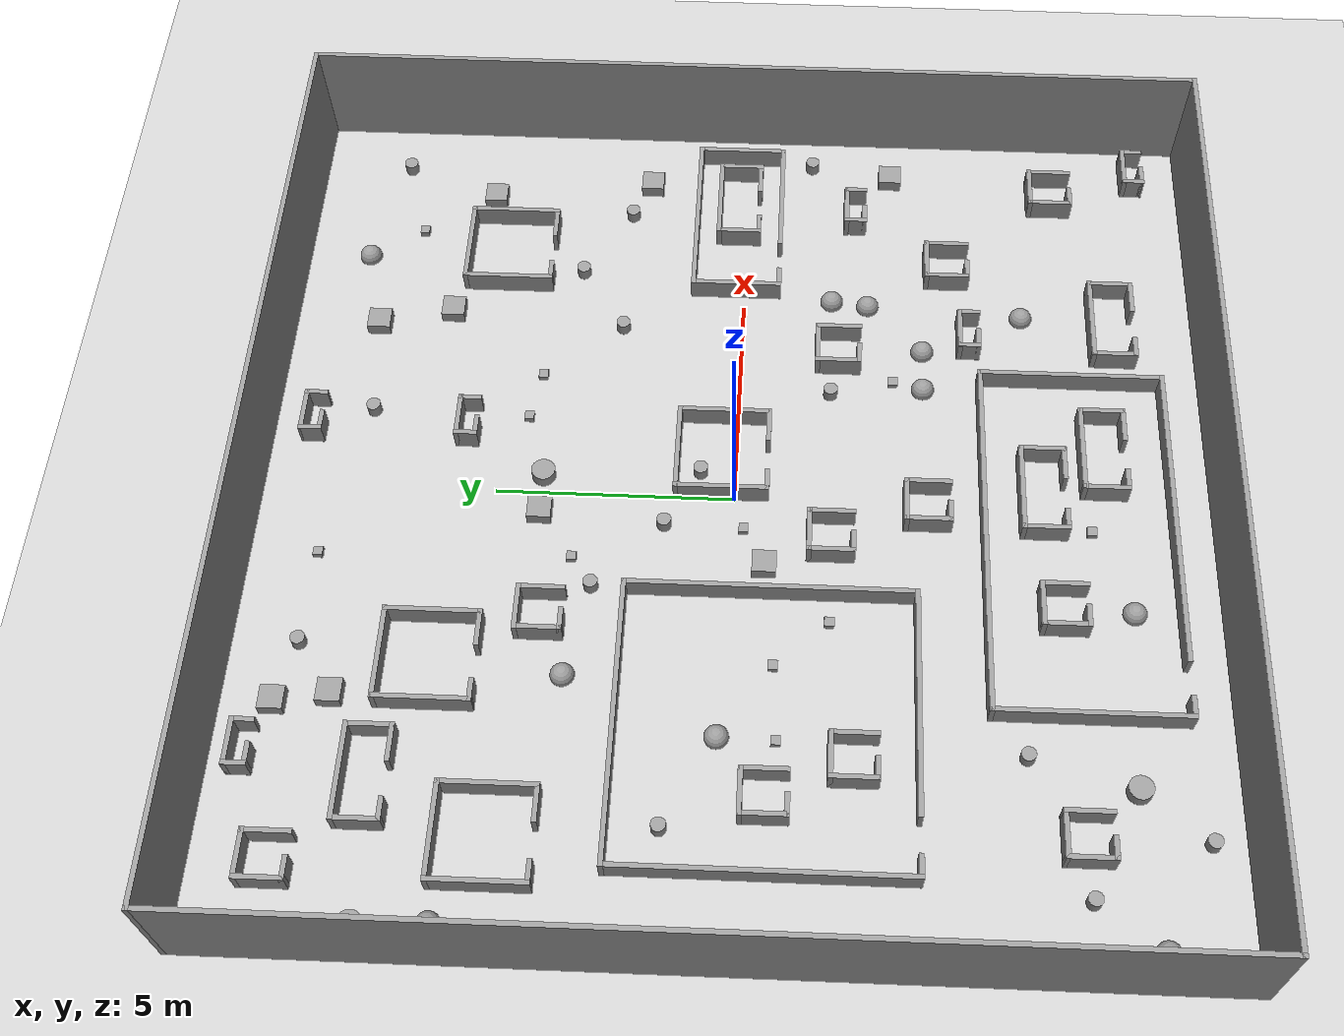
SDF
<sdf version="1.6">
  <world name="default">
    <light name="sun" type="directional">
      <cast_shadows>1</cast_shadows>
      <pose frame="">0 0 10 0 -0 0</pose>
      <diffuse>0.8 0.8 0.8 1</diffuse>
      <specular>0.2 0.2 0.2 1</specular>
      <attenuation>
        <range>1000</range>
        <constant>0.9</constant>
        <linear>0.01</linear>
        <quadratic>0.001</quadratic>
      </attenuation>
      <direction>-0.5 0.1 -0.9</direction>
    </light>
    <model name="ground_plane">
      <static>1</static>
      <link name="link">
        <collision name="collision">
          <geometry>
            <plane>
              <normal>0 0 1</normal>
              <size>20 20</size>
            </plane>
          </geometry>
          <surface>
            <contact>
              <collide_bitmask>65535</collide_bitmask>
              <ode />
            </contact>
            <friction>
              <ode>
                <mu>100</mu>
                <mu2>50</mu2>
              </ode>
              <torsional>
                <ode />
              </torsional>
            </friction>
            <bounce />
          </surface>
          <max_contacts>10</max_contacts>
        </collision>
        <visual name="visual">
          <cast_shadows>0</cast_shadows>
          <geometry>
            <plane>
              <normal>0 0 1</normal>
              <size>20 20</size>
            </plane>
          </geometry>
          <material>
            <script>
              <uri>file://media/materials/scripts/gazebo.material</uri>
              <name>Gazebo/Grey</name>
            </script>
          </material>
        </visual>
        <self_collide>0</self_collide>
        <enable_wind>0</enable_wind>
        <kinematic>0</kinematic>
      </link>
    </model>
     <model name="outsidewall.sdf">
    <pose frame="">0 0 0 0 -0 0</pose>
    <link name="Wall_3">
      <collision name="Wall_3_Collision">
        <geometry>
          <box>
            <size>20 0.10 2.5</size>
          </box>
        </geometry>
        <pose frame="">0 0 1.25 0 -0 0</pose>
      </collision>
      <visual name="Wall_3_Visual">
        <pose frame="">0 0 1.25 0 -0 0</pose>
        <geometry>
          <box>
            <size>20 0.10 2.5</size>
          </box>
        </geometry>
        <material>
          <script>
            <uri>file://media/materials/scripts/gazebo.material</uri>
            <name>Gazebo/Grey</name>
          </script>
          <ambient>1 1 1 1</ambient>
        </material>
        <meta>
          <layer>0</layer>
        </meta>
      </visual>
      <pose frame="">0 9.95 0 0 -0 0</pose>
    </link>
    <link name="Wall_5">
      <collision name="Wall_5_Collision">
        <geometry>
          <box>
            <size>20 0.10 2.5</size>
          </box>
        </geometry>
        <pose frame="">0 0 1.25 0 -0 0</pose>
      </collision>
      <visual name="Wall_5_Visual">
        <pose frame="">0 0 1.25 0 -0 0</pose>
        <geometry>
          <box>
            <size>20 0.10 2.5</size>
          </box>
        </geometry>
        <material>
          <script>
            <uri>file://media/materials/scripts/gazebo.material</uri>
            <name>Gazebo/Grey</name>
          </script>
          <ambient>1 1 1 1</ambient>
        </material>
        <meta>
          <layer>0</layer>
        </meta>
      </visual>
      <pose frame="">-9.95 0 0 0 -0 1.5707</pose>
    </link>
    <link name="Wall_6">
      <collision name="Wall_6_Collision">
        <geometry>
          <box>
            <size>20 0.10 2.5</size>
          </box>
        </geometry>
        <pose frame="">0 0 1.25 0 -0 0</pose>
      </collision>
      <visual name="Wall_6_Visual">
        <pose frame="">0 0 1.25 0 -0 0</pose>
        <geometry>
          <box>
            <size>20 0.10 2.5</size>
          </box>
        </geometry>
        <material>
          <script>
            <uri>file://media/materials/scripts/gazebo.material</uri>
            <name>Gazebo/Grey</name>
          </script>
          <ambient>1 1 1 1</ambient>
        </material>
        <meta>
          <layer>0</layer>
        </meta>
      </visual>
      <pose frame="">0 -9.95 0 0 -0 0</pose>
    </link>
    <link name="Wall_7">
      <collision name="Wall_7_Collision">
        <geometry>
          <box>
            <size>20 0.10 2.5</size>
          </box>
        </geometry>
        <pose frame="">0 0 1.25 0 -0 0</pose>
      </collision>
      <visual name="Wall_7_Visual">
        <pose frame="">0 0 1.25 0 -0 0</pose>
        <geometry>
          <box>
            <size>20 0.10 2.5</size>
          </box>
        </geometry>
        <material>
          <script>
            <uri>file://media/materials/scripts/gazebo.material</uri>
            <name>Gazebo/Grey</name>
          </script>
          <ambient>1 1 1 1</ambient>
        </material>
        <meta>
          <layer>0</layer>
        </meta>
      </visual>
      <pose frame="">9.95 0 0 0 -0 1.5707</pose>
    </link>
    <static>1</static>
  </model>
    <gravity>0 0 -9.8</gravity>
    <magnetic_field>6e-06 2.3e-05 -4.2e-05</magnetic_field>
    <atmosphere type="adiabatic" />
    <physics default="0" name="default_physics" type="ode">
      <max_step_size>0.001</max_step_size>
      <real_time_factor>1</real_time_factor>
      <real_time_update_rate>1000</real_time_update_rate>
    </physics>
    <scene>
      <ambient>0.4 0.4 0.4 1</ambient>
      <background>0.7 0.7 0.7 1</background>
      <shadows>1</shadows>
    </scene>
    <audio>
      <device>default</device>
    </audio>
    <wind />
    <spherical_coordinates>
      <surface_model>EARTH_WGS84</surface_model>
      <latitude_deg>0</latitude_deg>
      <longitude_deg>0</longitude_deg>
      <elevation>0</elevation>
      <heading_deg>0</heading_deg>
    </spherical_coordinates>
    <gui fullscreen="0">
      <camera name="user_camera">
        <pose frame="">17.6964 -3.39131 8.77294 0 0.343643 2.9522</pose>
        <view_controller>orbit</view_controller>
        <projection_type>perspective</projection_type>
      </camera>
    </gui>

  <model name="shape2">
    <pose frame="">7.3 0.2 0 0 -0 0</pose>
    <link name="Wall_0">
      <collision name="Wall_0_Collision">
        <geometry>
          <box>
            <size>3.98685 0.1 0.5</size>
          </box>
        </geometry>
        <pose frame="">0 0 0.25 0 -0 0</pose>
      </collision>
      <visual name="Wall_0_Visual">
        <pose frame="">0 0 0.25 0 -0 0</pose>
        <geometry>
          <box>
            <size>3.98685 0.1 0.5</size>
          </box>
        </geometry>
        <material>
          <script>
            <uri>file://media/materials/scripts/gazebo.material</uri>
            <name>Gazebo/Grey</name>
          </script>
          <ambient>1 1 1 1</ambient>
        </material>
        <meta>
          <layer>0</layer>
        </meta>
      </visual>
      <pose frame="">0.003288 0.95 0 0 -0 0</pose>
    </link>
    <link name="Wall_1">
      <collision name="Wall_1_Collision">
        <geometry>
          <box>
            <size>2 0.1 0.5</size>
          </box>
        </geometry>
        <pose frame="">0 0 0.25 0 -0 0</pose>
      </collision>
      <visual name="Wall_1_Visual">
        <pose frame="">0 0 0.25 0 -0 0</pose>
        <geometry>
          <box>
            <size>2 0.1 0.5</size>
          </box>
        </geometry>
        <material>
          <script>
            <uri>file://media/materials/scripts/gazebo.material</uri>
            <name>Gazebo/Grey</name>
          </script>
          <ambient>1 1 1 1</ambient>
        </material>
        <meta>
          <layer>0</layer>
        </meta>
      </visual>
      <pose frame="">1.94671 0 0 0 -0 -1.5708</pose>
    </link>
    <link name="Wall_2">
      <collision name="Wall_2_Collision">
        <geometry>
          <box>
            <size>2.8 0.1 0.5</size>
          </box>
        </geometry>
        <pose frame="">0 0 0.25 0 -0 0</pose>
      </collision>
      <visual name="Wall_2_Visual">
        <pose frame="">0 0 0.25 0 -0 0</pose>
        <geometry>
          <box>
            <size>2.8 0.1 0.5</size>
          </box>
        </geometry>
        <material>
          <script>
            <uri>file://media/materials/scripts/gazebo.material</uri>
            <name>Gazebo/Grey</name>
          </script>
          <ambient>1 1 1 1</ambient>
        </material>
        <meta>
          <layer>0</layer>
        </meta>
      </visual>
      <pose frame="">0.596712 -0.95 0 0 -0 3.14159</pose>
    </link>
    <link name="Wall_4">
      <collision name="Wall_4_Collision">
        <geometry>
          <box>
            <size>2 0.1 0.5</size>
          </box>
        </geometry>
        <pose frame="">0 0 0.25 0 -0 0</pose>
      </collision>
      <visual name="Wall_4_Visual">
        <pose frame="">0 0 0.25 0 -0 0</pose>
        <geometry>
          <box>
            <size>2 0.1 0.5</size>
          </box>
        </geometry>
        <material>
          <script>
            <uri>file://media/materials/scripts/gazebo.material</uri>
            <name>Gazebo/Grey</name>
          </script>
          <ambient>1 1 1 1</ambient>
        </material>
        <meta>
          <layer>0</layer>
        </meta>
      </visual>
      <pose frame="">-1.94671 0 0 0 -0 -1.5708</pose>
    </link>
    <link name="Wall_5">
      <collision name="Wall_5_Collision">
        <geometry>
          <box>
            <size>0.5 0.1 0.5</size>
          </box>
        </geometry>
        <pose frame="">0 0 0.25 0 -0 0</pose>
      </collision>
      <visual name="Wall_5_Visual">
        <pose frame="">0 0 0.25 0 -0 0</pose>
        <geometry>
          <box>
            <size>0.5 0.1 0.5</size>
          </box>
        </geometry>
        <material>
          <script>
            <uri>file://media/materials/scripts/gazebo.material</uri>
            <name>Gazebo/Grey</name>
          </script>
          <ambient>1 1 1 1</ambient>
        </material>
        <meta>
          <layer>0</layer>
        </meta>
      </visual>
      <pose frame="">-1.74671 -0.95 0 0 -0 0</pose>
    </link>
    <static>1</static>
  </model>
<model name="shape3">
    <pose frame="">-0.8 -7.1 0 0 -0 0</pose>
    <link name="Wall_11">
      <collision name="Wall_11_Collision">
        <geometry>
          <box>
            <size>4 0.1 0.5</size>
          </box>
        </geometry>
        <pose frame="">0 0 0.25 0 -0 0</pose>
      </collision>
      <visual name="Wall_11_Visual">
        <pose frame="">0 0 0.25 0 -0 0</pose>
        <geometry>
          <box>
            <size>4 0.1 0.5</size>
          </box>
        </geometry>
        <material>
          <script>
            <uri>file://media/materials/scripts/gazebo.material</uri>
            <name>Gazebo/Grey</name>
          </script>
          <ambient>1 1 1 1</ambient>
        </material>
        <meta>
          <layer>0</layer>
        </meta>
      </visual>
      <pose frame="">-3.95 0 0 0 -0 -1.5708</pose>
    </link>
    <link name="Wall_12">
      <collision name="Wall_12_Collision">
        <geometry>
          <box>
            <size>0.5 0.1 0.5</size>
          </box>
        </geometry>
        <pose frame="">0 0 0.25 0 -0 0</pose>
      </collision>
      <visual name="Wall_12_Visual">
        <pose frame="">0 0 0.25 0 -0 0</pose>
        <geometry>
          <box>
            <size>0.5 0.1 0.5</size>
          </box>
        </geometry>
        <material>
          <script>
            <uri>file://media/materials/scripts/gazebo.material</uri>
            <name>Gazebo/Grey</name>
          </script>
          <ambient>1 1 1 1</ambient>
        </material>
        <meta>
          <layer>0</layer>
        </meta>
      </visual>
      <pose frame="">-3.75 -1.95 0 0 -0 0</pose>
    </link>
    <link name="Wall_7">
      <collision name="Wall_7_Collision">
        <geometry>
          <box>
            <size>8 0.1 0.5</size>
          </box>
        </geometry>
        <pose frame="">0 0 0.25 0 -0 0</pose>
      </collision>
      <visual name="Wall_7_Visual">
        <pose frame="">0 0 0.25 0 -0 0</pose>
        <geometry>
          <box>
            <size>8 0.1 0.5</size>
          </box>
        </geometry>
        <material>
          <script>
            <uri>file://media/materials/scripts/gazebo.material</uri>
            <name>Gazebo/Grey</name>
          </script>
          <ambient>1 1 1 1</ambient>
        </material>
        <meta>
          <layer>0</layer>
        </meta>
      </visual>
      <pose frame="">-0 1.95 0 0 -0 0</pose>
    </link>
    <link name="Wall_8">
      <collision name="Wall_8_Collision">
        <geometry>
          <box>
            <size>4 0.1 0.5</size>
          </box>
        </geometry>
        <pose frame="">0 0 0.25 0 -0 0</pose>
      </collision>
      <visual name="Wall_8_Visual">
        <pose frame="">0 0 0.25 0 -0 0</pose>
        <geometry>
          <box>
            <size>4 0.1 0.5</size>
          </box>
        </geometry>
        <material>
          <script>
            <uri>file://media/materials/scripts/gazebo.material</uri>
            <name>Gazebo/Grey</name>
          </script>
          <ambient>1 1 1 1</ambient>
        </material>
        <meta>
          <layer>0</layer>
        </meta>
      </visual>
      <pose frame="">3.95 0 0 0 -0 -1.5708</pose>
    </link>
    <link name="Wall_9">
      <collision name="Wall_9_Collision">
        <geometry>
          <box>
            <size>6.8 0.1 0.5</size>
          </box>
        </geometry>
        <pose frame="">0 0 0.25 0 -0 0</pose>
      </collision>
      <visual name="Wall_9_Visual">
        <pose frame="">0 0 0.25 0 -0 0</pose>
        <geometry>
          <box>
            <size>6.8 0.1 0.5</size>
          </box>
        </geometry>
        <material>
          <script>
            <uri>file://media/materials/scripts/gazebo.material</uri>
            <name>Gazebo/Grey</name>
          </script>
          <ambient>1 1 1 1</ambient>
        </material>
        <meta>
          <layer>0</layer>
        </meta>
      </visual>
      <pose frame="">0.6 -1.95 0 0 -0 3.14159</pose>
    </link>
    <static>1</static>
  </model>
<model name="cylinder_d=30">
    <link name="link_0">
      <inertial>
        <mass>1</mass>
        <inertia>
          <ixx>0.145833</ixx>
          <ixy>0</ixy>
          <ixz>0</ixz>
          <iyy>0.145833</iyy>
          <iyz>0</iyz>
          <izz>0.125</izz>
        </inertia>
        <pose frame="">0 0 0 0 -0 0</pose>
      </inertial>
      <pose frame="">9.15 -1.45 0 0 -0 0</pose>
      <gravity>1</gravity>
      <self_collide>0</self_collide>
      <kinematic>0</kinematic>
      <enable_wind>0</enable_wind>
      <visual name="visual">
        <pose frame="">0 0 0 0 -0 0</pose>
        <geometry>
          <cylinder>
            <radius>0.15</radius>
            <length>0.5</length>
          </cylinder>
        </geometry>
        <material>
          <lighting>1</lighting>
          <script>
            <uri>file://media/materials/scripts/gazebo.material</uri>
            <name>Gazebo/Grey</name>
          </script>
          <shader type="vertex">
            <normal_map>__default__</normal_map>
          </shader>
          <ambient>0.3 0.3 0.3 1</ambient>
          <diffuse>0.7 0.7 0.7 1</diffuse>
          <specular>0.01 0.01 0.01 1</specular>
          <emissive>0 0 0 1</emissive>
        </material>
        <transparency>0</transparency>
        <cast_shadows>1</cast_shadows>
      </visual>
      <collision name="collision">
        <laser_retro>0</laser_retro>
        <max_contacts>10</max_contacts>
        <pose frame="">0 0 0 0 -0 0</pose>
        <geometry>
          <cylinder>
            <radius>0.15</radius>
            <length>0.5</length>
          </cylinder>
        </geometry>
        <surface>
          <friction>
            <ode>
              <mu>1</mu>
              <mu2>1</mu2>
              <fdir1>0 0 0</fdir1>
              <slip1>0</slip1>
              <slip2>0</slip2>
            </ode>
            <torsional>
              <coefficient>1</coefficient>
              <patch_radius>0</patch_radius>
              <surface_radius>0</surface_radius>
              <use_patch_radius>1</use_patch_radius>
              <ode>
                <slip>0</slip>
              </ode>
            </torsional>
          </friction>
          <bounce>
            <restitution_coefficient>0</restitution_coefficient>
            <threshold>1e+06</threshold>
          </bounce>
          <contact>
            <collide_without_contact>0</collide_without_contact>
            <collide_without_contact_bitmask>1</collide_without_contact_bitmask>
            <collide_bitmask>1</collide_bitmask>
            <ode>
              <soft_cfm>0</soft_cfm>
              <soft_erp>0.2</soft_erp>
              <kp>1e+13</kp>
              <kd>1</kd>
              <max_vel>0.01</max_vel>
              <min_depth>0</min_depth>
            </ode>
            <bullet>
              <split_impulse>1</split_impulse>
              <split_impulse_penetration_threshold>-0.01</split_impulse_penetration_threshold>
              <soft_cfm>0</soft_cfm>
              <soft_erp>0.2</soft_erp>
              <kp>1e+13</kp>
              <kd>1</kd>
            </bullet>
          </contact>
        </surface>
      </collision>
    </link>
    <static>0</static>
    <allow_auto_disable>1</allow_auto_disable>
  </model>
<model name="shape0">
    <pose frame="">4.3 -4.95 0 0 -0 0</pose>
    <link name="Wall_0">
      <pose frame="">0 0.2 0 0 -0 0</pose>
      <self_collide>0</self_collide>
      <enable_wind>0</enable_wind>
      <kinematic>0</kinematic>
      <gravity>1</gravity>
      <inertial>
        <mass>1</mass>
        <pose frame="">0 0 0 0 -0 0</pose>
        <inertia>
          <ixx>1</ixx>
          <ixy>0</ixy>
          <ixz>0</ixz>
          <iyy>1</iyy>
          <iyz>0</iyz>
          <izz>1</izz>
        </inertia>
      </inertial>
      <visual name="Wall_0_Visual">
        <pose frame="">0 0 0.25 0 -0 0</pose>
        <geometry>
          <box>
            <size>1 0.1 0.5</size>
          </box>
        </geometry>
        <material>
          <script>
            <uri>file://media/materials/scripts/gazebo.material</uri>
            <name>Gazebo/Grey</name>
          </script>
          <ambient>1 1 1 1</ambient>
          <shader type="vertex">
            <normal_map>__default__</normal_map>
          </shader>
          <diffuse>0.7 0.7 0.7 1</diffuse>
          <specular>0.01 0.01 0.01 1</specular>
          <emissive>0 0 0 1</emissive>
        </material>
        <meta>
          <layer>0</layer>
        </meta>
        <transparency>0</transparency>
        <cast_shadows>1</cast_shadows>
      </visual>
      <collision name="Wall_0_Collision">
        <laser_retro>0</laser_retro>
        <max_contacts>10</max_contacts>
        <pose frame="">0 0 0.25 0 -0 0</pose>
        <geometry>
          <box>
            <size>1 0.1 0.5</size>
          </box>
        </geometry>
        <surface>
          <friction>
            <ode>
              <mu>1</mu>
              <mu2>1</mu2>
              <fdir1>0 0 0</fdir1>
              <slip1>0</slip1>
              <slip2>0</slip2>
            </ode>
            <torsional>
              <coefficient>1</coefficient>
              <patch_radius>0</patch_radius>
              <surface_radius>0</surface_radius>
              <use_patch_radius>1</use_patch_radius>
              <ode>
                <slip>0</slip>
              </ode>
            </torsional>
          </friction>
          <bounce>
            <restitution_coefficient>0</restitution_coefficient>
            <threshold>1e+06</threshold>
          </bounce>
          <contact>
            <collide_without_contact>0</collide_without_contact>
            <collide_without_contact_bitmask>1</collide_without_contact_bitmask>
            <collide_bitmask>1</collide_bitmask>
            <ode>
              <soft_cfm>0</soft_cfm>
              <soft_erp>0.2</soft_erp>
              <kp>1e+13</kp>
              <kd>1</kd>
              <max_vel>0.01</max_vel>
              <min_depth>0</min_depth>
            </ode>
            <bullet>
              <split_impulse>1</split_impulse>
              <split_impulse_penetration_threshold>-0.01</split_impulse_penetration_threshold>
              <soft_cfm>0</soft_cfm>
              <soft_erp>0.2</soft_erp>
              <kp>1e+13</kp>
              <kd>1</kd>
            </bullet>
          </contact>
        </surface>
      </collision>
    </link>
    <link name="Wall_2">
      <pose frame="">-0.45 0 0.01 0 0 -1.5708</pose>
      <self_collide>0</self_collide>
      <enable_wind>0</enable_wind>
      <kinematic>0</kinematic>
      <gravity>1</gravity>
      <inertial>
        <mass>1</mass>
        <pose frame="">0 0 0 0 -0 0</pose>
        <inertia>
          <ixx>1</ixx>
          <ixy>0</ixy>
          <ixz>0</ixz>
          <iyy>1</iyy>
          <iyz>0</iyz>
          <izz>1</izz>
        </inertia>
      </inertial>
      <visual name="Wall_2_Visual">
        <pose frame="">0 0 0.25 0 -0 0</pose>
        <geometry>
          <box>
            <size>0.5 0.1 0.5</size>
          </box>
        </geometry>
        <material>
          <script>
            <uri>file://media/materials/scripts/gazebo.material</uri>
            <name>Gazebo/Grey</name>
          </script>
          <ambient>1 1 1 1</ambient>
          <shader type="vertex">
            <normal_map>__default__</normal_map>
          </shader>
          <diffuse>0.7 0.7 0.7 1</diffuse>
          <specular>0.01 0.01 0.01 1</specular>
          <emissive>0 0 0 1</emissive>
        </material>
        <meta>
          <layer>0</layer>
        </meta>
        <transparency>0</transparency>
        <cast_shadows>1</cast_shadows>
      </visual>
      <collision name="Wall_2_Collision">
        <laser_retro>0</laser_retro>
        <max_contacts>10</max_contacts>
        <pose frame="">0 0 0.25 0 -0 0</pose>
        <geometry>
          <box>
            <size>0.5 0.1 0.5</size>
          </box>
        </geometry>
        <surface>
          <friction>
            <ode>
              <mu>1</mu>
              <mu2>1</mu2>
              <fdir1>0 0 0</fdir1>
              <slip1>0</slip1>
              <slip2>0</slip2>
            </ode>
            <torsional>
              <coefficient>1</coefficient>
              <patch_radius>0</patch_radius>
              <surface_radius>0</surface_radius>
              <use_patch_radius>1</use_patch_radius>
              <ode>
                <slip>0</slip>
              </ode>
            </torsional>
          </friction>
          <bounce>
            <restitution_coefficient>0</restitution_coefficient>
            <threshold>1e+06</threshold>
          </bounce>
          <contact>
            <collide_without_contact>0</collide_without_contact>
            <collide_without_contact_bitmask>1</collide_without_contact_bitmask>
            <collide_bitmask>1</collide_bitmask>
            <ode>
              <soft_cfm>0</soft_cfm>
              <soft_erp>0.2</soft_erp>
              <kp>1e+13</kp>
              <kd>1</kd>
              <max_vel>0.01</max_vel>
              <min_depth>0</min_depth>
            </ode>
            <bullet>
              <split_impulse>1</split_impulse>
              <split_impulse_penetration_threshold>-0.01</split_impulse_penetration_threshold>
              <soft_cfm>0</soft_cfm>
              <soft_erp>0.2</soft_erp>
              <kp>1e+13</kp>
              <kd>1</kd>
            </bullet>
          </contact>
        </surface>
      </collision>
    </link>
    <link name="Wall_4">
      <pose frame="">0.45 0 0 0 0 -1.5708</pose>
      <self_collide>0</self_collide>
      <enable_wind>0</enable_wind>
      <kinematic>0</kinematic>
      <gravity>1</gravity>
      <inertial>
        <mass>1</mass>
        <pose frame="">0 0 0 0 -0 0</pose>
        <inertia>
          <ixx>1</ixx>
          <ixy>0</ixy>
          <ixz>0</ixz>
          <iyy>1</iyy>
          <iyz>0</iyz>
          <izz>1</izz>
        </inertia>
      </inertial>
      <visual name="Wall_4_Visual">
        <pose frame="">0 0 0.25 0 -0 0</pose>
        <geometry>
          <box>
            <size>0.5 0.1 0.5</size>
          </box>
        </geometry>
        <material>
          <script>
            <uri>file://media/materials/scripts/gazebo.material</uri>
            <name>Gazebo/Grey</name>
          </script>
          <ambient>1 1 1 1</ambient>
          <shader type="vertex">
            <normal_map>__default__</normal_map>
          </shader>
          <diffuse>0.7 0.7 0.7 1</diffuse>
          <specular>0.01 0.01 0.01 1</specular>
          <emissive>0 0 0 1</emissive>
        </material>
        <meta>
          <layer>0</layer>
        </meta>
        <transparency>0</transparency>
        <cast_shadows>1</cast_shadows>
      </visual>
      <collision name="Wall_4_Collision">
        <laser_retro>0</laser_retro>
        <max_contacts>10</max_contacts>
        <pose frame="">0 0 0.25 0 -0 0</pose>
        <geometry>
          <box>
            <size>0.5 0.1 0.5</size>
          </box>
        </geometry>
        <surface>
          <friction>
            <ode>
              <mu>1</mu>
              <mu2>1</mu2>
              <fdir1>0 0 0</fdir1>
              <slip1>0</slip1>
              <slip2>0</slip2>
            </ode>
            <torsional>
              <coefficient>1</coefficient>
              <patch_radius>0</patch_radius>
              <surface_radius>0</surface_radius>
              <use_patch_radius>1</use_patch_radius>
              <ode>
                <slip>0</slip>
              </ode>
            </torsional>
          </friction>
          <bounce>
            <restitution_coefficient>0</restitution_coefficient>
            <threshold>1e+06</threshold>
          </bounce>
          <contact>
            <collide_without_contact>0</collide_without_contact>
            <collide_without_contact_bitmask>1</collide_without_contact_bitmask>
            <collide_bitmask>1</collide_bitmask>
            <ode>
              <soft_cfm>0</soft_cfm>
              <soft_erp>0.2</soft_erp>
              <kp>1e+13</kp>
              <kd>1</kd>
              <max_vel>0.01</max_vel>
              <min_depth>0</min_depth>
            </ode>
            <bullet>
              <split_impulse>1</split_impulse>
              <split_impulse_penetration_threshold>-0.01</split_impulse_penetration_threshold>
              <soft_cfm>0</soft_cfm>
              <soft_erp>0.2</soft_erp>
              <kp>1e+13</kp>
              <kd>1</kd>
            </bullet>
          </contact>
        </surface>
      </collision>
    </link>
    <link name="Wall_7">
      <pose frame="">-0.25 -0.2 0 0 -0 0</pose>
      <self_collide>0</self_collide>
      <enable_wind>0</enable_wind>
      <kinematic>0</kinematic>
      <gravity>1</gravity>
      <inertial>
        <mass>1</mass>
        <pose frame="">0 0 0 0 -0 0</pose>
        <inertia>
          <ixx>1</ixx>
          <ixy>0</ixy>
          <ixz>0</ixz>
          <iyy>1</iyy>
          <iyz>0</iyz>
          <izz>1</izz>
        </inertia>
      </inertial>
      <visual name="Wall_7_Visual">
        <pose frame="">0 0 0.25 0 -0 0</pose>
        <geometry>
          <box>
            <size>0.5 0.1 0.5</size>
          </box>
        </geometry>
        <material>
          <script>
            <uri>file://media/materials/scripts/gazebo.material</uri>
            <name>Gazebo/Grey</name>
          </script>
          <ambient>1 1 1 1</ambient>
          <shader type="vertex">
            <normal_map>__default__</normal_map>
          </shader>
          <diffuse>0.7 0.7 0.7 1</diffuse>
          <specular>0.01 0.01 0.01 1</specular>
          <emissive>0 0 0 1</emissive>
        </material>
        <meta>
          <layer>0</layer>
        </meta>
        <transparency>0</transparency>
        <cast_shadows>1</cast_shadows>
      </visual>
      <collision name="Wall_7_Collision">
        <laser_retro>0</laser_retro>
        <max_contacts>10</max_contacts>
        <pose frame="">0 0 0.25 0 -0 0</pose>
        <geometry>
          <box>
            <size>0.5 0.1 0.5</size>
          </box>
        </geometry>
        <surface>
          <friction>
            <ode>
              <mu>1</mu>
              <mu2>1</mu2>
              <fdir1>0 0 0</fdir1>
              <slip1>0</slip1>
              <slip2>0</slip2>
            </ode>
            <torsional>
              <coefficient>1</coefficient>
              <patch_radius>0</patch_radius>
              <surface_radius>0</surface_radius>
              <use_patch_radius>1</use_patch_radius>
              <ode>
                <slip>0</slip>
              </ode>
            </torsional>
          </friction>
          <bounce>
            <restitution_coefficient>0</restitution_coefficient>
            <threshold>1e+06</threshold>
          </bounce>
          <contact>
            <collide_without_contact>0</collide_without_contact>
            <collide_without_contact_bitmask>1</collide_without_contact_bitmask>
            <collide_bitmask>1</collide_bitmask>
            <ode>
              <soft_cfm>0</soft_cfm>
              <soft_erp>0.2</soft_erp>
              <kp>1e+13</kp>
              <kd>1</kd>
              <max_vel>0.01</max_vel>
              <min_depth>0</min_depth>
            </ode>
            <bullet>
              <split_impulse>1</split_impulse>
              <split_impulse_penetration_threshold>-0.01</split_impulse_penetration_threshold>
              <soft_cfm>0</soft_cfm>
              <soft_erp>0.2</soft_erp>
              <kp>1e+13</kp>
              <kd>1</kd>
            </bullet>
          </contact>
        </surface>
      </collision>
    </link>
    <static>1</static>
    <allow_auto_disable>1</allow_auto_disable>
  </model>
<model name="box_d=50">
    <link name="link_2">
      <inertial>
        <mass>1</mass>
        <inertia>
          <ixx>0.166667</ixx>
          <ixy>0</ixy>
          <ixz>0</ixz>
          <iyy>0.166667</iyy>
          <iyz>0</iyz>
          <izz>0.166667</izz>
        </inertia>
        <pose frame="">0 0 0 0 -0 0</pose>
      </inertial>
      <pose frame="">-0.45 4.05 0 0 -0 0</pose>
      <gravity>1</gravity>
      <self_collide>0</self_collide>
      <kinematic>0</kinematic>
      <enable_wind>0</enable_wind>
      <visual name="visual">
        <pose frame="">0 0 0 0 -0 0</pose>
        <geometry>
          <box>
            <size>0.5 0.5 0.5</size>
          </box>
        </geometry>
        <material>
          <lighting>1</lighting>
          <script>
            <uri>file://media/materials/scripts/gazebo.material</uri>
            <name>Gazebo/Grey</name>
          </script>
          <shader type="vertex">
            <normal_map>__default__</normal_map>
          </shader>
          <ambient>0.3 0.3 0.3 1</ambient>
          <diffuse>0.7 0.7 0.7 1</diffuse>
          <specular>0.01 0.01 0.01 1</specular>
          <emissive>0 0 0 1</emissive>
        </material>
        <transparency>0</transparency>
        <cast_shadows>1</cast_shadows>
      </visual>
      <collision name="collision">
        <laser_retro>0</laser_retro>
        <max_contacts>10</max_contacts>
        <pose frame="">0 0 0 0 -0 0</pose>
        <geometry>
          <box>
            <size>0.5 0.5 0.5</size>
          </box>
        </geometry>
        <surface>
          <friction>
            <ode>
              <mu>1</mu>
              <mu2>1</mu2>
              <fdir1>0 0 0</fdir1>
              <slip1>0</slip1>
              <slip2>0</slip2>
            </ode>
            <torsional>
              <coefficient>1</coefficient>
              <patch_radius>0</patch_radius>
              <surface_radius>0</surface_radius>
              <use_patch_radius>1</use_patch_radius>
              <ode>
                <slip>0</slip>
              </ode>
            </torsional>
          </friction>
          <bounce>
            <restitution_coefficient>0</restitution_coefficient>
            <threshold>1e+06</threshold>
          </bounce>
          <contact>
            <collide_without_contact>0</collide_without_contact>
            <collide_without_contact_bitmask>1</collide_without_contact_bitmask>
            <collide_bitmask>1</collide_bitmask>
            <ode>
              <soft_cfm>0</soft_cfm>
              <soft_erp>0.2</soft_erp>
              <kp>1e+13</kp>
              <kd>1</kd>
              <max_vel>0.01</max_vel>
              <min_depth>0</min_depth>
            </ode>
            <bullet>
              <split_impulse>1</split_impulse>
              <split_impulse_penetration_threshold>-0.01</split_impulse_penetration_threshold>
              <soft_cfm>0</soft_cfm>
              <soft_erp>0.2</soft_erp>
              <kp>1e+13</kp>
              <kd>1</kd>
            </bullet>
          </contact>
        </surface>
      </collision>
    </link>
    <static>0</static>
    <allow_auto_disable>1</allow_auto_disable>
  </model>
<model name="shape7">
    <pose frame="">-5.2 -0.8 0 0 -0 0</pose>
    <link name="Wall_34">
      <collision name="Wall_34_Collision">
        <geometry>
          <box>
            <size>6 0.1 0.5</size>
          </box>
        </geometry>
        <pose frame="">0 0 0.25 0 -0 0</pose>
      </collision>
      <visual name="Wall_34_Visual">
        <pose frame="">0 0 0.25 0 -0 0</pose>
        <geometry>
          <box>
            <size>6 0.1 0.5</size>
          </box>
        </geometry>
        <material>
          <script>
            <uri>file://media/materials/scripts/gazebo.material</uri>
            <name>Gazebo/Grey</name>
          </script>
          <ambient>1 1 1 1</ambient>
        </material>
        <meta>
          <layer>0</layer>
        </meta>
      </visual>
      <pose frame="">0 2.95 0 0 -0 0</pose>
    </link>
    <link name="Wall_35">
      <collision name="Wall_35_Collision">
        <geometry>
          <box>
            <size>6 0.1 0.5</size>
          </box>
        </geometry>
        <pose frame="">0 0 0.25 0 -0 0</pose>
      </collision>
      <visual name="Wall_35_Visual">
        <pose frame="">0 0 0.25 0 -0 0</pose>
        <geometry>
          <box>
            <size>6 0.1 0.5</size>
          </box>
        </geometry>
        <material>
          <script>
            <uri>file://media/materials/scripts/gazebo.material</uri>
            <name>Gazebo/Grey</name>
          </script>
          <ambient>1 1 1 1</ambient>
        </material>
        <meta>
          <layer>0</layer>
        </meta>
      </visual>
      <pose frame="">2.95 0 0 0 -0 -1.5708</pose>
    </link>
    <link name="Wall_36">
      <collision name="Wall_36_Collision">
        <geometry>
          <box>
            <size>4.8 0.1 0.5</size>
          </box>
        </geometry>
        <pose frame="">0 0 0.25 0 -0 0</pose>
      </collision>
      <visual name="Wall_36_Visual">
        <pose frame="">0 0 0.25 0 -0 0</pose>
        <geometry>
          <box>
            <size>4.8 0.1 0.5</size>
          </box>
        </geometry>
        <material>
          <script>
            <uri>file://media/materials/scripts/gazebo.material</uri>
            <name>Gazebo/Grey</name>
          </script>
          <ambient>1 1 1 1</ambient>
        </material>
        <meta>
          <layer>0</layer>
        </meta>
      </visual>
      <pose frame="">0.6 -2.95 0 0 -0 3.14159</pose>
    </link>
    <link name="Wall_38">
      <collision name="Wall_38_Collision">
        <geometry>
          <box>
            <size>6 0.1 0.5</size>
          </box>
        </geometry>
        <pose frame="">0 0 0.25 0 -0 0</pose>
      </collision>
      <visual name="Wall_38_Visual">
        <pose frame="">0 0 0.25 0 -0 0</pose>
        <geometry>
          <box>
            <size>6 0.1 0.5</size>
          </box>
        </geometry>
        <material>
          <script>
            <uri>file://media/materials/scripts/gazebo.material</uri>
            <name>Gazebo/Grey</name>
          </script>
          <ambient>1 1 1 1</ambient>
        </material>
        <meta>
          <layer>0</layer>
        </meta>
      </visual>
      <pose frame="">-2.95 0 0 0 -0 -1.5708</pose>
    </link>
    <link name="Wall_39">
      <collision name="Wall_39_Collision">
        <geometry>
          <box>
            <size>0.5 0.1 0.5</size>
          </box>
        </geometry>
        <pose frame="">0 0 0.25 0 -0 0</pose>
      </collision>
      <visual name="Wall_39_Visual">
        <pose frame="">0 0 0.25 0 -0 0</pose>
        <geometry>
          <box>
            <size>0.5 0.1 0.5</size>
          </box>
        </geometry>
        <material>
          <script>
            <uri>file://media/materials/scripts/gazebo.material</uri>
            <name>Gazebo/Grey</name>
          </script>
          <ambient>1 1 1 1</ambient>
        </material>
        <meta>
          <layer>0</layer>
        </meta>
      </visual>
      <pose frame="">-2.75 -2.95 0 0 -0 0</pose>
    </link>
    <static>1</static>
  </model>
<model name="shape1">
    <pose frame="">7.8 0.2 0 0 -0 0</pose>
    <link name="Wall_0">
      <collision name="Wall_0_Collision">
        <geometry>
          <box>
            <size>2 0.1 0.5</size>
          </box>
        </geometry>
        <pose frame="">0 0 0.25 0 -0 0</pose>
      </collision>
      <visual name="Wall_0_Visual">
        <pose frame="">0 0 0.25 0 -0 0</pose>
        <geometry>
          <box>
            <size>2 0.1 0.5</size>
          </box>
        </geometry>
        <material>
          <script>
            <uri>file://media/materials/scripts/gazebo.material</uri>
            <name>Gazebo/Grey</name>
          </script>
          <ambient>1 1 1 1</ambient>
        </material>
        <meta>
          <layer>0</layer>
        </meta>
      </visual>
      <pose frame="">0 0.45 0 0 -0 0</pose>
    </link>
    <link name="Wall_1">
      <collision name="Wall_1_Collision">
        <geometry>
          <box>
            <size>1 0.1 0.5</size>
          </box>
        </geometry>
        <pose frame="">0 0 0.25 0 -0 0</pose>
      </collision>
      <visual name="Wall_1_Visual">
        <pose frame="">0 0 0.25 0 -0 0</pose>
        <geometry>
          <box>
            <size>1 0.1 0.5</size>
          </box>
        </geometry>
        <material>
          <script>
            <uri>file://media/materials/scripts/gazebo.material</uri>
            <name>Gazebo/Grey</name>
          </script>
          <ambient>1 1 1 1</ambient>
        </material>
        <meta>
          <layer>0</layer>
        </meta>
      </visual>
      <pose frame="">0.95 -0 0 0 -0 -1.5708</pose>
    </link>
    <link name="Wall_2">
      <collision name="Wall_2_Collision">
        <geometry>
          <box>
            <size>0.8 0.1 0.5</size>
          </box>
        </geometry>
        <pose frame="">0 0 0.25 0 -0 0</pose>
      </collision>
      <visual name="Wall_2_Visual">
        <pose frame="">0 0 0.25 0 -0 0</pose>
        <geometry>
          <box>
            <size>0.8 0.1 0.5</size>
          </box>
        </geometry>
        <material>
          <script>
            <uri>file://media/materials/scripts/gazebo.material</uri>
            <name>Gazebo/Grey</name>
          </script>
          <ambient>1 1 1 1</ambient>
        </material>
        <meta>
          <layer>0</layer>
        </meta>
      </visual>
      <pose frame="">0.6 -0.45 0 0 -0 3.14159</pose>
    </link>
    <link name="Wall_4">
      <collision name="Wall_4_Collision">
        <geometry>
          <box>
            <size>1 0.1 0.5</size>
          </box>
        </geometry>
        <pose frame="">0 0 0.25 0 -0 0</pose>
      </collision>
      <visual name="Wall_4_Visual">
        <pose frame="">0 0 0.25 0 -0 0</pose>
        <geometry>
          <box>
            <size>1 0.1 0.5</size>
          </box>
        </geometry>
        <material>
          <script>
            <uri>file://media/materials/scripts/gazebo.material</uri>
            <name>Gazebo/Grey</name>
          </script>
          <ambient>1 1 1 1</ambient>
        </material>
        <meta>
          <layer>0</layer>
        </meta>
      </visual>
      <pose frame="">-0.95 -0 0 0 -0 -1.5708</pose>
    </link>
    <link name="Wall_5">
      <collision name="Wall_5_Collision">
        <geometry>
          <box>
            <size>0.499474 0.1 0.5</size>
          </box>
        </geometry>
        <pose frame="">0 0 0.25 0 -0 0</pose>
      </collision>
      <visual name="Wall_5_Visual">
        <pose frame="">0 0 0.25 0 -0 0</pose>
        <geometry>
          <box>
            <size>0.499474 0.1 0.5</size>
          </box>
        </geometry>
        <material>
          <script>
            <uri>file://media/materials/scripts/gazebo.material</uri>
            <name>Gazebo/Grey</name>
          </script>
          <ambient>1 1 1 1</ambient>
        </material>
        <meta>
          <layer>0</layer>
        </meta>
      </visual>
      <pose frame="">-0.75 -0.45 0 0 -0 0</pose>
    </link>
    <static>1</static>
  </model>
<model name="box_d=20">
    <link name="link_2">
      <inertial>
        <mass>1</mass>
        <inertia>
          <ixx>0.166667</ixx>
          <ixy>0</ixy>
          <ixz>0</ixz>
          <iyy>0.166667</iyy>
          <iyz>0</iyz>
          <izz>0.166667</izz>
        </inertia>
        <pose frame="">0 0 0 0 -0 0</pose>
      </inertial>
      <pose frame="">3 4.3 0 0 -0 0</pose>
      <gravity>1</gravity>
      <self_collide>0</self_collide>
      <kinematic>0</kinematic>
      <enable_wind>0</enable_wind>
      <visual name="visual">
        <pose frame="">0 0 0 0 -0 0</pose>
        <geometry>
          <box>
            <size>0.2 0.2 0.2</size>
          </box>
        </geometry>
        <material>
          <lighting>1</lighting>
          <script>
            <uri>file://media/materials/scripts/gazebo.material</uri>
            <name>Gazebo/Grey</name>
          </script>
          <shader type="vertex">
            <normal_map>__default__</normal_map>
          </shader>
          <ambient>0.3 0.3 0.3 1</ambient>
          <diffuse>0.7 0.7 0.7 1</diffuse>
          <specular>0.01 0.01 0.01 1</specular>
          <emissive>0 0 0 1</emissive>
        </material>
        <transparency>0</transparency>
        <cast_shadows>1</cast_shadows>
      </visual>
      <collision name="collision">
        <laser_retro>0</laser_retro>
        <max_contacts>10</max_contacts>
        <pose frame="">0 0 0 0 -0 0</pose>
        <geometry>
          <box>
            <size>0.2 0.2 0.2</size>
          </box>
        </geometry>
        <surface>
          <friction>
            <ode>
              <mu>1</mu>
              <mu2>1</mu2>
              <fdir1>0 0 0</fdir1>
              <slip1>0</slip1>
              <slip2>0</slip2>
            </ode>
            <torsional>
              <coefficient>1</coefficient>
              <patch_radius>0</patch_radius>
              <surface_radius>0</surface_radius>
              <use_patch_radius>1</use_patch_radius>
              <ode>
                <slip>0</slip>
              </ode>
            </torsional>
          </friction>
          <bounce>
            <restitution_coefficient>0</restitution_coefficient>
            <threshold>1e+06</threshold>
          </bounce>
          <contact>
            <collide_without_contact>0</collide_without_contact>
            <collide_without_contact_bitmask>1</collide_without_contact_bitmask>
            <collide_bitmask>1</collide_bitmask>
            <ode>
              <soft_cfm>0</soft_cfm>
              <soft_erp>0.2</soft_erp>
              <kp>1e+13</kp>
              <kd>1</kd>
              <max_vel>0.01</max_vel>
              <min_depth>0</min_depth>
            </ode>
            <bullet>
              <split_impulse>1</split_impulse>
              <split_impulse_penetration_threshold>-0.01</split_impulse_penetration_threshold>
              <soft_cfm>0</soft_cfm>
              <soft_erp>0.2</soft_erp>
              <kp>1e+13</kp>
              <kd>1</kd>
            </bullet>
          </contact>
        </surface>
      </collision>
    </link>
    <static>0</static>
    <allow_auto_disable>1</allow_auto_disable>
  </model>
<model name="box_d=50">
    <link name="link_2">
      <inertial>
        <mass>1</mass>
        <inertia>
          <ixx>0.166667</ixx>
          <ixy>0</ixy>
          <ixz>0</ixz>
          <iyy>0.166667</iyy>
          <iyz>0</iyz>
          <izz>0.166667</izz>
        </inertia>
        <pose frame="">0 0 0 0 -0 0</pose>
      </inertial>
      <pose frame="">7.95 5.85 0 0 -0 0</pose>
      <gravity>1</gravity>
      <self_collide>0</self_collide>
      <kinematic>0</kinematic>
      <enable_wind>0</enable_wind>
      <visual name="visual">
        <pose frame="">0 0 0 0 -0 0</pose>
        <geometry>
          <box>
            <size>0.5 0.5 0.5</size>
          </box>
        </geometry>
        <material>
          <lighting>1</lighting>
          <script>
            <uri>file://media/materials/scripts/gazebo.material</uri>
            <name>Gazebo/Grey</name>
          </script>
          <shader type="vertex">
            <normal_map>__default__</normal_map>
          </shader>
          <ambient>0.3 0.3 0.3 1</ambient>
          <diffuse>0.7 0.7 0.7 1</diffuse>
          <specular>0.01 0.01 0.01 1</specular>
          <emissive>0 0 0 1</emissive>
        </material>
        <transparency>0</transparency>
        <cast_shadows>1</cast_shadows>
      </visual>
      <collision name="collision">
        <laser_retro>0</laser_retro>
        <max_contacts>10</max_contacts>
        <pose frame="">0 0 0 0 -0 0</pose>
        <geometry>
          <box>
            <size>0.5 0.5 0.5</size>
          </box>
        </geometry>
        <surface>
          <friction>
            <ode>
              <mu>1</mu>
              <mu2>1</mu2>
              <fdir1>0 0 0</fdir1>
              <slip1>0</slip1>
              <slip2>0</slip2>
            </ode>
            <torsional>
              <coefficient>1</coefficient>
              <patch_radius>0</patch_radius>
              <surface_radius>0</surface_radius>
              <use_patch_radius>1</use_patch_radius>
              <ode>
                <slip>0</slip>
              </ode>
            </torsional>
          </friction>
          <bounce>
            <restitution_coefficient>0</restitution_coefficient>
            <threshold>1e+06</threshold>
          </bounce>
          <contact>
            <collide_without_contact>0</collide_without_contact>
            <collide_without_contact_bitmask>1</collide_without_contact_bitmask>
            <collide_bitmask>1</collide_bitmask>
            <ode>
              <soft_cfm>0</soft_cfm>
              <soft_erp>0.2</soft_erp>
              <kp>1e+13</kp>
              <kd>1</kd>
              <max_vel>0.01</max_vel>
              <min_depth>0</min_depth>
            </ode>
            <bullet>
              <split_impulse>1</split_impulse>
              <split_impulse_penetration_threshold>-0.01</split_impulse_penetration_threshold>
              <soft_cfm>0</soft_cfm>
              <soft_erp>0.2</soft_erp>
              <kp>1e+13</kp>
              <kd>1</kd>
            </bullet>
          </contact>
        </surface>
      </collision>
    </link>
    <static>0</static>
    <allow_auto_disable>1</allow_auto_disable>
  </model>
<model name="shape5">
    <pose frame="">-7.6 4.4 0 0 -0 0</pose>
    <link name="Wall_20">
      <collision name="Wall_20_Collision">
        <geometry>
          <box>
            <size>2 0.1 0.5</size>
          </box>
        </geometry>
        <pose frame="">0 0 0.25 0 -0 0</pose>
      </collision>
      <visual name="Wall_20_Visual">
        <pose frame="">0 0 0.25 0 -0 0</pose>
        <geometry>
          <box>
            <size>2 0.1 0.5</size>
          </box>
        </geometry>
        <material>
          <script>
            <uri>file://media/materials/scripts/gazebo.material</uri>
            <name>Gazebo/Grey</name>
          </script>
          <ambient>1 1 1 1</ambient>
        </material>
        <meta>
          <layer>0</layer>
        </meta>
      </visual>
      <pose frame="">-0 0.95 0 0 -0 0</pose>
    </link>
    <link name="Wall_21">
      <collision name="Wall_21_Collision">
        <geometry>
          <box>
            <size>2 0.1 0.5</size>
          </box>
        </geometry>
        <pose frame="">0 0 0.25 0 -0 0</pose>
      </collision>
      <visual name="Wall_21_Visual">
        <pose frame="">0 0 0.25 0 -0 0</pose>
        <geometry>
          <box>
            <size>2 0.1 0.5</size>
          </box>
        </geometry>
        <material>
          <script>
            <uri>file://media/materials/scripts/gazebo.material</uri>
            <name>Gazebo/Grey</name>
          </script>
          <ambient>1 1 1 1</ambient>
        </material>
        <meta>
          <layer>0</layer>
        </meta>
      </visual>
      <pose frame="">0.95 0 0 0 -0 -1.5708</pose>
    </link>
    <link name="Wall_22">
      <collision name="Wall_22_Collision">
        <geometry>
          <box>
            <size>0.8 0.1 0.5</size>
          </box>
        </geometry>
        <pose frame="">0 0 0.25 0 -0 0</pose>
      </collision>
      <visual name="Wall_22_Visual">
        <pose frame="">0 0 0.25 0 -0 0</pose>
        <geometry>
          <box>
            <size>0.8 0.1 0.5</size>
          </box>
        </geometry>
        <material>
          <script>
            <uri>file://media/materials/scripts/gazebo.material</uri>
            <name>Gazebo/Grey</name>
          </script>
          <ambient>1 1 1 1</ambient>
        </material>
        <meta>
          <layer>0</layer>
        </meta>
      </visual>
      <pose frame="">0.6 -0.95 0 0 -0 3.14159</pose>
    </link>
    <link name="Wall_24">
      <collision name="Wall_24_Collision">
        <geometry>
          <box>
            <size>2 0.1 0.5</size>
          </box>
        </geometry>
        <pose frame="">0 0 0.25 0 -0 0</pose>
      </collision>
      <visual name="Wall_24_Visual">
        <pose frame="">0 0 0.25 0 -0 0</pose>
        <geometry>
          <box>
            <size>2 0.1 0.5</size>
          </box>
        </geometry>
        <material>
          <script>
            <uri>file://media/materials/scripts/gazebo.material</uri>
            <name>Gazebo/Grey</name>
          </script>
          <ambient>1 1 1 1</ambient>
        </material>
        <meta>
          <layer>0</layer>
        </meta>
      </visual>
      <pose frame="">-0.95 0 0 0 -0 -1.5708</pose>
    </link>
    <link name="Wall_25">
      <collision name="Wall_25_Collision">
        <geometry>
          <box>
            <size>0.5 0.1 0.5</size>
          </box>
        </geometry>
        <pose frame="">0 0 0.25 0 -0 0</pose>
      </collision>
      <visual name="Wall_25_Visual">
        <pose frame="">0 0 0.25 0 -0 0</pose>
        <geometry>
          <box>
            <size>0.5 0.1 0.5</size>
          </box>
        </geometry>
        <material>
          <script>
            <uri>file://media/materials/scripts/gazebo.material</uri>
            <name>Gazebo/Grey</name>
          </script>
          <ambient>1 1 1 1</ambient>
        </material>
        <meta>
          <layer>0</layer>
        </meta>
      </visual>
      <pose frame="">-0.75 -0.95 0 0 -0 0</pose>
    </link>
    <static>1</static>
  </model>
<model name="shape0">
    <pose frame="">7.7 -2.45 0 0 -0 0</pose>
    <link name="Wall_0">
      <pose frame="">0 0.2 0 0 -0 0</pose>
      <self_collide>0</self_collide>
      <enable_wind>0</enable_wind>
      <kinematic>0</kinematic>
      <gravity>1</gravity>
      <inertial>
        <mass>1</mass>
        <pose frame="">0 0 0 0 -0 0</pose>
        <inertia>
          <ixx>1</ixx>
          <ixy>0</ixy>
          <ixz>0</ixz>
          <iyy>1</iyy>
          <iyz>0</iyz>
          <izz>1</izz>
        </inertia>
      </inertial>
      <visual name="Wall_0_Visual">
        <pose frame="">0 0 0.25 0 -0 0</pose>
        <geometry>
          <box>
            <size>1 0.1 0.5</size>
          </box>
        </geometry>
        <material>
          <script>
            <uri>file://media/materials/scripts/gazebo.material</uri>
            <name>Gazebo/Grey</name>
          </script>
          <ambient>1 1 1 1</ambient>
          <shader type="vertex">
            <normal_map>__default__</normal_map>
          </shader>
          <diffuse>0.7 0.7 0.7 1</diffuse>
          <specular>0.01 0.01 0.01 1</specular>
          <emissive>0 0 0 1</emissive>
        </material>
        <meta>
          <layer>0</layer>
        </meta>
        <transparency>0</transparency>
        <cast_shadows>1</cast_shadows>
      </visual>
      <collision name="Wall_0_Collision">
        <laser_retro>0</laser_retro>
        <max_contacts>10</max_contacts>
        <pose frame="">0 0 0.25 0 -0 0</pose>
        <geometry>
          <box>
            <size>1 0.1 0.5</size>
          </box>
        </geometry>
        <surface>
          <friction>
            <ode>
              <mu>1</mu>
              <mu2>1</mu2>
              <fdir1>0 0 0</fdir1>
              <slip1>0</slip1>
              <slip2>0</slip2>
            </ode>
            <torsional>
              <coefficient>1</coefficient>
              <patch_radius>0</patch_radius>
              <surface_radius>0</surface_radius>
              <use_patch_radius>1</use_patch_radius>
              <ode>
                <slip>0</slip>
              </ode>
            </torsional>
          </friction>
          <bounce>
            <restitution_coefficient>0</restitution_coefficient>
            <threshold>1e+06</threshold>
          </bounce>
          <contact>
            <collide_without_contact>0</collide_without_contact>
            <collide_without_contact_bitmask>1</collide_without_contact_bitmask>
            <collide_bitmask>1</collide_bitmask>
            <ode>
              <soft_cfm>0</soft_cfm>
              <soft_erp>0.2</soft_erp>
              <kp>1e+13</kp>
              <kd>1</kd>
              <max_vel>0.01</max_vel>
              <min_depth>0</min_depth>
            </ode>
            <bullet>
              <split_impulse>1</split_impulse>
              <split_impulse_penetration_threshold>-0.01</split_impulse_penetration_threshold>
              <soft_cfm>0</soft_cfm>
              <soft_erp>0.2</soft_erp>
              <kp>1e+13</kp>
              <kd>1</kd>
            </bullet>
          </contact>
        </surface>
      </collision>
    </link>
    <link name="Wall_2">
      <pose frame="">-0.45 0 0.01 0 0 -1.5708</pose>
      <self_collide>0</self_collide>
      <enable_wind>0</enable_wind>
      <kinematic>0</kinematic>
      <gravity>1</gravity>
      <inertial>
        <mass>1</mass>
        <pose frame="">0 0 0 0 -0 0</pose>
        <inertia>
          <ixx>1</ixx>
          <ixy>0</ixy>
          <ixz>0</ixz>
          <iyy>1</iyy>
          <iyz>0</iyz>
          <izz>1</izz>
        </inertia>
      </inertial>
      <visual name="Wall_2_Visual">
        <pose frame="">0 0 0.25 0 -0 0</pose>
        <geometry>
          <box>
            <size>0.5 0.1 0.5</size>
          </box>
        </geometry>
        <material>
          <script>
            <uri>file://media/materials/scripts/gazebo.material</uri>
            <name>Gazebo/Grey</name>
          </script>
          <ambient>1 1 1 1</ambient>
          <shader type="vertex">
            <normal_map>__default__</normal_map>
          </shader>
          <diffuse>0.7 0.7 0.7 1</diffuse>
          <specular>0.01 0.01 0.01 1</specular>
          <emissive>0 0 0 1</emissive>
        </material>
        <meta>
          <layer>0</layer>
        </meta>
        <transparency>0</transparency>
        <cast_shadows>1</cast_shadows>
      </visual>
      <collision name="Wall_2_Collision">
        <laser_retro>0</laser_retro>
        <max_contacts>10</max_contacts>
        <pose frame="">0 0 0.25 0 -0 0</pose>
        <geometry>
          <box>
            <size>0.5 0.1 0.5</size>
          </box>
        </geometry>
        <surface>
          <friction>
            <ode>
              <mu>1</mu>
              <mu2>1</mu2>
              <fdir1>0 0 0</fdir1>
              <slip1>0</slip1>
              <slip2>0</slip2>
            </ode>
            <torsional>
              <coefficient>1</coefficient>
              <patch_radius>0</patch_radius>
              <surface_radius>0</surface_radius>
              <use_patch_radius>1</use_patch_radius>
              <ode>
                <slip>0</slip>
              </ode>
            </torsional>
          </friction>
          <bounce>
            <restitution_coefficient>0</restitution_coefficient>
            <threshold>1e+06</threshold>
          </bounce>
          <contact>
            <collide_without_contact>0</collide_without_contact>
            <collide_without_contact_bitmask>1</collide_without_contact_bitmask>
            <collide_bitmask>1</collide_bitmask>
            <ode>
              <soft_cfm>0</soft_cfm>
              <soft_erp>0.2</soft_erp>
              <kp>1e+13</kp>
              <kd>1</kd>
              <max_vel>0.01</max_vel>
              <min_depth>0</min_depth>
            </ode>
            <bullet>
              <split_impulse>1</split_impulse>
              <split_impulse_penetration_threshold>-0.01</split_impulse_penetration_threshold>
              <soft_cfm>0</soft_cfm>
              <soft_erp>0.2</soft_erp>
              <kp>1e+13</kp>
              <kd>1</kd>
            </bullet>
          </contact>
        </surface>
      </collision>
    </link>
    <link name="Wall_4">
      <pose frame="">0.45 0 0 0 0 -1.5708</pose>
      <self_collide>0</self_collide>
      <enable_wind>0</enable_wind>
      <kinematic>0</kinematic>
      <gravity>1</gravity>
      <inertial>
        <mass>1</mass>
        <pose frame="">0 0 0 0 -0 0</pose>
        <inertia>
          <ixx>1</ixx>
          <ixy>0</ixy>
          <ixz>0</ixz>
          <iyy>1</iyy>
          <iyz>0</iyz>
          <izz>1</izz>
        </inertia>
      </inertial>
      <visual name="Wall_4_Visual">
        <pose frame="">0 0 0.25 0 -0 0</pose>
        <geometry>
          <box>
            <size>0.5 0.1 0.5</size>
          </box>
        </geometry>
        <material>
          <script>
            <uri>file://media/materials/scripts/gazebo.material</uri>
            <name>Gazebo/Grey</name>
          </script>
          <ambient>1 1 1 1</ambient>
          <shader type="vertex">
            <normal_map>__default__</normal_map>
          </shader>
          <diffuse>0.7 0.7 0.7 1</diffuse>
          <specular>0.01 0.01 0.01 1</specular>
          <emissive>0 0 0 1</emissive>
        </material>
        <meta>
          <layer>0</layer>
        </meta>
        <transparency>0</transparency>
        <cast_shadows>1</cast_shadows>
      </visual>
      <collision name="Wall_4_Collision">
        <laser_retro>0</laser_retro>
        <max_contacts>10</max_contacts>
        <pose frame="">0 0 0.25 0 -0 0</pose>
        <geometry>
          <box>
            <size>0.5 0.1 0.5</size>
          </box>
        </geometry>
        <surface>
          <friction>
            <ode>
              <mu>1</mu>
              <mu2>1</mu2>
              <fdir1>0 0 0</fdir1>
              <slip1>0</slip1>
              <slip2>0</slip2>
            </ode>
            <torsional>
              <coefficient>1</coefficient>
              <patch_radius>0</patch_radius>
              <surface_radius>0</surface_radius>
              <use_patch_radius>1</use_patch_radius>
              <ode>
                <slip>0</slip>
              </ode>
            </torsional>
          </friction>
          <bounce>
            <restitution_coefficient>0</restitution_coefficient>
            <threshold>1e+06</threshold>
          </bounce>
          <contact>
            <collide_without_contact>0</collide_without_contact>
            <collide_without_contact_bitmask>1</collide_without_contact_bitmask>
            <collide_bitmask>1</collide_bitmask>
            <ode>
              <soft_cfm>0</soft_cfm>
              <soft_erp>0.2</soft_erp>
              <kp>1e+13</kp>
              <kd>1</kd>
              <max_vel>0.01</max_vel>
              <min_depth>0</min_depth>
            </ode>
            <bullet>
              <split_impulse>1</split_impulse>
              <split_impulse_penetration_threshold>-0.01</split_impulse_penetration_threshold>
              <soft_cfm>0</soft_cfm>
              <soft_erp>0.2</soft_erp>
              <kp>1e+13</kp>
              <kd>1</kd>
            </bullet>
          </contact>
        </surface>
      </collision>
    </link>
    <link name="Wall_7">
      <pose frame="">-0.25 -0.2 0 0 -0 0</pose>
      <self_collide>0</self_collide>
      <enable_wind>0</enable_wind>
      <kinematic>0</kinematic>
      <gravity>1</gravity>
      <inertial>
        <mass>1</mass>
        <pose frame="">0 0 0 0 -0 0</pose>
        <inertia>
          <ixx>1</ixx>
          <ixy>0</ixy>
          <ixz>0</ixz>
          <iyy>1</iyy>
          <iyz>0</iyz>
          <izz>1</izz>
        </inertia>
      </inertial>
      <visual name="Wall_7_Visual">
        <pose frame="">0 0 0.25 0 -0 0</pose>
        <geometry>
          <box>
            <size>0.5 0.1 0.5</size>
          </box>
        </geometry>
        <material>
          <script>
            <uri>file://media/materials/scripts/gazebo.material</uri>
            <name>Gazebo/Grey</name>
          </script>
          <ambient>1 1 1 1</ambient>
          <shader type="vertex">
            <normal_map>__default__</normal_map>
          </shader>
          <diffuse>0.7 0.7 0.7 1</diffuse>
          <specular>0.01 0.01 0.01 1</specular>
          <emissive>0 0 0 1</emissive>
        </material>
        <meta>
          <layer>0</layer>
        </meta>
        <transparency>0</transparency>
        <cast_shadows>1</cast_shadows>
      </visual>
      <collision name="Wall_7_Collision">
        <laser_retro>0</laser_retro>
        <max_contacts>10</max_contacts>
        <pose frame="">0 0 0.25 0 -0 0</pose>
        <geometry>
          <box>
            <size>0.5 0.1 0.5</size>
          </box>
        </geometry>
        <surface>
          <friction>
            <ode>
              <mu>1</mu>
              <mu2>1</mu2>
              <fdir1>0 0 0</fdir1>
              <slip1>0</slip1>
              <slip2>0</slip2>
            </ode>
            <torsional>
              <coefficient>1</coefficient>
              <patch_radius>0</patch_radius>
              <surface_radius>0</surface_radius>
              <use_patch_radius>1</use_patch_radius>
              <ode>
                <slip>0</slip>
              </ode>
            </torsional>
          </friction>
          <bounce>
            <restitution_coefficient>0</restitution_coefficient>
            <threshold>1e+06</threshold>
          </bounce>
          <contact>
            <collide_without_contact>0</collide_without_contact>
            <collide_without_contact_bitmask>1</collide_without_contact_bitmask>
            <collide_bitmask>1</collide_bitmask>
            <ode>
              <soft_cfm>0</soft_cfm>
              <soft_erp>0.2</soft_erp>
              <kp>1e+13</kp>
              <kd>1</kd>
              <max_vel>0.01</max_vel>
              <min_depth>0</min_depth>
            </ode>
            <bullet>
              <split_impulse>1</split_impulse>
              <split_impulse_penetration_threshold>-0.01</split_impulse_penetration_threshold>
              <soft_cfm>0</soft_cfm>
              <soft_erp>0.2</soft_erp>
              <kp>1e+13</kp>
              <kd>1</kd>
            </bullet>
          </contact>
        </surface>
      </collision>
    </link>
    <static>1</static>
    <allow_auto_disable>1</allow_auto_disable>
  </model>
<model name="shape5">
    <pose frame="">1 0.3 0 0 -0 0</pose>
    <link name="Wall_20">
      <collision name="Wall_20_Collision">
        <geometry>
          <box>
            <size>2 0.1 0.5</size>
          </box>
        </geometry>
        <pose frame="">0 0 0.25 0 -0 0</pose>
      </collision>
      <visual name="Wall_20_Visual">
        <pose frame="">0 0 0.25 0 -0 0</pose>
        <geometry>
          <box>
            <size>2 0.1 0.5</size>
          </box>
        </geometry>
        <material>
          <script>
            <uri>file://media/materials/scripts/gazebo.material</uri>
            <name>Gazebo/Grey</name>
          </script>
          <ambient>1 1 1 1</ambient>
        </material>
        <meta>
          <layer>0</layer>
        </meta>
      </visual>
      <pose frame="">-0 0.95 0 0 -0 0</pose>
    </link>
    <link name="Wall_21">
      <collision name="Wall_21_Collision">
        <geometry>
          <box>
            <size>2 0.1 0.5</size>
          </box>
        </geometry>
        <pose frame="">0 0 0.25 0 -0 0</pose>
      </collision>
      <visual name="Wall_21_Visual">
        <pose frame="">0 0 0.25 0 -0 0</pose>
        <geometry>
          <box>
            <size>2 0.1 0.5</size>
          </box>
        </geometry>
        <material>
          <script>
            <uri>file://media/materials/scripts/gazebo.material</uri>
            <name>Gazebo/Grey</name>
          </script>
          <ambient>1 1 1 1</ambient>
        </material>
        <meta>
          <layer>0</layer>
        </meta>
      </visual>
      <pose frame="">0.95 0 0 0 -0 -1.5708</pose>
    </link>
    <link name="Wall_22">
      <collision name="Wall_22_Collision">
        <geometry>
          <box>
            <size>0.8 0.1 0.5</size>
          </box>
        </geometry>
        <pose frame="">0 0 0.25 0 -0 0</pose>
      </collision>
      <visual name="Wall_22_Visual">
        <pose frame="">0 0 0.25 0 -0 0</pose>
        <geometry>
          <box>
            <size>0.8 0.1 0.5</size>
          </box>
        </geometry>
        <material>
          <script>
            <uri>file://media/materials/scripts/gazebo.material</uri>
            <name>Gazebo/Grey</name>
          </script>
          <ambient>1 1 1 1</ambient>
        </material>
        <meta>
          <layer>0</layer>
        </meta>
      </visual>
      <pose frame="">0.6 -0.95 0 0 -0 3.14159</pose>
    </link>
    <link name="Wall_24">
      <collision name="Wall_24_Collision">
        <geometry>
          <box>
            <size>2 0.1 0.5</size>
          </box>
        </geometry>
        <pose frame="">0 0 0.25 0 -0 0</pose>
      </collision>
      <visual name="Wall_24_Visual">
        <pose frame="">0 0 0.25 0 -0 0</pose>
        <geometry>
          <box>
            <size>2 0.1 0.5</size>
          </box>
        </geometry>
        <material>
          <script>
            <uri>file://media/materials/scripts/gazebo.material</uri>
            <name>Gazebo/Grey</name>
          </script>
          <ambient>1 1 1 1</ambient>
        </material>
        <meta>
          <layer>0</layer>
        </meta>
      </visual>
      <pose frame="">-0.95 0 0 0 -0 -1.5708</pose>
    </link>
    <link name="Wall_25">
      <collision name="Wall_25_Collision">
        <geometry>
          <box>
            <size>0.5 0.1 0.5</size>
          </box>
        </geometry>
        <pose frame="">0 0 0.25 0 -0 0</pose>
      </collision>
      <visual name="Wall_25_Visual">
        <pose frame="">0 0 0.25 0 -0 0</pose>
        <geometry>
          <box>
            <size>0.5 0.1 0.5</size>
          </box>
        </geometry>
        <material>
          <script>
            <uri>file://media/materials/scripts/gazebo.material</uri>
            <name>Gazebo/Grey</name>
          </script>
          <ambient>1 1 1 1</ambient>
        </material>
        <meta>
          <layer>0</layer>
        </meta>
      </visual>
      <pose frame="">-0.75 -0.95 0 0 -0 0</pose>
    </link>
    <static>1</static>
  </model>
<model name="ball_d=50">
    <link name="link_1">
      <inertial>
        <mass>1</mass>
        <inertia>
          <ixx>0.1</ixx>
          <ixy>0</ixy>
          <ixz>0</ixz>
          <iyy>0.1</iyy>
          <iyz>0</iyz>
          <izz>0.1</izz>
        </inertia>
        <pose frame="">0 0 0 0 -0 0</pose>
      </inertial>
      <pose frame="">-9.25 5.25 0 0 -0 0</pose>
      <gravity>1</gravity>
      <self_collide>0</self_collide>
      <kinematic>0</kinematic>
      <enable_wind>0</enable_wind>
      <visual name="visual">
        <pose frame="">0 0 0 0 -0 0</pose>
        <geometry>
          <sphere>
            <radius>0.25</radius>
          </sphere>
        </geometry>
        <material>
          <lighting>1</lighting>
          <script>
            <uri>file://media/materials/scripts/gazebo.material</uri>
            <name>Gazebo/Grey</name>
          </script>
          <shader type="vertex">
            <normal_map>__default__</normal_map>
          </shader>
          <ambient>0.3 0.3 0.3 1</ambient>
          <diffuse>0.7 0.7 0.7 1</diffuse>
          <specular>0.01 0.01 0.01 1</specular>
          <emissive>0 0 0 1</emissive>
        </material>
        <transparency>0</transparency>
        <cast_shadows>1</cast_shadows>
      </visual>
      <collision name="collision">
        <laser_retro>0</laser_retro>
        <max_contacts>10</max_contacts>
        <pose frame="">0 0 0 0 -0 0</pose>
        <geometry>
          <sphere>
            <radius>0.25</radius>
          </sphere>
        </geometry>
        <surface>
          <friction>
            <ode>
              <mu>1</mu>
              <mu2>1</mu2>
              <fdir1>0 0 0</fdir1>
              <slip1>0</slip1>
              <slip2>0</slip2>
            </ode>
            <torsional>
              <coefficient>1</coefficient>
              <patch_radius>0</patch_radius>
              <surface_radius>0</surface_radius>
              <use_patch_radius>1</use_patch_radius>
              <ode>
                <slip>0</slip>
              </ode>
            </torsional>
          </friction>
          <bounce>
            <restitution_coefficient>0</restitution_coefficient>
            <threshold>1e+06</threshold>
          </bounce>
          <contact>
            <collide_without_contact>0</collide_without_contact>
            <collide_without_contact_bitmask>1</collide_without_contact_bitmask>
            <collide_bitmask>1</collide_bitmask>
            <ode>
              <soft_cfm>0</soft_cfm>
              <soft_erp>0.2</soft_erp>
              <kp>1e+13</kp>
              <kd>1</kd>
              <max_vel>0.01</max_vel>
              <min_depth>0</min_depth>
            </ode>
            <bullet>
              <split_impulse>1</split_impulse>
              <split_impulse_penetration_threshold>-0.01</split_impulse_penetration_threshold>
              <soft_cfm>0</soft_cfm>
              <soft_erp>0.2</soft_erp>
              <kp>1e+13</kp>
              <kd>1</kd>
            </bullet>
          </contact>
        </surface>
      </collision>
    </link>
    <static>0</static>
    <allow_auto_disable>1</allow_auto_disable>
  </model>
<model name="shape4">
    <pose frame="">-0.1 -4 0 0 -0 0</pose>
    <link name="Wall_14">
      <collision name="Wall_14_Collision">
        <geometry>
          <box>
            <size>1 0.1 0.5</size>
          </box>
        </geometry>
        <pose frame="">0 0 0.25 0 -0 0</pose>
      </collision>
      <visual name="Wall_14_Visual">
        <pose frame="">0 0 0.25 0 -0 0</pose>
        <geometry>
          <box>
            <size>1 0.1 0.5</size>
          </box>
        </geometry>
        <material>
          <script>
            <uri>file://media/materials/scripts/gazebo.material</uri>
            <name>Gazebo/Grey</name>
          </script>
          <ambient>1 1 1 1</ambient>
        </material>
        <meta>
          <layer>0</layer>
        </meta>
      </visual>
      <pose frame="">-0 0.45 0 0 -0 0</pose>
    </link>
    <link name="Wall_15">
      <collision name="Wall_15_Collision">
        <geometry>
          <box>
            <size>1 0.1 0.5</size>
          </box>
        </geometry>
        <pose frame="">0 0 0.25 0 -0 0</pose>
      </collision>
      <visual name="Wall_15_Visual">
        <pose frame="">0 0 0.25 0 -0 0</pose>
        <geometry>
          <box>
            <size>1 0.1 0.5</size>
          </box>
        </geometry>
        <material>
          <script>
            <uri>file://media/materials/scripts/gazebo.material</uri>
            <name>Gazebo/Grey</name>
          </script>
          <ambient>1 1 1 1</ambient>
        </material>
        <meta>
          <layer>0</layer>
        </meta>
      </visual>
      <pose frame="">0.45 -0 0 0 -0 -1.5708</pose>
    </link>
    <link name="Wall_17">
      <collision name="Wall_17_Collision">
        <geometry>
          <box>
            <size>1 0.1 0.5</size>
          </box>
        </geometry>
        <pose frame="">0 0 0.25 0 -0 0</pose>
      </collision>
      <visual name="Wall_17_Visual">
        <pose frame="">0 0 0.25 0 -0 0</pose>
        <geometry>
          <box>
            <size>1 0.1 0.5</size>
          </box>
        </geometry>
        <material>
          <script>
            <uri>file://media/materials/scripts/gazebo.material</uri>
            <name>Gazebo/Grey</name>
          </script>
          <ambient>1 1 1 1</ambient>
        </material>
        <meta>
          <layer>0</layer>
        </meta>
      </visual>
      <pose frame="">-0.45 -0 0 0 -0 -1.5708</pose>
    </link>
    <link name="Wall_18">
      <collision name="Wall_18_Collision">
        <geometry>
          <box>
            <size>0.5 0.1 0.5</size>
          </box>
        </geometry>
        <pose frame="">0 0 0.25 0 -0 0</pose>
      </collision>
      <visual name="Wall_18_Visual">
        <pose frame="">0 0 0.25 0 -0 0</pose>
        <geometry>
          <box>
            <size>0.5 0.1 0.5</size>
          </box>
        </geometry>
        <material>
          <script>
            <uri>file://media/materials/scripts/gazebo.material</uri>
            <name>Gazebo/Grey</name>
          </script>
          <ambient>1 1 1 1</ambient>
        </material>
        <meta>
          <layer>0</layer>
        </meta>
      </visual>
      <pose frame="">-0.25 -0.45 0 0 -0 0</pose>
    </link>
    <static>1</static>
  </model>
<model name="cylinder_d=30">
    <link name="link_0">
      <inertial>
        <mass>1</mass>
        <inertia>
          <ixx>0.145833</ixx>
          <ixy>0</ixy>
          <ixz>0</ixz>
          <iyy>0.145833</iyy>
          <iyz>0</iyz>
          <izz>0.125</izz>
        </inertia>
        <pose frame="">0 0 0 0 -0 0</pose>
      </inertial>
      <pose frame="">-2.15 2.85 0 0 -0 0</pose>
      <gravity>1</gravity>
      <self_collide>0</self_collide>
      <kinematic>0</kinematic>
      <enable_wind>0</enable_wind>
      <visual name="visual">
        <pose frame="">0 0 0 0 -0 0</pose>
        <geometry>
          <cylinder>
            <radius>0.15</radius>
            <length>0.5</length>
          </cylinder>
        </geometry>
        <material>
          <lighting>1</lighting>
          <script>
            <uri>file://media/materials/scripts/gazebo.material</uri>
            <name>Gazebo/Grey</name>
          </script>
          <shader type="vertex">
            <normal_map>__default__</normal_map>
          </shader>
          <ambient>0.3 0.3 0.3 1</ambient>
          <diffuse>0.7 0.7 0.7 1</diffuse>
          <specular>0.01 0.01 0.01 1</specular>
          <emissive>0 0 0 1</emissive>
        </material>
        <transparency>0</transparency>
        <cast_shadows>1</cast_shadows>
      </visual>
      <collision name="collision">
        <laser_retro>0</laser_retro>
        <max_contacts>10</max_contacts>
        <pose frame="">0 0 0 0 -0 0</pose>
        <geometry>
          <cylinder>
            <radius>0.15</radius>
            <length>0.5</length>
          </cylinder>
        </geometry>
        <surface>
          <friction>
            <ode>
              <mu>1</mu>
              <mu2>1</mu2>
              <fdir1>0 0 0</fdir1>
              <slip1>0</slip1>
              <slip2>0</slip2>
            </ode>
            <torsional>
              <coefficient>1</coefficient>
              <patch_radius>0</patch_radius>
              <surface_radius>0</surface_radius>
              <use_patch_radius>1</use_patch_radius>
              <ode>
                <slip>0</slip>
              </ode>
            </torsional>
          </friction>
          <bounce>
            <restitution_coefficient>0</restitution_coefficient>
            <threshold>1e+06</threshold>
          </bounce>
          <contact>
            <collide_without_contact>0</collide_without_contact>
            <collide_without_contact_bitmask>1</collide_without_contact_bitmask>
            <collide_bitmask>1</collide_bitmask>
            <ode>
              <soft_cfm>0</soft_cfm>
              <soft_erp>0.2</soft_erp>
              <kp>1e+13</kp>
              <kd>1</kd>
              <max_vel>0.01</max_vel>
              <min_depth>0</min_depth>
            </ode>
            <bullet>
              <split_impulse>1</split_impulse>
              <split_impulse_penetration_threshold>-0.01</split_impulse_penetration_threshold>
              <soft_cfm>0</soft_cfm>
              <soft_erp>0.2</soft_erp>
              <kp>1e+13</kp>
              <kd>1</kd>
            </bullet>
          </contact>
        </surface>
      </collision>
    </link>
    <static>0</static>
    <allow_auto_disable>1</allow_auto_disable>
  </model>
<model name="cylinder_d=30">
    <link name="link_0">
      <inertial>
        <mass>1</mass>
        <inertia>
          <ixx>0.145833</ixx>
          <ixy>0</ixy>
          <ixz>0</ixz>
          <iyy>0.145833</iyy>
          <iyz>0</iyz>
          <izz>0.125</izz>
        </inertia>
        <pose frame="">0 0 0 0 -0 0</pose>
      </inertial>
      <pose frame="">4.35 2.65 0 0 -0 0</pose>
      <gravity>1</gravity>
      <self_collide>0</self_collide>
      <kinematic>0</kinematic>
      <enable_wind>0</enable_wind>
      <visual name="visual">
        <pose frame="">0 0 0 0 -0 0</pose>
        <geometry>
          <cylinder>
            <radius>0.15</radius>
            <length>0.5</length>
          </cylinder>
        </geometry>
        <material>
          <lighting>1</lighting>
          <script>
            <uri>file://media/materials/scripts/gazebo.material</uri>
            <name>Gazebo/Grey</name>
          </script>
          <shader type="vertex">
            <normal_map>__default__</normal_map>
          </shader>
          <ambient>0.3 0.3 0.3 1</ambient>
          <diffuse>0.7 0.7 0.7 1</diffuse>
          <specular>0.01 0.01 0.01 1</specular>
          <emissive>0 0 0 1</emissive>
        </material>
        <transparency>0</transparency>
        <cast_shadows>1</cast_shadows>
      </visual>
      <collision name="collision">
        <laser_retro>0</laser_retro>
        <max_contacts>10</max_contacts>
        <pose frame="">0 0 0 0 -0 0</pose>
        <geometry>
          <cylinder>
            <radius>0.15</radius>
            <length>0.5</length>
          </cylinder>
        </geometry>
        <surface>
          <friction>
            <ode>
              <mu>1</mu>
              <mu2>1</mu2>
              <fdir1>0 0 0</fdir1>
              <slip1>0</slip1>
              <slip2>0</slip2>
            </ode>
            <torsional>
              <coefficient>1</coefficient>
              <patch_radius>0</patch_radius>
              <surface_radius>0</surface_radius>
              <use_patch_radius>1</use_patch_radius>
              <ode>
                <slip>0</slip>
              </ode>
            </torsional>
          </friction>
          <bounce>
            <restitution_coefficient>0</restitution_coefficient>
            <threshold>1e+06</threshold>
          </bounce>
          <contact>
            <collide_without_contact>0</collide_without_contact>
            <collide_without_contact_bitmask>1</collide_without_contact_bitmask>
            <collide_bitmask>1</collide_bitmask>
            <ode>
              <soft_cfm>0</soft_cfm>
              <soft_erp>0.2</soft_erp>
              <kp>1e+13</kp>
              <kd>1</kd>
              <max_vel>0.01</max_vel>
              <min_depth>0</min_depth>
            </ode>
            <bullet>
              <split_impulse>1</split_impulse>
              <split_impulse_penetration_threshold>-0.01</split_impulse_penetration_threshold>
              <soft_cfm>0</soft_cfm>
              <soft_erp>0.2</soft_erp>
              <kp>1e+13</kp>
              <kd>1</kd>
            </bullet>
          </contact>
        </surface>
      </collision>
    </link>
    <static>0</static>
    <allow_auto_disable>1</allow_auto_disable>
  </model>
<model name="shape4">
    <pose frame="">-0.9 -2 0 0 -0 0</pose>
    <link name="Wall_14">
      <collision name="Wall_14_Collision">
        <geometry>
          <box>
            <size>1 0.1 0.5</size>
          </box>
        </geometry>
        <pose frame="">0 0 0.25 0 -0 0</pose>
      </collision>
      <visual name="Wall_14_Visual">
        <pose frame="">0 0 0.25 0 -0 0</pose>
        <geometry>
          <box>
            <size>1 0.1 0.5</size>
          </box>
        </geometry>
        <material>
          <script>
            <uri>file://media/materials/scripts/gazebo.material</uri>
            <name>Gazebo/Grey</name>
          </script>
          <ambient>1 1 1 1</ambient>
        </material>
        <meta>
          <layer>0</layer>
        </meta>
      </visual>
      <pose frame="">-0 0.45 0 0 -0 0</pose>
    </link>
    <link name="Wall_15">
      <collision name="Wall_15_Collision">
        <geometry>
          <box>
            <size>1 0.1 0.5</size>
          </box>
        </geometry>
        <pose frame="">0 0 0.25 0 -0 0</pose>
      </collision>
      <visual name="Wall_15_Visual">
        <pose frame="">0 0 0.25 0 -0 0</pose>
        <geometry>
          <box>
            <size>1 0.1 0.5</size>
          </box>
        </geometry>
        <material>
          <script>
            <uri>file://media/materials/scripts/gazebo.material</uri>
            <name>Gazebo/Grey</name>
          </script>
          <ambient>1 1 1 1</ambient>
        </material>
        <meta>
          <layer>0</layer>
        </meta>
      </visual>
      <pose frame="">0.45 -0 0 0 -0 -1.5708</pose>
    </link>
    <link name="Wall_17">
      <collision name="Wall_17_Collision">
        <geometry>
          <box>
            <size>1 0.1 0.5</size>
          </box>
        </geometry>
        <pose frame="">0 0 0.25 0 -0 0</pose>
      </collision>
      <visual name="Wall_17_Visual">
        <pose frame="">0 0 0.25 0 -0 0</pose>
        <geometry>
          <box>
            <size>1 0.1 0.5</size>
          </box>
        </geometry>
        <material>
          <script>
            <uri>file://media/materials/scripts/gazebo.material</uri>
            <name>Gazebo/Grey</name>
          </script>
          <ambient>1 1 1 1</ambient>
        </material>
        <meta>
          <layer>0</layer>
        </meta>
      </visual>
      <pose frame="">-0.45 -0 0 0 -0 -1.5708</pose>
    </link>
    <link name="Wall_18">
      <collision name="Wall_18_Collision">
        <geometry>
          <box>
            <size>0.5 0.1 0.5</size>
          </box>
        </geometry>
        <pose frame="">0 0 0.25 0 -0 0</pose>
      </collision>
      <visual name="Wall_18_Visual">
        <pose frame="">0 0 0.25 0 -0 0</pose>
        <geometry>
          <box>
            <size>0.5 0.1 0.5</size>
          </box>
        </geometry>
        <material>
          <script>
            <uri>file://media/materials/scripts/gazebo.material</uri>
            <name>Gazebo/Grey</name>
          </script>
          <ambient>1 1 1 1</ambient>
        </material>
        <meta>
          <layer>0</layer>
        </meta>
      </visual>
      <pose frame="">-0.25 -0.45 0 0 -0 0</pose>
    </link>
    <static>1</static>
  </model>
<model name="shape4">
    <pose frame="">8.4 -6.9 0 0 -0 0</pose>
    <link name="Wall_14">
      <collision name="Wall_14_Collision">
        <geometry>
          <box>
            <size>1 0.1 0.5</size>
          </box>
        </geometry>
        <pose frame="">0 0 0.25 0 -0 0</pose>
      </collision>
      <visual name="Wall_14_Visual">
        <pose frame="">0 0 0.25 0 -0 0</pose>
        <geometry>
          <box>
            <size>1 0.1 0.5</size>
          </box>
        </geometry>
        <material>
          <script>
            <uri>file://media/materials/scripts/gazebo.material</uri>
            <name>Gazebo/Grey</name>
          </script>
          <ambient>1 1 1 1</ambient>
        </material>
        <meta>
          <layer>0</layer>
        </meta>
      </visual>
      <pose frame="">-0 0.45 0 0 -0 0</pose>
    </link>
    <link name="Wall_15">
      <collision name="Wall_15_Collision">
        <geometry>
          <box>
            <size>1 0.1 0.5</size>
          </box>
        </geometry>
        <pose frame="">0 0 0.25 0 -0 0</pose>
      </collision>
      <visual name="Wall_15_Visual">
        <pose frame="">0 0 0.25 0 -0 0</pose>
        <geometry>
          <box>
            <size>1 0.1 0.5</size>
          </box>
        </geometry>
        <material>
          <script>
            <uri>file://media/materials/scripts/gazebo.material</uri>
            <name>Gazebo/Grey</name>
          </script>
          <ambient>1 1 1 1</ambient>
        </material>
        <meta>
          <layer>0</layer>
        </meta>
      </visual>
      <pose frame="">0.45 -0 0 0 -0 -1.5708</pose>
    </link>
    <link name="Wall_17">
      <collision name="Wall_17_Collision">
        <geometry>
          <box>
            <size>1 0.1 0.5</size>
          </box>
        </geometry>
        <pose frame="">0 0 0.25 0 -0 0</pose>
      </collision>
      <visual name="Wall_17_Visual">
        <pose frame="">0 0 0.25 0 -0 0</pose>
        <geometry>
          <box>
            <size>1 0.1 0.5</size>
          </box>
        </geometry>
        <material>
          <script>
            <uri>file://media/materials/scripts/gazebo.material</uri>
            <name>Gazebo/Grey</name>
          </script>
          <ambient>1 1 1 1</ambient>
        </material>
        <meta>
          <layer>0</layer>
        </meta>
      </visual>
      <pose frame="">-0.45 -0 0 0 -0 -1.5708</pose>
    </link>
    <link name="Wall_18">
      <collision name="Wall_18_Collision">
        <geometry>
          <box>
            <size>0.5 0.1 0.5</size>
          </box>
        </geometry>
        <pose frame="">0 0 0.25 0 -0 0</pose>
      </collision>
      <visual name="Wall_18_Visual">
        <pose frame="">0 0 0.25 0 -0 0</pose>
        <geometry>
          <box>
            <size>0.5 0.1 0.5</size>
          </box>
        </geometry>
        <material>
          <script>
            <uri>file://media/materials/scripts/gazebo.material</uri>
            <name>Gazebo/Grey</name>
          </script>
          <ambient>1 1 1 1</ambient>
        </material>
        <meta>
          <layer>0</layer>
        </meta>
      </visual>
      <pose frame="">-0.25 -0.45 0 0 -0 0</pose>
    </link>
    <static>1</static>
  </model>
<model name="shape4">
    <pose frame="">-2.9 3.8 0 0 -0 0</pose>
    <link name="Wall_14">
      <collision name="Wall_14_Collision">
        <geometry>
          <box>
            <size>1 0.1 0.5</size>
          </box>
        </geometry>
        <pose frame="">0 0 0.25 0 -0 0</pose>
      </collision>
      <visual name="Wall_14_Visual">
        <pose frame="">0 0 0.25 0 -0 0</pose>
        <geometry>
          <box>
            <size>1 0.1 0.5</size>
          </box>
        </geometry>
        <material>
          <script>
            <uri>file://media/materials/scripts/gazebo.material</uri>
            <name>Gazebo/Grey</name>
          </script>
          <ambient>1 1 1 1</ambient>
        </material>
        <meta>
          <layer>0</layer>
        </meta>
      </visual>
      <pose frame="">-0 0.45 0 0 -0 0</pose>
    </link>
    <link name="Wall_15">
      <collision name="Wall_15_Collision">
        <geometry>
          <box>
            <size>1 0.1 0.5</size>
          </box>
        </geometry>
        <pose frame="">0 0 0.25 0 -0 0</pose>
      </collision>
      <visual name="Wall_15_Visual">
        <pose frame="">0 0 0.25 0 -0 0</pose>
        <geometry>
          <box>
            <size>1 0.1 0.5</size>
          </box>
        </geometry>
        <material>
          <script>
            <uri>file://media/materials/scripts/gazebo.material</uri>
            <name>Gazebo/Grey</name>
          </script>
          <ambient>1 1 1 1</ambient>
        </material>
        <meta>
          <layer>0</layer>
        </meta>
      </visual>
      <pose frame="">0.45 -0 0 0 -0 -1.5708</pose>
    </link>
    <link name="Wall_17">
      <collision name="Wall_17_Collision">
        <geometry>
          <box>
            <size>1 0.1 0.5</size>
          </box>
        </geometry>
        <pose frame="">0 0 0.25 0 -0 0</pose>
      </collision>
      <visual name="Wall_17_Visual">
        <pose frame="">0 0 0.25 0 -0 0</pose>
        <geometry>
          <box>
            <size>1 0.1 0.5</size>
          </box>
        </geometry>
        <material>
          <script>
            <uri>file://media/materials/scripts/gazebo.material</uri>
            <name>Gazebo/Grey</name>
          </script>
          <ambient>1 1 1 1</ambient>
        </material>
        <meta>
          <layer>0</layer>
        </meta>
      </visual>
      <pose frame="">-0.45 -0 0 0 -0 -1.5708</pose>
    </link>
    <link name="Wall_18">
      <collision name="Wall_18_Collision">
        <geometry>
          <box>
            <size>0.5 0.1 0.5</size>
          </box>
        </geometry>
        <pose frame="">0 0 0.25 0 -0 0</pose>
      </collision>
      <visual name="Wall_18_Visual">
        <pose frame="">0 0 0.25 0 -0 0</pose>
        <geometry>
          <box>
            <size>0.5 0.1 0.5</size>
          </box>
        </geometry>
        <material>
          <script>
            <uri>file://media/materials/scripts/gazebo.material</uri>
            <name>Gazebo/Grey</name>
          </script>
          <ambient>1 1 1 1</ambient>
        </material>
        <meta>
          <layer>0</layer>
        </meta>
      </visual>
      <pose frame="">-0.25 -0.45 0 0 -0 0</pose>
    </link>
    <static>1</static>
  </model>
<model name="ball_d=50">
    <link name="link_1">
      <inertial>
        <mass>1</mass>
        <inertia>
          <ixx>0.1</ixx>
          <ixy>0</ixy>
          <ixz>0</ixz>
          <iyy>0.1</iyy>
          <iyz>0</iyz>
          <izz>0.1</izz>
        </inertia>
        <pose frame="">0 0 0 0 -0 0</pose>
      </inertial>
      <pose frame="">3.95 -3.95 0 0 -0 0</pose>
      <gravity>1</gravity>
      <self_collide>0</self_collide>
      <kinematic>0</kinematic>
      <enable_wind>0</enable_wind>
      <visual name="visual">
        <pose frame="">0 0 0 0 -0 0</pose>
        <geometry>
          <sphere>
            <radius>0.25</radius>
          </sphere>
        </geometry>
        <material>
          <lighting>1</lighting>
          <script>
            <uri>file://media/materials/scripts/gazebo.material</uri>
            <name>Gazebo/Grey</name>
          </script>
          <shader type="vertex">
            <normal_map>__default__</normal_map>
          </shader>
          <ambient>0.3 0.3 0.3 1</ambient>
          <diffuse>0.7 0.7 0.7 1</diffuse>
          <specular>0.01 0.01 0.01 1</specular>
          <emissive>0 0 0 1</emissive>
        </material>
        <transparency>0</transparency>
        <cast_shadows>1</cast_shadows>
      </visual>
      <collision name="collision">
        <laser_retro>0</laser_retro>
        <max_contacts>10</max_contacts>
        <pose frame="">0 0 0 0 -0 0</pose>
        <geometry>
          <sphere>
            <radius>0.25</radius>
          </sphere>
        </geometry>
        <surface>
          <friction>
            <ode>
              <mu>1</mu>
              <mu2>1</mu2>
              <fdir1>0 0 0</fdir1>
              <slip1>0</slip1>
              <slip2>0</slip2>
            </ode>
            <torsional>
              <coefficient>1</coefficient>
              <patch_radius>0</patch_radius>
              <surface_radius>0</surface_radius>
              <use_patch_radius>1</use_patch_radius>
              <ode>
                <slip>0</slip>
              </ode>
            </torsional>
          </friction>
          <bounce>
            <restitution_coefficient>0</restitution_coefficient>
            <threshold>1e+06</threshold>
          </bounce>
          <contact>
            <collide_without_contact>0</collide_without_contact>
            <collide_without_contact_bitmask>1</collide_without_contact_bitmask>
            <collide_bitmask>1</collide_bitmask>
            <ode>
              <soft_cfm>0</soft_cfm>
              <soft_erp>0.2</soft_erp>
              <kp>1e+13</kp>
              <kd>1</kd>
              <max_vel>0.01</max_vel>
              <min_depth>0</min_depth>
            </ode>
            <bullet>
              <split_impulse>1</split_impulse>
              <split_impulse_penetration_threshold>-0.01</split_impulse_penetration_threshold>
              <soft_cfm>0</soft_cfm>
              <soft_erp>0.2</soft_erp>
              <kp>1e+13</kp>
              <kd>1</kd>
            </bullet>
          </contact>
        </surface>
      </collision>
    </link>
    <static>0</static>
    <allow_auto_disable>1</allow_auto_disable>
  </model>
<model name="box_d=50">
    <link name="link_2">
      <inertial>
        <mass>1</mass>
        <inertia>
          <ixx>0.166667</ixx>
          <ixy>0</ixy>
          <ixz>0</ixz>
          <iyy>0.166667</iyy>
          <iyz>0</iyz>
          <izz>0.166667</izz>
        </inertia>
        <pose frame="">0 0 0 0 -0 0</pose>
      </inertial>
      <pose frame="">-4.75 7.75 0 0 -0 0</pose>
      <gravity>1</gravity>
      <self_collide>0</self_collide>
      <kinematic>0</kinematic>
      <enable_wind>0</enable_wind>
      <visual name="visual">
        <pose frame="">0 0 0 0 -0 0</pose>
        <geometry>
          <box>
            <size>0.5 0.5 0.5</size>
          </box>
        </geometry>
        <material>
          <lighting>1</lighting>
          <script>
            <uri>file://media/materials/scripts/gazebo.material</uri>
            <name>Gazebo/Grey</name>
          </script>
          <shader type="vertex">
            <normal_map>__default__</normal_map>
          </shader>
          <ambient>0.3 0.3 0.3 1</ambient>
          <diffuse>0.7 0.7 0.7 1</diffuse>
          <specular>0.01 0.01 0.01 1</specular>
          <emissive>0 0 0 1</emissive>
        </material>
        <transparency>0</transparency>
        <cast_shadows>1</cast_shadows>
      </visual>
      <collision name="collision">
        <laser_retro>0</laser_retro>
        <max_contacts>10</max_contacts>
        <pose frame="">0 0 0 0 -0 0</pose>
        <geometry>
          <box>
            <size>0.5 0.5 0.5</size>
          </box>
        </geometry>
        <surface>
          <friction>
            <ode>
              <mu>1</mu>
              <mu2>1</mu2>
              <fdir1>0 0 0</fdir1>
              <slip1>0</slip1>
              <slip2>0</slip2>
            </ode>
            <torsional>
              <coefficient>1</coefficient>
              <patch_radius>0</patch_radius>
              <surface_radius>0</surface_radius>
              <use_patch_radius>1</use_patch_radius>
              <ode>
                <slip>0</slip>
              </ode>
            </torsional>
          </friction>
          <bounce>
            <restitution_coefficient>0</restitution_coefficient>
            <threshold>1e+06</threshold>
          </bounce>
          <contact>
            <collide_without_contact>0</collide_without_contact>
            <collide_without_contact_bitmask>1</collide_without_contact_bitmask>
            <collide_bitmask>1</collide_bitmask>
            <ode>
              <soft_cfm>0</soft_cfm>
              <soft_erp>0.2</soft_erp>
              <kp>1e+13</kp>
              <kd>1</kd>
              <max_vel>0.01</max_vel>
              <min_depth>0</min_depth>
            </ode>
            <bullet>
              <split_impulse>1</split_impulse>
              <split_impulse_penetration_threshold>-0.01</split_impulse_penetration_threshold>
              <soft_cfm>0</soft_cfm>
              <soft_erp>0.2</soft_erp>
              <kp>1e+13</kp>
              <kd>1</kd>
            </bullet>
          </contact>
        </surface>
      </collision>
    </link>
    <static>0</static>
    <allow_auto_disable>1</allow_auto_disable>
  </model>
<model name="cylinder_d=30">
    <link name="link_0">
      <inertial>
        <mass>1</mass>
        <inertia>
          <ixx>0.145833</ixx>
          <ixy>0</ixy>
          <ixz>0</ixz>
          <iyy>0.145833</iyy>
          <iyz>0</iyz>
          <izz>0.125</izz>
        </inertia>
        <pose frame="">0 0 0 0 -0 0</pose>
      </inertial>
      <pose frame="">-7.25 1.15 0 0 -0 0</pose>
      <gravity>1</gravity>
      <self_collide>0</self_collide>
      <kinematic>0</kinematic>
      <enable_wind>0</enable_wind>
      <visual name="visual">
        <pose frame="">0 0 0 0 -0 0</pose>
        <geometry>
          <cylinder>
            <radius>0.15</radius>
            <length>0.5</length>
          </cylinder>
        </geometry>
        <material>
          <lighting>1</lighting>
          <script>
            <uri>file://media/materials/scripts/gazebo.material</uri>
            <name>Gazebo/Grey</name>
          </script>
          <shader type="vertex">
            <normal_map>__default__</normal_map>
          </shader>
          <ambient>0.3 0.3 0.3 1</ambient>
          <diffuse>0.7 0.7 0.7 1</diffuse>
          <specular>0.01 0.01 0.01 1</specular>
          <emissive>0 0 0 1</emissive>
        </material>
        <transparency>0</transparency>
        <cast_shadows>1</cast_shadows>
      </visual>
      <collision name="collision">
        <laser_retro>0</laser_retro>
        <max_contacts>10</max_contacts>
        <pose frame="">0 0 0 0 -0 0</pose>
        <geometry>
          <cylinder>
            <radius>0.15</radius>
            <length>0.5</length>
          </cylinder>
        </geometry>
        <surface>
          <friction>
            <ode>
              <mu>1</mu>
              <mu2>1</mu2>
              <fdir1>0 0 0</fdir1>
              <slip1>0</slip1>
              <slip2>0</slip2>
            </ode>
            <torsional>
              <coefficient>1</coefficient>
              <patch_radius>0</patch_radius>
              <surface_radius>0</surface_radius>
              <use_patch_radius>1</use_patch_radius>
              <ode>
                <slip>0</slip>
              </ode>
            </torsional>
          </friction>
          <bounce>
            <restitution_coefficient>0</restitution_coefficient>
            <threshold>1e+06</threshold>
          </bounce>
          <contact>
            <collide_without_contact>0</collide_without_contact>
            <collide_without_contact_bitmask>1</collide_without_contact_bitmask>
            <collide_bitmask>1</collide_bitmask>
            <ode>
              <soft_cfm>0</soft_cfm>
              <soft_erp>0.2</soft_erp>
              <kp>1e+13</kp>
              <kd>1</kd>
              <max_vel>0.01</max_vel>
              <min_depth>0</min_depth>
            </ode>
            <bullet>
              <split_impulse>1</split_impulse>
              <split_impulse_penetration_threshold>-0.01</split_impulse_penetration_threshold>
              <soft_cfm>0</soft_cfm>
              <soft_erp>0.2</soft_erp>
              <kp>1e+13</kp>
              <kd>1</kd>
            </bullet>
          </contact>
        </surface>
      </collision>
    </link>
    <static>0</static>
    <allow_auto_disable>1</allow_auto_disable>
  </model>
<model name="shape4">
    <pose frame="">6.2 -4.5 0 0 -0 0</pose>
    <link name="Wall_14">
      <collision name="Wall_14_Collision">
        <geometry>
          <box>
            <size>1 0.1 0.5</size>
          </box>
        </geometry>
        <pose frame="">0 0 0.25 0 -0 0</pose>
      </collision>
      <visual name="Wall_14_Visual">
        <pose frame="">0 0 0.25 0 -0 0</pose>
        <geometry>
          <box>
            <size>1 0.1 0.5</size>
          </box>
        </geometry>
        <material>
          <script>
            <uri>file://media/materials/scripts/gazebo.material</uri>
            <name>Gazebo/Grey</name>
          </script>
          <ambient>1 1 1 1</ambient>
        </material>
        <meta>
          <layer>0</layer>
        </meta>
      </visual>
      <pose frame="">-0 0.45 0 0 -0 0</pose>
    </link>
    <link name="Wall_15">
      <collision name="Wall_15_Collision">
        <geometry>
          <box>
            <size>1 0.1 0.5</size>
          </box>
        </geometry>
        <pose frame="">0 0 0.25 0 -0 0</pose>
      </collision>
      <visual name="Wall_15_Visual">
        <pose frame="">0 0 0.25 0 -0 0</pose>
        <geometry>
          <box>
            <size>1 0.1 0.5</size>
          </box>
        </geometry>
        <material>
          <script>
            <uri>file://media/materials/scripts/gazebo.material</uri>
            <name>Gazebo/Grey</name>
          </script>
          <ambient>1 1 1 1</ambient>
        </material>
        <meta>
          <layer>0</layer>
        </meta>
      </visual>
      <pose frame="">0.45 -0 0 0 -0 -1.5708</pose>
    </link>
    <link name="Wall_17">
      <collision name="Wall_17_Collision">
        <geometry>
          <box>
            <size>1 0.1 0.5</size>
          </box>
        </geometry>
        <pose frame="">0 0 0.25 0 -0 0</pose>
      </collision>
      <visual name="Wall_17_Visual">
        <pose frame="">0 0 0.25 0 -0 0</pose>
        <geometry>
          <box>
            <size>1 0.1 0.5</size>
          </box>
        </geometry>
        <material>
          <script>
            <uri>file://media/materials/scripts/gazebo.material</uri>
            <name>Gazebo/Grey</name>
          </script>
          <ambient>1 1 1 1</ambient>
        </material>
        <meta>
          <layer>0</layer>
        </meta>
      </visual>
      <pose frame="">-0.45 -0 0 0 -0 -1.5708</pose>
    </link>
    <link name="Wall_18">
      <collision name="Wall_18_Collision">
        <geometry>
          <box>
            <size>0.5 0.1 0.5</size>
          </box>
        </geometry>
        <pose frame="">0 0 0.25 0 -0 0</pose>
      </collision>
      <visual name="Wall_18_Visual">
        <pose frame="">0 0 0.25 0 -0 0</pose>
        <geometry>
          <box>
            <size>0.5 0.1 0.5</size>
          </box>
        </geometry>
        <material>
          <script>
            <uri>file://media/materials/scripts/gazebo.material</uri>
            <name>Gazebo/Grey</name>
          </script>
          <ambient>1 1 1 1</ambient>
        </material>
        <meta>
          <layer>0</layer>
        </meta>
      </visual>
      <pose frame="">-0.25 -0.45 0 0 -0 0</pose>
    </link>
    <static>1</static>
  </model>
<model name="ball_d=50">
    <link name="link_1">
      <inertial>
        <mass>1</mass>
        <inertia>
          <ixx>0.1</ixx>
          <ixy>0</ixy>
          <ixz>0</ixz>
          <iyy>0.1</iyy>
          <iyz>0</iyz>
          <izz>0.1</izz>
        </inertia>
        <pose frame="">0 0 0 0 -0 0</pose>
      </inertial>
      <pose frame="">6.15 8.55 0 0 -0 0</pose>
      <gravity>1</gravity>
      <self_collide>0</self_collide>
      <kinematic>0</kinematic>
      <enable_wind>0</enable_wind>
      <visual name="visual">
        <pose frame="">0 0 0 0 -0 0</pose>
        <geometry>
          <sphere>
            <radius>0.25</radius>
          </sphere>
        </geometry>
        <material>
          <lighting>1</lighting>
          <script>
            <uri>file://media/materials/scripts/gazebo.material</uri>
            <name>Gazebo/Grey</name>
          </script>
          <shader type="vertex">
            <normal_map>__default__</normal_map>
          </shader>
          <ambient>0.3 0.3 0.3 1</ambient>
          <diffuse>0.7 0.7 0.7 1</diffuse>
          <specular>0.01 0.01 0.01 1</specular>
          <emissive>0 0 0 1</emissive>
        </material>
        <transparency>0</transparency>
        <cast_shadows>1</cast_shadows>
      </visual>
      <collision name="collision">
        <laser_retro>0</laser_retro>
        <max_contacts>10</max_contacts>
        <pose frame="">0 0 0 0 -0 0</pose>
        <geometry>
          <sphere>
            <radius>0.25</radius>
          </sphere>
        </geometry>
        <surface>
          <friction>
            <ode>
              <mu>1</mu>
              <mu2>1</mu2>
              <fdir1>0 0 0</fdir1>
              <slip1>0</slip1>
              <slip2>0</slip2>
            </ode>
            <torsional>
              <coefficient>1</coefficient>
              <patch_radius>0</patch_radius>
              <surface_radius>0</surface_radius>
              <use_patch_radius>1</use_patch_radius>
              <ode>
                <slip>0</slip>
              </ode>
            </torsional>
          </friction>
          <bounce>
            <restitution_coefficient>0</restitution_coefficient>
            <threshold>1e+06</threshold>
          </bounce>
          <contact>
            <collide_without_contact>0</collide_without_contact>
            <collide_without_contact_bitmask>1</collide_without_contact_bitmask>
            <collide_bitmask>1</collide_bitmask>
            <ode>
              <soft_cfm>0</soft_cfm>
              <soft_erp>0.2</soft_erp>
              <kp>1e+13</kp>
              <kd>1</kd>
              <max_vel>0.01</max_vel>
              <min_depth>0</min_depth>
            </ode>
            <bullet>
              <split_impulse>1</split_impulse>
              <split_impulse_penetration_threshold>-0.01</split_impulse_penetration_threshold>
              <soft_cfm>0</soft_cfm>
              <soft_erp>0.2</soft_erp>
              <kp>1e+13</kp>
              <kd>1</kd>
            </bullet>
          </contact>
        </surface>
      </collision>
    </link>
    <static>0</static>
    <allow_auto_disable>1</allow_auto_disable>
  </model>
<model name="box_d=50">
    <link name="link_2">
      <inertial>
        <mass>1</mass>
        <inertia>
          <ixx>0.166667</ixx>
          <ixy>0</ixy>
          <ixz>0</ixz>
          <iyy>0.166667</iyy>
          <iyz>0</iyz>
          <izz>0.166667</izz>
        </inertia>
        <pose frame="">0 0 0 0 -0 0</pose>
      </inertial>
      <pose frame="">8.85 -3.25 0 0 -0 0</pose>
      <gravity>1</gravity>
      <self_collide>0</self_collide>
      <kinematic>0</kinematic>
      <enable_wind>0</enable_wind>
      <visual name="visual">
        <pose frame="">0 0 0 0 -0 0</pose>
        <geometry>
          <box>
            <size>0.5 0.5 0.5</size>
          </box>
        </geometry>
        <material>
          <lighting>1</lighting>
          <script>
            <uri>file://media/materials/scripts/gazebo.material</uri>
            <name>Gazebo/Grey</name>
          </script>
          <shader type="vertex">
            <normal_map>__default__</normal_map>
          </shader>
          <ambient>0.3 0.3 0.3 1</ambient>
          <diffuse>0.7 0.7 0.7 1</diffuse>
          <specular>0.01 0.01 0.01 1</specular>
          <emissive>0 0 0 1</emissive>
        </material>
        <transparency>0</transparency>
        <cast_shadows>1</cast_shadows>
      </visual>
      <collision name="collision">
        <laser_retro>0</laser_retro>
        <max_contacts>10</max_contacts>
        <pose frame="">0 0 0 0 -0 0</pose>
        <geometry>
          <box>
            <size>0.5 0.5 0.5</size>
          </box>
        </geometry>
        <surface>
          <friction>
            <ode>
              <mu>1</mu>
              <mu2>1</mu2>
              <fdir1>0 0 0</fdir1>
              <slip1>0</slip1>
              <slip2>0</slip2>
            </ode>
            <torsional>
              <coefficient>1</coefficient>
              <patch_radius>0</patch_radius>
              <surface_radius>0</surface_radius>
              <use_patch_radius>1</use_patch_radius>
              <ode>
                <slip>0</slip>
              </ode>
            </torsional>
          </friction>
          <bounce>
            <restitution_coefficient>0</restitution_coefficient>
            <threshold>1e+06</threshold>
          </bounce>
          <contact>
            <collide_without_contact>0</collide_without_contact>
            <collide_without_contact_bitmask>1</collide_without_contact_bitmask>
            <collide_bitmask>1</collide_bitmask>
            <ode>
              <soft_cfm>0</soft_cfm>
              <soft_erp>0.2</soft_erp>
              <kp>1e+13</kp>
              <kd>1</kd>
              <max_vel>0.01</max_vel>
              <min_depth>0</min_depth>
            </ode>
            <bullet>
              <split_impulse>1</split_impulse>
              <split_impulse_penetration_threshold>-0.01</split_impulse_penetration_threshold>
              <soft_cfm>0</soft_cfm>
              <soft_erp>0.2</soft_erp>
              <kp>1e+13</kp>
              <kd>1</kd>
            </bullet>
          </contact>
        </surface>
      </collision>
    </link>
    <static>0</static>
    <allow_auto_disable>1</allow_auto_disable>
  </model>
<model name="box_d=20">
    <link name="link_2">
      <inertial>
        <mass>1</mass>
        <inertia>
          <ixx>0.166667</ixx>
          <ixy>0</ixy>
          <ixz>0</ixz>
          <iyy>0.166667</iyy>
          <iyz>0</iyz>
          <izz>0.166667</izz>
        </inertia>
        <pose frame="">0 0 0 0 -0 0</pose>
      </inertial>
      <pose frame="">-1.6 8.5 0 0 -0 0</pose>
      <gravity>1</gravity>
      <self_collide>0</self_collide>
      <kinematic>0</kinematic>
      <enable_wind>0</enable_wind>
      <visual name="visual">
        <pose frame="">0 0 0 0 -0 0</pose>
        <geometry>
          <box>
            <size>0.2 0.2 0.2</size>
          </box>
        </geometry>
        <material>
          <lighting>1</lighting>
          <script>
            <uri>file://media/materials/scripts/gazebo.material</uri>
            <name>Gazebo/Grey</name>
          </script>
          <shader type="vertex">
            <normal_map>__default__</normal_map>
          </shader>
          <ambient>0.3 0.3 0.3 1</ambient>
          <diffuse>0.7 0.7 0.7 1</diffuse>
          <specular>0.01 0.01 0.01 1</specular>
          <emissive>0 0 0 1</emissive>
        </material>
        <transparency>0</transparency>
        <cast_shadows>1</cast_shadows>
      </visual>
      <collision name="collision">
        <laser_retro>0</laser_retro>
        <max_contacts>10</max_contacts>
        <pose frame="">0 0 0 0 -0 0</pose>
        <geometry>
          <box>
            <size>0.2 0.2 0.2</size>
          </box>
        </geometry>
        <surface>
          <friction>
            <ode>
              <mu>1</mu>
              <mu2>1</mu2>
              <fdir1>0 0 0</fdir1>
              <slip1>0</slip1>
              <slip2>0</slip2>
            </ode>
            <torsional>
              <coefficient>1</coefficient>
              <patch_radius>0</patch_radius>
              <surface_radius>0</surface_radius>
              <use_patch_radius>1</use_patch_radius>
              <ode>
                <slip>0</slip>
              </ode>
            </torsional>
          </friction>
          <bounce>
            <restitution_coefficient>0</restitution_coefficient>
            <threshold>1e+06</threshold>
          </bounce>
          <contact>
            <collide_without_contact>0</collide_without_contact>
            <collide_without_contact_bitmask>1</collide_without_contact_bitmask>
            <collide_bitmask>1</collide_bitmask>
            <ode>
              <soft_cfm>0</soft_cfm>
              <soft_erp>0.2</soft_erp>
              <kp>1e+13</kp>
              <kd>1</kd>
              <max_vel>0.01</max_vel>
              <min_depth>0</min_depth>
            </ode>
            <bullet>
              <split_impulse>1</split_impulse>
              <split_impulse_penetration_threshold>-0.01</split_impulse_penetration_threshold>
              <soft_cfm>0</soft_cfm>
              <soft_erp>0.2</soft_erp>
              <kp>1e+13</kp>
              <kd>1</kd>
            </bullet>
          </contact>
        </surface>
      </collision>
    </link>
    <static>0</static>
    <allow_auto_disable>1</allow_auto_disable>
  </model>
<model name="box_d=20">
    <link name="link_2">
      <inertial>
        <mass>1</mass>
        <inertia>
          <ixx>0.166667</ixx>
          <ixy>0</ixy>
          <ixz>0</ixz>
          <iyy>0.166667</iyy>
          <iyz>0</iyz>
          <izz>0.166667</izz>
        </inertia>
        <pose frame="">0 0 0 0 -0 0</pose>
      </inertial>
      <pose frame="">-1.5 3.3 0 0 -0 0</pose>
      <gravity>1</gravity>
      <self_collide>0</self_collide>
      <kinematic>0</kinematic>
      <enable_wind>0</enable_wind>
      <visual name="visual">
        <pose frame="">0 0 0 0 -0 0</pose>
        <geometry>
          <box>
            <size>0.2 0.2 0.2</size>
          </box>
        </geometry>
        <material>
          <lighting>1</lighting>
          <script>
            <uri>file://media/materials/scripts/gazebo.material</uri>
            <name>Gazebo/Grey</name>
          </script>
          <shader type="vertex">
            <normal_map>__default__</normal_map>
          </shader>
          <ambient>0.3 0.3 0.3 1</ambient>
          <diffuse>0.7 0.7 0.7 1</diffuse>
          <specular>0.01 0.01 0.01 1</specular>
          <emissive>0 0 0 1</emissive>
        </material>
        <transparency>0</transparency>
        <cast_shadows>1</cast_shadows>
      </visual>
      <collision name="collision">
        <laser_retro>0</laser_retro>
        <max_contacts>10</max_contacts>
        <pose frame="">0 0 0 0 -0 0</pose>
        <geometry>
          <box>
            <size>0.2 0.2 0.2</size>
          </box>
        </geometry>
        <surface>
          <friction>
            <ode>
              <mu>1</mu>
              <mu2>1</mu2>
              <fdir1>0 0 0</fdir1>
              <slip1>0</slip1>
              <slip2>0</slip2>
            </ode>
            <torsional>
              <coefficient>1</coefficient>
              <patch_radius>0</patch_radius>
              <surface_radius>0</surface_radius>
              <use_patch_radius>1</use_patch_radius>
              <ode>
                <slip>0</slip>
              </ode>
            </torsional>
          </friction>
          <bounce>
            <restitution_coefficient>0</restitution_coefficient>
            <threshold>1e+06</threshold>
          </bounce>
          <contact>
            <collide_without_contact>0</collide_without_contact>
            <collide_without_contact_bitmask>1</collide_without_contact_bitmask>
            <collide_bitmask>1</collide_bitmask>
            <ode>
              <soft_cfm>0</soft_cfm>
              <soft_erp>0.2</soft_erp>
              <kp>1e+13</kp>
              <kd>1</kd>
              <max_vel>0.01</max_vel>
              <min_depth>0</min_depth>
            </ode>
            <bullet>
              <split_impulse>1</split_impulse>
              <split_impulse_penetration_threshold>-0.01</split_impulse_penetration_threshold>
              <soft_cfm>0</soft_cfm>
              <soft_erp>0.2</soft_erp>
              <kp>1e+13</kp>
              <kd>1</kd>
            </bullet>
          </contact>
        </surface>
      </collision>
    </link>
    <static>0</static>
    <allow_auto_disable>1</allow_auto_disable>
  </model>
<model name="shape0">
    <pose frame="">1.6 9.05 0 0 -0 0</pose>
    <link name="Wall_0">
      <pose frame="">0 0.2 0 0 -0 0</pose>
      <self_collide>0</self_collide>
      <enable_wind>0</enable_wind>
      <kinematic>0</kinematic>
      <gravity>1</gravity>
      <inertial>
        <mass>1</mass>
        <pose frame="">0 0 0 0 -0 0</pose>
        <inertia>
          <ixx>1</ixx>
          <ixy>0</ixy>
          <ixz>0</ixz>
          <iyy>1</iyy>
          <iyz>0</iyz>
          <izz>1</izz>
        </inertia>
      </inertial>
      <visual name="Wall_0_Visual">
        <pose frame="">0 0 0.25 0 -0 0</pose>
        <geometry>
          <box>
            <size>1 0.1 0.5</size>
          </box>
        </geometry>
        <material>
          <script>
            <uri>file://media/materials/scripts/gazebo.material</uri>
            <name>Gazebo/Grey</name>
          </script>
          <ambient>1 1 1 1</ambient>
          <shader type="vertex">
            <normal_map>__default__</normal_map>
          </shader>
          <diffuse>0.7 0.7 0.7 1</diffuse>
          <specular>0.01 0.01 0.01 1</specular>
          <emissive>0 0 0 1</emissive>
        </material>
        <meta>
          <layer>0</layer>
        </meta>
        <transparency>0</transparency>
        <cast_shadows>1</cast_shadows>
      </visual>
      <collision name="Wall_0_Collision">
        <laser_retro>0</laser_retro>
        <max_contacts>10</max_contacts>
        <pose frame="">0 0 0.25 0 -0 0</pose>
        <geometry>
          <box>
            <size>1 0.1 0.5</size>
          </box>
        </geometry>
        <surface>
          <friction>
            <ode>
              <mu>1</mu>
              <mu2>1</mu2>
              <fdir1>0 0 0</fdir1>
              <slip1>0</slip1>
              <slip2>0</slip2>
            </ode>
            <torsional>
              <coefficient>1</coefficient>
              <patch_radius>0</patch_radius>
              <surface_radius>0</surface_radius>
              <use_patch_radius>1</use_patch_radius>
              <ode>
                <slip>0</slip>
              </ode>
            </torsional>
          </friction>
          <bounce>
            <restitution_coefficient>0</restitution_coefficient>
            <threshold>1e+06</threshold>
          </bounce>
          <contact>
            <collide_without_contact>0</collide_without_contact>
            <collide_without_contact_bitmask>1</collide_without_contact_bitmask>
            <collide_bitmask>1</collide_bitmask>
            <ode>
              <soft_cfm>0</soft_cfm>
              <soft_erp>0.2</soft_erp>
              <kp>1e+13</kp>
              <kd>1</kd>
              <max_vel>0.01</max_vel>
              <min_depth>0</min_depth>
            </ode>
            <bullet>
              <split_impulse>1</split_impulse>
              <split_impulse_penetration_threshold>-0.01</split_impulse_penetration_threshold>
              <soft_cfm>0</soft_cfm>
              <soft_erp>0.2</soft_erp>
              <kp>1e+13</kp>
              <kd>1</kd>
            </bullet>
          </contact>
        </surface>
      </collision>
    </link>
    <link name="Wall_2">
      <pose frame="">-0.45 0 0.01 0 0 -1.5708</pose>
      <self_collide>0</self_collide>
      <enable_wind>0</enable_wind>
      <kinematic>0</kinematic>
      <gravity>1</gravity>
      <inertial>
        <mass>1</mass>
        <pose frame="">0 0 0 0 -0 0</pose>
        <inertia>
          <ixx>1</ixx>
          <ixy>0</ixy>
          <ixz>0</ixz>
          <iyy>1</iyy>
          <iyz>0</iyz>
          <izz>1</izz>
        </inertia>
      </inertial>
      <visual name="Wall_2_Visual">
        <pose frame="">0 0 0.25 0 -0 0</pose>
        <geometry>
          <box>
            <size>0.5 0.1 0.5</size>
          </box>
        </geometry>
        <material>
          <script>
            <uri>file://media/materials/scripts/gazebo.material</uri>
            <name>Gazebo/Grey</name>
          </script>
          <ambient>1 1 1 1</ambient>
          <shader type="vertex">
            <normal_map>__default__</normal_map>
          </shader>
          <diffuse>0.7 0.7 0.7 1</diffuse>
          <specular>0.01 0.01 0.01 1</specular>
          <emissive>0 0 0 1</emissive>
        </material>
        <meta>
          <layer>0</layer>
        </meta>
        <transparency>0</transparency>
        <cast_shadows>1</cast_shadows>
      </visual>
      <collision name="Wall_2_Collision">
        <laser_retro>0</laser_retro>
        <max_contacts>10</max_contacts>
        <pose frame="">0 0 0.25 0 -0 0</pose>
        <geometry>
          <box>
            <size>0.5 0.1 0.5</size>
          </box>
        </geometry>
        <surface>
          <friction>
            <ode>
              <mu>1</mu>
              <mu2>1</mu2>
              <fdir1>0 0 0</fdir1>
              <slip1>0</slip1>
              <slip2>0</slip2>
            </ode>
            <torsional>
              <coefficient>1</coefficient>
              <patch_radius>0</patch_radius>
              <surface_radius>0</surface_radius>
              <use_patch_radius>1</use_patch_radius>
              <ode>
                <slip>0</slip>
              </ode>
            </torsional>
          </friction>
          <bounce>
            <restitution_coefficient>0</restitution_coefficient>
            <threshold>1e+06</threshold>
          </bounce>
          <contact>
            <collide_without_contact>0</collide_without_contact>
            <collide_without_contact_bitmask>1</collide_without_contact_bitmask>
            <collide_bitmask>1</collide_bitmask>
            <ode>
              <soft_cfm>0</soft_cfm>
              <soft_erp>0.2</soft_erp>
              <kp>1e+13</kp>
              <kd>1</kd>
              <max_vel>0.01</max_vel>
              <min_depth>0</min_depth>
            </ode>
            <bullet>
              <split_impulse>1</split_impulse>
              <split_impulse_penetration_threshold>-0.01</split_impulse_penetration_threshold>
              <soft_cfm>0</soft_cfm>
              <soft_erp>0.2</soft_erp>
              <kp>1e+13</kp>
              <kd>1</kd>
            </bullet>
          </contact>
        </surface>
      </collision>
    </link>
    <link name="Wall_4">
      <pose frame="">0.45 0 0 0 0 -1.5708</pose>
      <self_collide>0</self_collide>
      <enable_wind>0</enable_wind>
      <kinematic>0</kinematic>
      <gravity>1</gravity>
      <inertial>
        <mass>1</mass>
        <pose frame="">0 0 0 0 -0 0</pose>
        <inertia>
          <ixx>1</ixx>
          <ixy>0</ixy>
          <ixz>0</ixz>
          <iyy>1</iyy>
          <iyz>0</iyz>
          <izz>1</izz>
        </inertia>
      </inertial>
      <visual name="Wall_4_Visual">
        <pose frame="">0 0 0.25 0 -0 0</pose>
        <geometry>
          <box>
            <size>0.5 0.1 0.5</size>
          </box>
        </geometry>
        <material>
          <script>
            <uri>file://media/materials/scripts/gazebo.material</uri>
            <name>Gazebo/Grey</name>
          </script>
          <ambient>1 1 1 1</ambient>
          <shader type="vertex">
            <normal_map>__default__</normal_map>
          </shader>
          <diffuse>0.7 0.7 0.7 1</diffuse>
          <specular>0.01 0.01 0.01 1</specular>
          <emissive>0 0 0 1</emissive>
        </material>
        <meta>
          <layer>0</layer>
        </meta>
        <transparency>0</transparency>
        <cast_shadows>1</cast_shadows>
      </visual>
      <collision name="Wall_4_Collision">
        <laser_retro>0</laser_retro>
        <max_contacts>10</max_contacts>
        <pose frame="">0 0 0.25 0 -0 0</pose>
        <geometry>
          <box>
            <size>0.5 0.1 0.5</size>
          </box>
        </geometry>
        <surface>
          <friction>
            <ode>
              <mu>1</mu>
              <mu2>1</mu2>
              <fdir1>0 0 0</fdir1>
              <slip1>0</slip1>
              <slip2>0</slip2>
            </ode>
            <torsional>
              <coefficient>1</coefficient>
              <patch_radius>0</patch_radius>
              <surface_radius>0</surface_radius>
              <use_patch_radius>1</use_patch_radius>
              <ode>
                <slip>0</slip>
              </ode>
            </torsional>
          </friction>
          <bounce>
            <restitution_coefficient>0</restitution_coefficient>
            <threshold>1e+06</threshold>
          </bounce>
          <contact>
            <collide_without_contact>0</collide_without_contact>
            <collide_without_contact_bitmask>1</collide_without_contact_bitmask>
            <collide_bitmask>1</collide_bitmask>
            <ode>
              <soft_cfm>0</soft_cfm>
              <soft_erp>0.2</soft_erp>
              <kp>1e+13</kp>
              <kd>1</kd>
              <max_vel>0.01</max_vel>
              <min_depth>0</min_depth>
            </ode>
            <bullet>
              <split_impulse>1</split_impulse>
              <split_impulse_penetration_threshold>-0.01</split_impulse_penetration_threshold>
              <soft_cfm>0</soft_cfm>
              <soft_erp>0.2</soft_erp>
              <kp>1e+13</kp>
              <kd>1</kd>
            </bullet>
          </contact>
        </surface>
      </collision>
    </link>
    <link name="Wall_7">
      <pose frame="">-0.25 -0.2 0 0 -0 0</pose>
      <self_collide>0</self_collide>
      <enable_wind>0</enable_wind>
      <kinematic>0</kinematic>
      <gravity>1</gravity>
      <inertial>
        <mass>1</mass>
        <pose frame="">0 0 0 0 -0 0</pose>
        <inertia>
          <ixx>1</ixx>
          <ixy>0</ixy>
          <ixz>0</ixz>
          <iyy>1</iyy>
          <iyz>0</iyz>
          <izz>1</izz>
        </inertia>
      </inertial>
      <visual name="Wall_7_Visual">
        <pose frame="">0 0 0.25 0 -0 0</pose>
        <geometry>
          <box>
            <size>0.5 0.1 0.5</size>
          </box>
        </geometry>
        <material>
          <script>
            <uri>file://media/materials/scripts/gazebo.material</uri>
            <name>Gazebo/Grey</name>
          </script>
          <ambient>1 1 1 1</ambient>
          <shader type="vertex">
            <normal_map>__default__</normal_map>
          </shader>
          <diffuse>0.7 0.7 0.7 1</diffuse>
          <specular>0.01 0.01 0.01 1</specular>
          <emissive>0 0 0 1</emissive>
        </material>
        <meta>
          <layer>0</layer>
        </meta>
        <transparency>0</transparency>
        <cast_shadows>1</cast_shadows>
      </visual>
      <collision name="Wall_7_Collision">
        <laser_retro>0</laser_retro>
        <max_contacts>10</max_contacts>
        <pose frame="">0 0 0.25 0 -0 0</pose>
        <geometry>
          <box>
            <size>0.5 0.1 0.5</size>
          </box>
        </geometry>
        <surface>
          <friction>
            <ode>
              <mu>1</mu>
              <mu2>1</mu2>
              <fdir1>0 0 0</fdir1>
              <slip1>0</slip1>
              <slip2>0</slip2>
            </ode>
            <torsional>
              <coefficient>1</coefficient>
              <patch_radius>0</patch_radius>
              <surface_radius>0</surface_radius>
              <use_patch_radius>1</use_patch_radius>
              <ode>
                <slip>0</slip>
              </ode>
            </torsional>
          </friction>
          <bounce>
            <restitution_coefficient>0</restitution_coefficient>
            <threshold>1e+06</threshold>
          </bounce>
          <contact>
            <collide_without_contact>0</collide_without_contact>
            <collide_without_contact_bitmask>1</collide_without_contact_bitmask>
            <collide_bitmask>1</collide_bitmask>
            <ode>
              <soft_cfm>0</soft_cfm>
              <soft_erp>0.2</soft_erp>
              <kp>1e+13</kp>
              <kd>1</kd>
              <max_vel>0.01</max_vel>
              <min_depth>0</min_depth>
            </ode>
            <bullet>
              <split_impulse>1</split_impulse>
              <split_impulse_penetration_threshold>-0.01</split_impulse_penetration_threshold>
              <soft_cfm>0</soft_cfm>
              <soft_erp>0.2</soft_erp>
              <kp>1e+13</kp>
              <kd>1</kd>
            </bullet>
          </contact>
        </surface>
      </collision>
    </link>
    <static>1</static>
    <allow_auto_disable>1</allow_auto_disable>
  </model>
<model name="box_d=20">
    <link name="link_2">
      <inertial>
        <mass>1</mass>
        <inertia>
          <ixx>0.166667</ixx>
          <ixy>0</ixy>
          <ixz>0</ixz>
          <iyy>0.166667</iyy>
          <iyz>0</iyz>
          <izz>0.166667</izz>
        </inertia>
        <pose frame="">0 0 0 0 -0 0</pose>
      </inertial>
      <pose frame="">-5.4 -1 0 0 -0 0</pose>
      <gravity>1</gravity>
      <self_collide>0</self_collide>
      <kinematic>0</kinematic>
      <enable_wind>0</enable_wind>
      <visual name="visual">
        <pose frame="">0 0 0 0 -0 0</pose>
        <geometry>
          <box>
            <size>0.2 0.2 0.2</size>
          </box>
        </geometry>
        <material>
          <lighting>1</lighting>
          <script>
            <uri>file://media/materials/scripts/gazebo.material</uri>
            <name>Gazebo/Grey</name>
          </script>
          <shader type="vertex">
            <normal_map>__default__</normal_map>
          </shader>
          <ambient>0.3 0.3 0.3 1</ambient>
          <diffuse>0.7 0.7 0.7 1</diffuse>
          <specular>0.01 0.01 0.01 1</specular>
          <emissive>0 0 0 1</emissive>
        </material>
        <transparency>0</transparency>
        <cast_shadows>1</cast_shadows>
      </visual>
      <collision name="collision">
        <laser_retro>0</laser_retro>
        <max_contacts>10</max_contacts>
        <pose frame="">0 0 0 0 -0 0</pose>
        <geometry>
          <box>
            <size>0.2 0.2 0.2</size>
          </box>
        </geometry>
        <surface>
          <friction>
            <ode>
              <mu>1</mu>
              <mu2>1</mu2>
              <fdir1>0 0 0</fdir1>
              <slip1>0</slip1>
              <slip2>0</slip2>
            </ode>
            <torsional>
              <coefficient>1</coefficient>
              <patch_radius>0</patch_radius>
              <surface_radius>0</surface_radius>
              <use_patch_radius>1</use_patch_radius>
              <ode>
                <slip>0</slip>
              </ode>
            </torsional>
          </friction>
          <bounce>
            <restitution_coefficient>0</restitution_coefficient>
            <threshold>1e+06</threshold>
          </bounce>
          <contact>
            <collide_without_contact>0</collide_without_contact>
            <collide_without_contact_bitmask>1</collide_without_contact_bitmask>
            <collide_bitmask>1</collide_bitmask>
            <ode>
              <soft_cfm>0</soft_cfm>
              <soft_erp>0.2</soft_erp>
              <kp>1e+13</kp>
              <kd>1</kd>
              <max_vel>0.01</max_vel>
              <min_depth>0</min_depth>
            </ode>
            <bullet>
              <split_impulse>1</split_impulse>
              <split_impulse_penetration_threshold>-0.01</split_impulse_penetration_threshold>
              <soft_cfm>0</soft_cfm>
              <soft_erp>0.2</soft_erp>
              <kp>1e+13</kp>
              <kd>1</kd>
            </bullet>
          </contact>
        </surface>
      </collision>
    </link>
    <static>0</static>
    <allow_auto_disable>1</allow_auto_disable>
  </model>
<model name="cylinder_d=30">
    <link name="link_0">
      <inertial>
        <mass>1</mass>
        <inertia>
          <ixx>0.145833</ixx>
          <ixy>0</ixy>
          <ixz>0</ixz>
          <iyy>0.145833</iyy>
          <iyz>0</iyz>
          <izz>0.125</izz>
        </inertia>
        <pose frame="">0 0 0 0 -0 0</pose>
      </inertial>
      <pose frame="">5.85 3.65 0 0 -0 0</pose>
      <gravity>1</gravity>
      <self_collide>0</self_collide>
      <kinematic>0</kinematic>
      <enable_wind>0</enable_wind>
      <visual name="visual">
        <pose frame="">0 0 0 0 -0 0</pose>
        <geometry>
          <cylinder>
            <radius>0.15</radius>
            <length>0.5</length>
          </cylinder>
        </geometry>
        <material>
          <lighting>1</lighting>
          <script>
            <uri>file://media/materials/scripts/gazebo.material</uri>
            <name>Gazebo/Grey</name>
          </script>
          <shader type="vertex">
            <normal_map>__default__</normal_map>
          </shader>
          <ambient>0.3 0.3 0.3 1</ambient>
          <diffuse>0.7 0.7 0.7 1</diffuse>
          <specular>0.01 0.01 0.01 1</specular>
          <emissive>0 0 0 1</emissive>
        </material>
        <transparency>0</transparency>
        <cast_shadows>1</cast_shadows>
      </visual>
      <collision name="collision">
        <laser_retro>0</laser_retro>
        <max_contacts>10</max_contacts>
        <pose frame="">0 0 0 0 -0 0</pose>
        <geometry>
          <cylinder>
            <radius>0.15</radius>
            <length>0.5</length>
          </cylinder>
        </geometry>
        <surface>
          <friction>
            <ode>
              <mu>1</mu>
              <mu2>1</mu2>
              <fdir1>0 0 0</fdir1>
              <slip1>0</slip1>
              <slip2>0</slip2>
            </ode>
            <torsional>
              <coefficient>1</coefficient>
              <patch_radius>0</patch_radius>
              <surface_radius>0</surface_radius>
              <use_patch_radius>1</use_patch_radius>
              <ode>
                <slip>0</slip>
              </ode>
            </torsional>
          </friction>
          <bounce>
            <restitution_coefficient>0</restitution_coefficient>
            <threshold>1e+06</threshold>
          </bounce>
          <contact>
            <collide_without_contact>0</collide_without_contact>
            <collide_without_contact_bitmask>1</collide_without_contact_bitmask>
            <collide_bitmask>1</collide_bitmask>
            <ode>
              <soft_cfm>0</soft_cfm>
              <soft_erp>0.2</soft_erp>
              <kp>1e+13</kp>
              <kd>1</kd>
              <max_vel>0.01</max_vel>
              <min_depth>0</min_depth>
            </ode>
            <bullet>
              <split_impulse>1</split_impulse>
              <split_impulse_penetration_threshold>-0.01</split_impulse_penetration_threshold>
              <soft_cfm>0</soft_cfm>
              <soft_erp>0.2</soft_erp>
              <kp>1e+13</kp>
              <kd>1</kd>
            </bullet>
          </contact>
        </surface>
      </collision>
    </link>
    <static>0</static>
    <allow_auto_disable>1</allow_auto_disable>
  </model>
<model name="shape4">
    <pose frame="">-2.4 -6.7 0 0 -0 0</pose>
    <link name="Wall_14">
      <collision name="Wall_14_Collision">
        <geometry>
          <box>
            <size>1 0.1 0.5</size>
          </box>
        </geometry>
        <pose frame="">0 0 0.25 0 -0 0</pose>
      </collision>
      <visual name="Wall_14_Visual">
        <pose frame="">0 0 0.25 0 -0 0</pose>
        <geometry>
          <box>
            <size>1 0.1 0.5</size>
          </box>
        </geometry>
        <material>
          <script>
            <uri>file://media/materials/scripts/gazebo.material</uri>
            <name>Gazebo/Grey</name>
          </script>
          <ambient>1 1 1 1</ambient>
        </material>
        <meta>
          <layer>0</layer>
        </meta>
      </visual>
      <pose frame="">-0 0.45 0 0 -0 0</pose>
    </link>
    <link name="Wall_15">
      <collision name="Wall_15_Collision">
        <geometry>
          <box>
            <size>1 0.1 0.5</size>
          </box>
        </geometry>
        <pose frame="">0 0 0.25 0 -0 0</pose>
      </collision>
      <visual name="Wall_15_Visual">
        <pose frame="">0 0 0.25 0 -0 0</pose>
        <geometry>
          <box>
            <size>1 0.1 0.5</size>
          </box>
        </geometry>
        <material>
          <script>
            <uri>file://media/materials/scripts/gazebo.material</uri>
            <name>Gazebo/Grey</name>
          </script>
          <ambient>1 1 1 1</ambient>
        </material>
        <meta>
          <layer>0</layer>
        </meta>
      </visual>
      <pose frame="">0.45 -0 0 0 -0 -1.5708</pose>
    </link>
    <link name="Wall_17">
      <collision name="Wall_17_Collision">
        <geometry>
          <box>
            <size>1 0.1 0.5</size>
          </box>
        </geometry>
        <pose frame="">0 0 0.25 0 -0 0</pose>
      </collision>
      <visual name="Wall_17_Visual">
        <pose frame="">0 0 0.25 0 -0 0</pose>
        <geometry>
          <box>
            <size>1 0.1 0.5</size>
          </box>
        </geometry>
        <material>
          <script>
            <uri>file://media/materials/scripts/gazebo.material</uri>
            <name>Gazebo/Grey</name>
          </script>
          <ambient>1 1 1 1</ambient>
        </material>
        <meta>
          <layer>0</layer>
        </meta>
      </visual>
      <pose frame="">-0.45 -0 0 0 -0 -1.5708</pose>
    </link>
    <link name="Wall_18">
      <collision name="Wall_18_Collision">
        <geometry>
          <box>
            <size>0.5 0.1 0.5</size>
          </box>
        </geometry>
        <pose frame="">0 0 0.25 0 -0 0</pose>
      </collision>
      <visual name="Wall_18_Visual">
        <pose frame="">0 0 0.25 0 -0 0</pose>
        <geometry>
          <box>
            <size>0.5 0.1 0.5</size>
          </box>
        </geometry>
        <material>
          <script>
            <uri>file://media/materials/scripts/gazebo.material</uri>
            <name>Gazebo/Grey</name>
          </script>
          <ambient>1 1 1 1</ambient>
        </material>
        <meta>
          <layer>0</layer>
        </meta>
      </visual>
      <pose frame="">-0.25 -0.45 0 0 -0 0</pose>
    </link>
    <static>1</static>
  </model>
<model name="cylinder_d=30">
    <link name="link_0">
      <inertial>
        <mass>1</mass>
        <inertia>
          <ixx>0.145833</ixx>
          <ixy>0</ixy>
          <ixz>0</ixz>
          <iyy>0.145833</iyy>
          <iyz>0</iyz>
          <izz>0.125</izz>
        </inertia>
        <pose frame="">0 0 0 0 -0 0</pose>
      </inertial>
      <pose frame="">2.75 -1.95 0 0 -0 0</pose>
      <gravity>1</gravity>
      <self_collide>0</self_collide>
      <kinematic>0</kinematic>
      <enable_wind>0</enable_wind>
      <visual name="visual">
        <pose frame="">0 0 0 0 -0 0</pose>
        <geometry>
          <cylinder>
            <radius>0.15</radius>
            <length>0.5</length>
          </cylinder>
        </geometry>
        <material>
          <lighting>1</lighting>
          <script>
            <uri>file://media/materials/scripts/gazebo.material</uri>
            <name>Gazebo/Grey</name>
          </script>
          <shader type="vertex">
            <normal_map>__default__</normal_map>
          </shader>
          <ambient>0.3 0.3 0.3 1</ambient>
          <diffuse>0.7 0.7 0.7 1</diffuse>
          <specular>0.01 0.01 0.01 1</specular>
          <emissive>0 0 0 1</emissive>
        </material>
        <transparency>0</transparency>
        <cast_shadows>1</cast_shadows>
      </visual>
      <collision name="collision">
        <laser_retro>0</laser_retro>
        <max_contacts>10</max_contacts>
        <pose frame="">0 0 0 0 -0 0</pose>
        <geometry>
          <cylinder>
            <radius>0.15</radius>
            <length>0.5</length>
          </cylinder>
        </geometry>
        <surface>
          <friction>
            <ode>
              <mu>1</mu>
              <mu2>1</mu2>
              <fdir1>0 0 0</fdir1>
              <slip1>0</slip1>
              <slip2>0</slip2>
            </ode>
            <torsional>
              <coefficient>1</coefficient>
              <patch_radius>0</patch_radius>
              <surface_radius>0</surface_radius>
              <use_patch_radius>1</use_patch_radius>
              <ode>
                <slip>0</slip>
              </ode>
            </torsional>
          </friction>
          <bounce>
            <restitution_coefficient>0</restitution_coefficient>
            <threshold>1e+06</threshold>
          </bounce>
          <contact>
            <collide_without_contact>0</collide_without_contact>
            <collide_without_contact_bitmask>1</collide_without_contact_bitmask>
            <collide_bitmask>1</collide_bitmask>
            <ode>
              <soft_cfm>0</soft_cfm>
              <soft_erp>0.2</soft_erp>
              <kp>1e+13</kp>
              <kd>1</kd>
              <max_vel>0.01</max_vel>
              <min_depth>0</min_depth>
            </ode>
            <bullet>
              <split_impulse>1</split_impulse>
              <split_impulse_penetration_threshold>-0.01</split_impulse_penetration_threshold>
              <soft_cfm>0</soft_cfm>
              <soft_erp>0.2</soft_erp>
              <kp>1e+13</kp>
              <kd>1</kd>
            </bullet>
          </contact>
        </surface>
      </collision>
    </link>
    <static>0</static>
    <allow_auto_disable>1</allow_auto_disable>
  </model>
<model name="ball_d=50">
    <link name="link_1">
      <inertial>
        <mass>1</mass>
        <inertia>
          <ixx>0.1</ixx>
          <ixy>0</ixy>
          <ixz>0</ixz>
          <iyy>0.1</iyy>
          <iyz>0</iyz>
          <izz>0.1</izz>
        </inertia>
        <pose frame="">0 0 0 0 -0 0</pose>
      </inertial>
      <pose frame="">2.95 -3.95 0 0 -0 0</pose>
      <gravity>1</gravity>
      <self_collide>0</self_collide>
      <kinematic>0</kinematic>
      <enable_wind>0</enable_wind>
      <visual name="visual">
        <pose frame="">0 0 0 0 -0 0</pose>
        <geometry>
          <sphere>
            <radius>0.25</radius>
          </sphere>
        </geometry>
        <material>
          <lighting>1</lighting>
          <script>
            <uri>file://media/materials/scripts/gazebo.material</uri>
            <name>Gazebo/Grey</name>
          </script>
          <shader type="vertex">
            <normal_map>__default__</normal_map>
          </shader>
          <ambient>0.3 0.3 0.3 1</ambient>
          <diffuse>0.7 0.7 0.7 1</diffuse>
          <specular>0.01 0.01 0.01 1</specular>
          <emissive>0 0 0 1</emissive>
        </material>
        <transparency>0</transparency>
        <cast_shadows>1</cast_shadows>
      </visual>
      <collision name="collision">
        <laser_retro>0</laser_retro>
        <max_contacts>10</max_contacts>
        <pose frame="">0 0 0 0 -0 0</pose>
        <geometry>
          <sphere>
            <radius>0.25</radius>
          </sphere>
        </geometry>
        <surface>
          <friction>
            <ode>
              <mu>1</mu>
              <mu2>1</mu2>
              <fdir1>0 0 0</fdir1>
              <slip1>0</slip1>
              <slip2>0</slip2>
            </ode>
            <torsional>
              <coefficient>1</coefficient>
              <patch_radius>0</patch_radius>
              <surface_radius>0</surface_radius>
              <use_patch_radius>1</use_patch_radius>
              <ode>
                <slip>0</slip>
              </ode>
            </torsional>
          </friction>
          <bounce>
            <restitution_coefficient>0</restitution_coefficient>
            <threshold>1e+06</threshold>
          </bounce>
          <contact>
            <collide_without_contact>0</collide_without_contact>
            <collide_without_contact_bitmask>1</collide_without_contact_bitmask>
            <collide_bitmask>1</collide_bitmask>
            <ode>
              <soft_cfm>0</soft_cfm>
              <soft_erp>0.2</soft_erp>
              <kp>1e+13</kp>
              <kd>1</kd>
              <max_vel>0.01</max_vel>
              <min_depth>0</min_depth>
            </ode>
            <bullet>
              <split_impulse>1</split_impulse>
              <split_impulse_penetration_threshold>-0.01</split_impulse_penetration_threshold>
              <soft_cfm>0</soft_cfm>
              <soft_erp>0.2</soft_erp>
              <kp>1e+13</kp>
              <kd>1</kd>
            </bullet>
          </contact>
        </surface>
      </collision>
    </link>
    <static>0</static>
    <allow_auto_disable>1</allow_auto_disable>
  </model>
<model name="cylinder_d=30">
    <link name="link_0">
      <inertial>
        <mass>1</mass>
        <inertia>
          <ixx>0.145833</ixx>
          <ixy>0</ixy>
          <ixz>0</ixz>
          <iyy>0.145833</iyy>
          <iyz>0</iyz>
          <izz>0.125</izz>
        </inertia>
        <pose frame="">0 0 0 0 -0 0</pose>
      </inertial>
      <pose frame="">7.55 2.65 0 0 -0 0</pose>
      <gravity>1</gravity>
      <self_collide>0</self_collide>
      <kinematic>0</kinematic>
      <enable_wind>0</enable_wind>
      <visual name="visual">
        <pose frame="">0 0 0 0 -0 0</pose>
        <geometry>
          <cylinder>
            <radius>0.15</radius>
            <length>0.5</length>
          </cylinder>
        </geometry>
        <material>
          <lighting>1</lighting>
          <script>
            <uri>file://media/materials/scripts/gazebo.material</uri>
            <name>Gazebo/Grey</name>
          </script>
          <shader type="vertex">
            <normal_map>__default__</normal_map>
          </shader>
          <ambient>0.3 0.3 0.3 1</ambient>
          <diffuse>0.7 0.7 0.7 1</diffuse>
          <specular>0.01 0.01 0.01 1</specular>
          <emissive>0 0 0 1</emissive>
        </material>
        <transparency>0</transparency>
        <cast_shadows>1</cast_shadows>
      </visual>
      <collision name="collision">
        <laser_retro>0</laser_retro>
        <max_contacts>10</max_contacts>
        <pose frame="">0 0 0 0 -0 0</pose>
        <geometry>
          <cylinder>
            <radius>0.15</radius>
            <length>0.5</length>
          </cylinder>
        </geometry>
        <surface>
          <friction>
            <ode>
              <mu>1</mu>
              <mu2>1</mu2>
              <fdir1>0 0 0</fdir1>
              <slip1>0</slip1>
              <slip2>0</slip2>
            </ode>
            <torsional>
              <coefficient>1</coefficient>
              <patch_radius>0</patch_radius>
              <surface_radius>0</surface_radius>
              <use_patch_radius>1</use_patch_radius>
              <ode>
                <slip>0</slip>
              </ode>
            </torsional>
          </friction>
          <bounce>
            <restitution_coefficient>0</restitution_coefficient>
            <threshold>1e+06</threshold>
          </bounce>
          <contact>
            <collide_without_contact>0</collide_without_contact>
            <collide_without_contact_bitmask>1</collide_without_contact_bitmask>
            <collide_bitmask>1</collide_bitmask>
            <ode>
              <soft_cfm>0</soft_cfm>
              <soft_erp>0.2</soft_erp>
              <kp>1e+13</kp>
              <kd>1</kd>
              <max_vel>0.01</max_vel>
              <min_depth>0</min_depth>
            </ode>
            <bullet>
              <split_impulse>1</split_impulse>
              <split_impulse_penetration_threshold>-0.01</split_impulse_penetration_threshold>
              <soft_cfm>0</soft_cfm>
              <soft_erp>0.2</soft_erp>
              <kp>1e+13</kp>
              <kd>1</kd>
            </bullet>
          </contact>
        </surface>
      </collision>
    </link>
    <static>0</static>
    <allow_auto_disable>1</allow_auto_disable>
  </model>
<model name="box_d=20">
    <link name="link_2">
      <inertial>
        <mass>1</mass>
        <inertia>
          <ixx>0.166667</ixx>
          <ixy>0</ixy>
          <ixz>0</ixz>
          <iyy>0.166667</iyy>
          <iyz>0</iyz>
          <izz>0.166667</izz>
        </inertia>
        <pose frame="">0 0 0 0 -0 0</pose>
      </inertial>
      <pose frame="">-0.7 -0.2 0 0 -0 0</pose>
      <gravity>1</gravity>
      <self_collide>0</self_collide>
      <kinematic>0</kinematic>
      <enable_wind>0</enable_wind>
      <visual name="visual">
        <pose frame="">0 0 0 0 -0 0</pose>
        <geometry>
          <box>
            <size>0.2 0.2 0.2</size>
          </box>
        </geometry>
        <material>
          <lighting>1</lighting>
          <script>
            <uri>file://media/materials/scripts/gazebo.material</uri>
            <name>Gazebo/Grey</name>
          </script>
          <shader type="vertex">
            <normal_map>__default__</normal_map>
          </shader>
          <ambient>0.3 0.3 0.3 1</ambient>
          <diffuse>0.7 0.7 0.7 1</diffuse>
          <specular>0.01 0.01 0.01 1</specular>
          <emissive>0 0 0 1</emissive>
        </material>
        <transparency>0</transparency>
        <cast_shadows>1</cast_shadows>
      </visual>
      <collision name="collision">
        <laser_retro>0</laser_retro>
        <max_contacts>10</max_contacts>
        <pose frame="">0 0 0 0 -0 0</pose>
        <geometry>
          <box>
            <size>0.2 0.2 0.2</size>
          </box>
        </geometry>
        <surface>
          <friction>
            <ode>
              <mu>1</mu>
              <mu2>1</mu2>
              <fdir1>0 0 0</fdir1>
              <slip1>0</slip1>
              <slip2>0</slip2>
            </ode>
            <torsional>
              <coefficient>1</coefficient>
              <patch_radius>0</patch_radius>
              <surface_radius>0</surface_radius>
              <use_patch_radius>1</use_patch_radius>
              <ode>
                <slip>0</slip>
              </ode>
            </torsional>
          </friction>
          <bounce>
            <restitution_coefficient>0</restitution_coefficient>
            <threshold>1e+06</threshold>
          </bounce>
          <contact>
            <collide_without_contact>0</collide_without_contact>
            <collide_without_contact_bitmask>1</collide_without_contact_bitmask>
            <collide_bitmask>1</collide_bitmask>
            <ode>
              <soft_cfm>0</soft_cfm>
              <soft_erp>0.2</soft_erp>
              <kp>1e+13</kp>
              <kd>1</kd>
              <max_vel>0.01</max_vel>
              <min_depth>0</min_depth>
            </ode>
            <bullet>
              <split_impulse>1</split_impulse>
              <split_impulse_penetration_threshold>-0.01</split_impulse_penetration_threshold>
              <soft_cfm>0</soft_cfm>
              <soft_erp>0.2</soft_erp>
              <kp>1e+13</kp>
              <kd>1</kd>
            </bullet>
          </contact>
        </surface>
      </collision>
    </link>
    <static>0</static>
    <allow_auto_disable>1</allow_auto_disable>
  </model>
<model name="shape1">
    <pose frame="">0.3 -6.4 0 0 -0 0</pose>
    <link name="Wall_0">
      <collision name="Wall_0_Collision">
        <geometry>
          <box>
            <size>2 0.1 0.5</size>
          </box>
        </geometry>
        <pose frame="">0 0 0.25 0 -0 0</pose>
      </collision>
      <visual name="Wall_0_Visual">
        <pose frame="">0 0 0.25 0 -0 0</pose>
        <geometry>
          <box>
            <size>2 0.1 0.5</size>
          </box>
        </geometry>
        <material>
          <script>
            <uri>file://media/materials/scripts/gazebo.material</uri>
            <name>Gazebo/Grey</name>
          </script>
          <ambient>1 1 1 1</ambient>
        </material>
        <meta>
          <layer>0</layer>
        </meta>
      </visual>
      <pose frame="">0 0.45 0 0 -0 0</pose>
    </link>
    <link name="Wall_1">
      <collision name="Wall_1_Collision">
        <geometry>
          <box>
            <size>1 0.1 0.5</size>
          </box>
        </geometry>
        <pose frame="">0 0 0.25 0 -0 0</pose>
      </collision>
      <visual name="Wall_1_Visual">
        <pose frame="">0 0 0.25 0 -0 0</pose>
        <geometry>
          <box>
            <size>1 0.1 0.5</size>
          </box>
        </geometry>
        <material>
          <script>
            <uri>file://media/materials/scripts/gazebo.material</uri>
            <name>Gazebo/Grey</name>
          </script>
          <ambient>1 1 1 1</ambient>
        </material>
        <meta>
          <layer>0</layer>
        </meta>
      </visual>
      <pose frame="">0.95 -0 0 0 -0 -1.5708</pose>
    </link>
    <link name="Wall_2">
      <collision name="Wall_2_Collision">
        <geometry>
          <box>
            <size>0.8 0.1 0.5</size>
          </box>
        </geometry>
        <pose frame="">0 0 0.25 0 -0 0</pose>
      </collision>
      <visual name="Wall_2_Visual">
        <pose frame="">0 0 0.25 0 -0 0</pose>
        <geometry>
          <box>
            <size>0.8 0.1 0.5</size>
          </box>
        </geometry>
        <material>
          <script>
            <uri>file://media/materials/scripts/gazebo.material</uri>
            <name>Gazebo/Grey</name>
          </script>
          <ambient>1 1 1 1</ambient>
        </material>
        <meta>
          <layer>0</layer>
        </meta>
      </visual>
      <pose frame="">0.6 -0.45 0 0 -0 3.14159</pose>
    </link>
    <link name="Wall_4">
      <collision name="Wall_4_Collision">
        <geometry>
          <box>
            <size>1 0.1 0.5</size>
          </box>
        </geometry>
        <pose frame="">0 0 0.25 0 -0 0</pose>
      </collision>
      <visual name="Wall_4_Visual">
        <pose frame="">0 0 0.25 0 -0 0</pose>
        <geometry>
          <box>
            <size>1 0.1 0.5</size>
          </box>
        </geometry>
        <material>
          <script>
            <uri>file://media/materials/scripts/gazebo.material</uri>
            <name>Gazebo/Grey</name>
          </script>
          <ambient>1 1 1 1</ambient>
        </material>
        <meta>
          <layer>0</layer>
        </meta>
      </visual>
      <pose frame="">-0.95 -0 0 0 -0 -1.5708</pose>
    </link>
    <link name="Wall_5">
      <collision name="Wall_5_Collision">
        <geometry>
          <box>
            <size>0.499474 0.1 0.5</size>
          </box>
        </geometry>
        <pose frame="">0 0 0.25 0 -0 0</pose>
      </collision>
      <visual name="Wall_5_Visual">
        <pose frame="">0 0 0.25 0 -0 0</pose>
        <geometry>
          <box>
            <size>0.499474 0.1 0.5</size>
          </box>
        </geometry>
        <material>
          <script>
            <uri>file://media/materials/scripts/gazebo.material</uri>
            <name>Gazebo/Grey</name>
          </script>
          <ambient>1 1 1 1</ambient>
        </material>
        <meta>
          <layer>0</layer>
        </meta>
      </visual>
      <pose frame="">-0.75 -0.45 0 0 -0 0</pose>
    </link>
    <static>1</static>
  </model>
<model name="box_d=20">
    <link name="link_2">
      <inertial>
        <mass>1</mass>
        <inertia>
          <ixx>0.166667</ixx>
          <ixy>0</ixy>
          <ixz>0</ixz>
          <iyy>0.166667</iyy>
          <iyz>0</iyz>
          <izz>0.166667</izz>
        </inertia>
        <pose frame="">0 0 0 0 -0 0</pose>
      </inertial>
      <pose frame="">-0.5 -7.4 0 0 -0 0</pose>
      <gravity>1</gravity>
      <self_collide>0</self_collide>
      <kinematic>0</kinematic>
      <enable_wind>0</enable_wind>
      <visual name="visual">
        <pose frame="">0 0 0 0 -0 0</pose>
        <geometry>
          <box>
            <size>0.2 0.2 0.2</size>
          </box>
        </geometry>
        <material>
          <lighting>1</lighting>
          <script>
            <uri>file://media/materials/scripts/gazebo.material</uri>
            <name>Gazebo/Grey</name>
          </script>
          <shader type="vertex">
            <normal_map>__default__</normal_map>
          </shader>
          <ambient>0.3 0.3 0.3 1</ambient>
          <diffuse>0.7 0.7 0.7 1</diffuse>
          <specular>0.01 0.01 0.01 1</specular>
          <emissive>0 0 0 1</emissive>
        </material>
        <transparency>0</transparency>
        <cast_shadows>1</cast_shadows>
      </visual>
      <collision name="collision">
        <laser_retro>0</laser_retro>
        <max_contacts>10</max_contacts>
        <pose frame="">0 0 0 0 -0 0</pose>
        <geometry>
          <box>
            <size>0.2 0.2 0.2</size>
          </box>
        </geometry>
        <surface>
          <friction>
            <ode>
              <mu>1</mu>
              <mu2>1</mu2>
              <fdir1>0 0 0</fdir1>
              <slip1>0</slip1>
              <slip2>0</slip2>
            </ode>
            <torsional>
              <coefficient>1</coefficient>
              <patch_radius>0</patch_radius>
              <surface_radius>0</surface_radius>
              <use_patch_radius>1</use_patch_radius>
              <ode>
                <slip>0</slip>
              </ode>
            </torsional>
          </friction>
          <bounce>
            <restitution_coefficient>0</restitution_coefficient>
            <threshold>1e+06</threshold>
          </bounce>
          <contact>
            <collide_without_contact>0</collide_without_contact>
            <collide_without_contact_bitmask>1</collide_without_contact_bitmask>
            <collide_bitmask>1</collide_bitmask>
            <ode>
              <soft_cfm>0</soft_cfm>
              <soft_erp>0.2</soft_erp>
              <kp>1e+13</kp>
              <kd>1</kd>
              <max_vel>0.01</max_vel>
              <min_depth>0</min_depth>
            </ode>
            <bullet>
              <split_impulse>1</split_impulse>
              <split_impulse_penetration_threshold>-0.01</split_impulse_penetration_threshold>
              <soft_cfm>0</soft_cfm>
              <soft_erp>0.2</soft_erp>
              <kp>1e+13</kp>
              <kd>1</kd>
            </bullet>
          </contact>
        </surface>
      </collision>
    </link>
    <static>0</static>
    <allow_auto_disable>1</allow_auto_disable>
  </model>
<model name="shape0">
    <pose frame="">1.6 5.75 0 0 -0 0</pose>
    <link name="Wall_0">
      <pose frame="">0 0.2 0 0 -0 0</pose>
      <self_collide>0</self_collide>
      <enable_wind>0</enable_wind>
      <kinematic>0</kinematic>
      <gravity>1</gravity>
      <inertial>
        <mass>1</mass>
        <pose frame="">0 0 0 0 -0 0</pose>
        <inertia>
          <ixx>1</ixx>
          <ixy>0</ixy>
          <ixz>0</ixz>
          <iyy>1</iyy>
          <iyz>0</iyz>
          <izz>1</izz>
        </inertia>
      </inertial>
      <visual name="Wall_0_Visual">
        <pose frame="">0 0 0.25 0 -0 0</pose>
        <geometry>
          <box>
            <size>1 0.1 0.5</size>
          </box>
        </geometry>
        <material>
          <script>
            <uri>file://media/materials/scripts/gazebo.material</uri>
            <name>Gazebo/Grey</name>
          </script>
          <ambient>1 1 1 1</ambient>
          <shader type="vertex">
            <normal_map>__default__</normal_map>
          </shader>
          <diffuse>0.7 0.7 0.7 1</diffuse>
          <specular>0.01 0.01 0.01 1</specular>
          <emissive>0 0 0 1</emissive>
        </material>
        <meta>
          <layer>0</layer>
        </meta>
        <transparency>0</transparency>
        <cast_shadows>1</cast_shadows>
      </visual>
      <collision name="Wall_0_Collision">
        <laser_retro>0</laser_retro>
        <max_contacts>10</max_contacts>
        <pose frame="">0 0 0.25 0 -0 0</pose>
        <geometry>
          <box>
            <size>1 0.1 0.5</size>
          </box>
        </geometry>
        <surface>
          <friction>
            <ode>
              <mu>1</mu>
              <mu2>1</mu2>
              <fdir1>0 0 0</fdir1>
              <slip1>0</slip1>
              <slip2>0</slip2>
            </ode>
            <torsional>
              <coefficient>1</coefficient>
              <patch_radius>0</patch_radius>
              <surface_radius>0</surface_radius>
              <use_patch_radius>1</use_patch_radius>
              <ode>
                <slip>0</slip>
              </ode>
            </torsional>
          </friction>
          <bounce>
            <restitution_coefficient>0</restitution_coefficient>
            <threshold>1e+06</threshold>
          </bounce>
          <contact>
            <collide_without_contact>0</collide_without_contact>
            <collide_without_contact_bitmask>1</collide_without_contact_bitmask>
            <collide_bitmask>1</collide_bitmask>
            <ode>
              <soft_cfm>0</soft_cfm>
              <soft_erp>0.2</soft_erp>
              <kp>1e+13</kp>
              <kd>1</kd>
              <max_vel>0.01</max_vel>
              <min_depth>0</min_depth>
            </ode>
            <bullet>
              <split_impulse>1</split_impulse>
              <split_impulse_penetration_threshold>-0.01</split_impulse_penetration_threshold>
              <soft_cfm>0</soft_cfm>
              <soft_erp>0.2</soft_erp>
              <kp>1e+13</kp>
              <kd>1</kd>
            </bullet>
          </contact>
        </surface>
      </collision>
    </link>
    <link name="Wall_2">
      <pose frame="">-0.45 0 0.01 0 0 -1.5708</pose>
      <self_collide>0</self_collide>
      <enable_wind>0</enable_wind>
      <kinematic>0</kinematic>
      <gravity>1</gravity>
      <inertial>
        <mass>1</mass>
        <pose frame="">0 0 0 0 -0 0</pose>
        <inertia>
          <ixx>1</ixx>
          <ixy>0</ixy>
          <ixz>0</ixz>
          <iyy>1</iyy>
          <iyz>0</iyz>
          <izz>1</izz>
        </inertia>
      </inertial>
      <visual name="Wall_2_Visual">
        <pose frame="">0 0 0.25 0 -0 0</pose>
        <geometry>
          <box>
            <size>0.5 0.1 0.5</size>
          </box>
        </geometry>
        <material>
          <script>
            <uri>file://media/materials/scripts/gazebo.material</uri>
            <name>Gazebo/Grey</name>
          </script>
          <ambient>1 1 1 1</ambient>
          <shader type="vertex">
            <normal_map>__default__</normal_map>
          </shader>
          <diffuse>0.7 0.7 0.7 1</diffuse>
          <specular>0.01 0.01 0.01 1</specular>
          <emissive>0 0 0 1</emissive>
        </material>
        <meta>
          <layer>0</layer>
        </meta>
        <transparency>0</transparency>
        <cast_shadows>1</cast_shadows>
      </visual>
      <collision name="Wall_2_Collision">
        <laser_retro>0</laser_retro>
        <max_contacts>10</max_contacts>
        <pose frame="">0 0 0.25 0 -0 0</pose>
        <geometry>
          <box>
            <size>0.5 0.1 0.5</size>
          </box>
        </geometry>
        <surface>
          <friction>
            <ode>
              <mu>1</mu>
              <mu2>1</mu2>
              <fdir1>0 0 0</fdir1>
              <slip1>0</slip1>
              <slip2>0</slip2>
            </ode>
            <torsional>
              <coefficient>1</coefficient>
              <patch_radius>0</patch_radius>
              <surface_radius>0</surface_radius>
              <use_patch_radius>1</use_patch_radius>
              <ode>
                <slip>0</slip>
              </ode>
            </torsional>
          </friction>
          <bounce>
            <restitution_coefficient>0</restitution_coefficient>
            <threshold>1e+06</threshold>
          </bounce>
          <contact>
            <collide_without_contact>0</collide_without_contact>
            <collide_without_contact_bitmask>1</collide_without_contact_bitmask>
            <collide_bitmask>1</collide_bitmask>
            <ode>
              <soft_cfm>0</soft_cfm>
              <soft_erp>0.2</soft_erp>
              <kp>1e+13</kp>
              <kd>1</kd>
              <max_vel>0.01</max_vel>
              <min_depth>0</min_depth>
            </ode>
            <bullet>
              <split_impulse>1</split_impulse>
              <split_impulse_penetration_threshold>-0.01</split_impulse_penetration_threshold>
              <soft_cfm>0</soft_cfm>
              <soft_erp>0.2</soft_erp>
              <kp>1e+13</kp>
              <kd>1</kd>
            </bullet>
          </contact>
        </surface>
      </collision>
    </link>
    <link name="Wall_4">
      <pose frame="">0.45 0 0 0 0 -1.5708</pose>
      <self_collide>0</self_collide>
      <enable_wind>0</enable_wind>
      <kinematic>0</kinematic>
      <gravity>1</gravity>
      <inertial>
        <mass>1</mass>
        <pose frame="">0 0 0 0 -0 0</pose>
        <inertia>
          <ixx>1</ixx>
          <ixy>0</ixy>
          <ixz>0</ixz>
          <iyy>1</iyy>
          <iyz>0</iyz>
          <izz>1</izz>
        </inertia>
      </inertial>
      <visual name="Wall_4_Visual">
        <pose frame="">0 0 0.25 0 -0 0</pose>
        <geometry>
          <box>
            <size>0.5 0.1 0.5</size>
          </box>
        </geometry>
        <material>
          <script>
            <uri>file://media/materials/scripts/gazebo.material</uri>
            <name>Gazebo/Grey</name>
          </script>
          <ambient>1 1 1 1</ambient>
          <shader type="vertex">
            <normal_map>__default__</normal_map>
          </shader>
          <diffuse>0.7 0.7 0.7 1</diffuse>
          <specular>0.01 0.01 0.01 1</specular>
          <emissive>0 0 0 1</emissive>
        </material>
        <meta>
          <layer>0</layer>
        </meta>
        <transparency>0</transparency>
        <cast_shadows>1</cast_shadows>
      </visual>
      <collision name="Wall_4_Collision">
        <laser_retro>0</laser_retro>
        <max_contacts>10</max_contacts>
        <pose frame="">0 0 0.25 0 -0 0</pose>
        <geometry>
          <box>
            <size>0.5 0.1 0.5</size>
          </box>
        </geometry>
        <surface>
          <friction>
            <ode>
              <mu>1</mu>
              <mu2>1</mu2>
              <fdir1>0 0 0</fdir1>
              <slip1>0</slip1>
              <slip2>0</slip2>
            </ode>
            <torsional>
              <coefficient>1</coefficient>
              <patch_radius>0</patch_radius>
              <surface_radius>0</surface_radius>
              <use_patch_radius>1</use_patch_radius>
              <ode>
                <slip>0</slip>
              </ode>
            </torsional>
          </friction>
          <bounce>
            <restitution_coefficient>0</restitution_coefficient>
            <threshold>1e+06</threshold>
          </bounce>
          <contact>
            <collide_without_contact>0</collide_without_contact>
            <collide_without_contact_bitmask>1</collide_without_contact_bitmask>
            <collide_bitmask>1</collide_bitmask>
            <ode>
              <soft_cfm>0</soft_cfm>
              <soft_erp>0.2</soft_erp>
              <kp>1e+13</kp>
              <kd>1</kd>
              <max_vel>0.01</max_vel>
              <min_depth>0</min_depth>
            </ode>
            <bullet>
              <split_impulse>1</split_impulse>
              <split_impulse_penetration_threshold>-0.01</split_impulse_penetration_threshold>
              <soft_cfm>0</soft_cfm>
              <soft_erp>0.2</soft_erp>
              <kp>1e+13</kp>
              <kd>1</kd>
            </bullet>
          </contact>
        </surface>
      </collision>
    </link>
    <link name="Wall_7">
      <pose frame="">-0.25 -0.2 0 0 -0 0</pose>
      <self_collide>0</self_collide>
      <enable_wind>0</enable_wind>
      <kinematic>0</kinematic>
      <gravity>1</gravity>
      <inertial>
        <mass>1</mass>
        <pose frame="">0 0 0 0 -0 0</pose>
        <inertia>
          <ixx>1</ixx>
          <ixy>0</ixy>
          <ixz>0</ixz>
          <iyy>1</iyy>
          <iyz>0</iyz>
          <izz>1</izz>
        </inertia>
      </inertial>
      <visual name="Wall_7_Visual">
        <pose frame="">0 0 0.25 0 -0 0</pose>
        <geometry>
          <box>
            <size>0.5 0.1 0.5</size>
          </box>
        </geometry>
        <material>
          <script>
            <uri>file://media/materials/scripts/gazebo.material</uri>
            <name>Gazebo/Grey</name>
          </script>
          <ambient>1 1 1 1</ambient>
          <shader type="vertex">
            <normal_map>__default__</normal_map>
          </shader>
          <diffuse>0.7 0.7 0.7 1</diffuse>
          <specular>0.01 0.01 0.01 1</specular>
          <emissive>0 0 0 1</emissive>
        </material>
        <meta>
          <layer>0</layer>
        </meta>
        <transparency>0</transparency>
        <cast_shadows>1</cast_shadows>
      </visual>
      <collision name="Wall_7_Collision">
        <laser_retro>0</laser_retro>
        <max_contacts>10</max_contacts>
        <pose frame="">0 0 0.25 0 -0 0</pose>
        <geometry>
          <box>
            <size>0.5 0.1 0.5</size>
          </box>
        </geometry>
        <surface>
          <friction>
            <ode>
              <mu>1</mu>
              <mu2>1</mu2>
              <fdir1>0 0 0</fdir1>
              <slip1>0</slip1>
              <slip2>0</slip2>
            </ode>
            <torsional>
              <coefficient>1</coefficient>
              <patch_radius>0</patch_radius>
              <surface_radius>0</surface_radius>
              <use_patch_radius>1</use_patch_radius>
              <ode>
                <slip>0</slip>
              </ode>
            </torsional>
          </friction>
          <bounce>
            <restitution_coefficient>0</restitution_coefficient>
            <threshold>1e+06</threshold>
          </bounce>
          <contact>
            <collide_without_contact>0</collide_without_contact>
            <collide_without_contact_bitmask>1</collide_without_contact_bitmask>
            <collide_bitmask>1</collide_bitmask>
            <ode>
              <soft_cfm>0</soft_cfm>
              <soft_erp>0.2</soft_erp>
              <kp>1e+13</kp>
              <kd>1</kd>
              <max_vel>0.01</max_vel>
              <min_depth>0</min_depth>
            </ode>
            <bullet>
              <split_impulse>1</split_impulse>
              <split_impulse_penetration_threshold>-0.01</split_impulse_penetration_threshold>
              <soft_cfm>0</soft_cfm>
              <soft_erp>0.2</soft_erp>
              <kp>1e+13</kp>
              <kd>1</kd>
            </bullet>
          </contact>
        </surface>
      </collision>
    </link>
    <static>1</static>
    <allow_auto_disable>1</allow_auto_disable>
  </model>
<model name="shape0">
    <pose frame="">9.1 -8.85 0 0 -0 0</pose>
    <link name="Wall_0">
      <pose frame="">0 0.2 0 0 -0 0</pose>
      <self_collide>0</self_collide>
      <enable_wind>0</enable_wind>
      <kinematic>0</kinematic>
      <gravity>1</gravity>
      <inertial>
        <mass>1</mass>
        <pose frame="">0 0 0 0 -0 0</pose>
        <inertia>
          <ixx>1</ixx>
          <ixy>0</ixy>
          <ixz>0</ixz>
          <iyy>1</iyy>
          <iyz>0</iyz>
          <izz>1</izz>
        </inertia>
      </inertial>
      <visual name="Wall_0_Visual">
        <pose frame="">0 0 0.25 0 -0 0</pose>
        <geometry>
          <box>
            <size>1 0.1 0.5</size>
          </box>
        </geometry>
        <material>
          <script>
            <uri>file://media/materials/scripts/gazebo.material</uri>
            <name>Gazebo/Grey</name>
          </script>
          <ambient>1 1 1 1</ambient>
          <shader type="vertex">
            <normal_map>__default__</normal_map>
          </shader>
          <diffuse>0.7 0.7 0.7 1</diffuse>
          <specular>0.01 0.01 0.01 1</specular>
          <emissive>0 0 0 1</emissive>
        </material>
        <meta>
          <layer>0</layer>
        </meta>
        <transparency>0</transparency>
        <cast_shadows>1</cast_shadows>
      </visual>
      <collision name="Wall_0_Collision">
        <laser_retro>0</laser_retro>
        <max_contacts>10</max_contacts>
        <pose frame="">0 0 0.25 0 -0 0</pose>
        <geometry>
          <box>
            <size>1 0.1 0.5</size>
          </box>
        </geometry>
        <surface>
          <friction>
            <ode>
              <mu>1</mu>
              <mu2>1</mu2>
              <fdir1>0 0 0</fdir1>
              <slip1>0</slip1>
              <slip2>0</slip2>
            </ode>
            <torsional>
              <coefficient>1</coefficient>
              <patch_radius>0</patch_radius>
              <surface_radius>0</surface_radius>
              <use_patch_radius>1</use_patch_radius>
              <ode>
                <slip>0</slip>
              </ode>
            </torsional>
          </friction>
          <bounce>
            <restitution_coefficient>0</restitution_coefficient>
            <threshold>1e+06</threshold>
          </bounce>
          <contact>
            <collide_without_contact>0</collide_without_contact>
            <collide_without_contact_bitmask>1</collide_without_contact_bitmask>
            <collide_bitmask>1</collide_bitmask>
            <ode>
              <soft_cfm>0</soft_cfm>
              <soft_erp>0.2</soft_erp>
              <kp>1e+13</kp>
              <kd>1</kd>
              <max_vel>0.01</max_vel>
              <min_depth>0</min_depth>
            </ode>
            <bullet>
              <split_impulse>1</split_impulse>
              <split_impulse_penetration_threshold>-0.01</split_impulse_penetration_threshold>
              <soft_cfm>0</soft_cfm>
              <soft_erp>0.2</soft_erp>
              <kp>1e+13</kp>
              <kd>1</kd>
            </bullet>
          </contact>
        </surface>
      </collision>
    </link>
    <link name="Wall_2">
      <pose frame="">-0.45 0 0.01 0 0 -1.5708</pose>
      <self_collide>0</self_collide>
      <enable_wind>0</enable_wind>
      <kinematic>0</kinematic>
      <gravity>1</gravity>
      <inertial>
        <mass>1</mass>
        <pose frame="">0 0 0 0 -0 0</pose>
        <inertia>
          <ixx>1</ixx>
          <ixy>0</ixy>
          <ixz>0</ixz>
          <iyy>1</iyy>
          <iyz>0</iyz>
          <izz>1</izz>
        </inertia>
      </inertial>
      <visual name="Wall_2_Visual">
        <pose frame="">0 0 0.25 0 -0 0</pose>
        <geometry>
          <box>
            <size>0.5 0.1 0.5</size>
          </box>
        </geometry>
        <material>
          <script>
            <uri>file://media/materials/scripts/gazebo.material</uri>
            <name>Gazebo/Grey</name>
          </script>
          <ambient>1 1 1 1</ambient>
          <shader type="vertex">
            <normal_map>__default__</normal_map>
          </shader>
          <diffuse>0.7 0.7 0.7 1</diffuse>
          <specular>0.01 0.01 0.01 1</specular>
          <emissive>0 0 0 1</emissive>
        </material>
        <meta>
          <layer>0</layer>
        </meta>
        <transparency>0</transparency>
        <cast_shadows>1</cast_shadows>
      </visual>
      <collision name="Wall_2_Collision">
        <laser_retro>0</laser_retro>
        <max_contacts>10</max_contacts>
        <pose frame="">0 0 0.25 0 -0 0</pose>
        <geometry>
          <box>
            <size>0.5 0.1 0.5</size>
          </box>
        </geometry>
        <surface>
          <friction>
            <ode>
              <mu>1</mu>
              <mu2>1</mu2>
              <fdir1>0 0 0</fdir1>
              <slip1>0</slip1>
              <slip2>0</slip2>
            </ode>
            <torsional>
              <coefficient>1</coefficient>
              <patch_radius>0</patch_radius>
              <surface_radius>0</surface_radius>
              <use_patch_radius>1</use_patch_radius>
              <ode>
                <slip>0</slip>
              </ode>
            </torsional>
          </friction>
          <bounce>
            <restitution_coefficient>0</restitution_coefficient>
            <threshold>1e+06</threshold>
          </bounce>
          <contact>
            <collide_without_contact>0</collide_without_contact>
            <collide_without_contact_bitmask>1</collide_without_contact_bitmask>
            <collide_bitmask>1</collide_bitmask>
            <ode>
              <soft_cfm>0</soft_cfm>
              <soft_erp>0.2</soft_erp>
              <kp>1e+13</kp>
              <kd>1</kd>
              <max_vel>0.01</max_vel>
              <min_depth>0</min_depth>
            </ode>
            <bullet>
              <split_impulse>1</split_impulse>
              <split_impulse_penetration_threshold>-0.01</split_impulse_penetration_threshold>
              <soft_cfm>0</soft_cfm>
              <soft_erp>0.2</soft_erp>
              <kp>1e+13</kp>
              <kd>1</kd>
            </bullet>
          </contact>
        </surface>
      </collision>
    </link>
    <link name="Wall_4">
      <pose frame="">0.45 0 0 0 0 -1.5708</pose>
      <self_collide>0</self_collide>
      <enable_wind>0</enable_wind>
      <kinematic>0</kinematic>
      <gravity>1</gravity>
      <inertial>
        <mass>1</mass>
        <pose frame="">0 0 0 0 -0 0</pose>
        <inertia>
          <ixx>1</ixx>
          <ixy>0</ixy>
          <ixz>0</ixz>
          <iyy>1</iyy>
          <iyz>0</iyz>
          <izz>1</izz>
        </inertia>
      </inertial>
      <visual name="Wall_4_Visual">
        <pose frame="">0 0 0.25 0 -0 0</pose>
        <geometry>
          <box>
            <size>0.5 0.1 0.5</size>
          </box>
        </geometry>
        <material>
          <script>
            <uri>file://media/materials/scripts/gazebo.material</uri>
            <name>Gazebo/Grey</name>
          </script>
          <ambient>1 1 1 1</ambient>
          <shader type="vertex">
            <normal_map>__default__</normal_map>
          </shader>
          <diffuse>0.7 0.7 0.7 1</diffuse>
          <specular>0.01 0.01 0.01 1</specular>
          <emissive>0 0 0 1</emissive>
        </material>
        <meta>
          <layer>0</layer>
        </meta>
        <transparency>0</transparency>
        <cast_shadows>1</cast_shadows>
      </visual>
      <collision name="Wall_4_Collision">
        <laser_retro>0</laser_retro>
        <max_contacts>10</max_contacts>
        <pose frame="">0 0 0.25 0 -0 0</pose>
        <geometry>
          <box>
            <size>0.5 0.1 0.5</size>
          </box>
        </geometry>
        <surface>
          <friction>
            <ode>
              <mu>1</mu>
              <mu2>1</mu2>
              <fdir1>0 0 0</fdir1>
              <slip1>0</slip1>
              <slip2>0</slip2>
            </ode>
            <torsional>
              <coefficient>1</coefficient>
              <patch_radius>0</patch_radius>
              <surface_radius>0</surface_radius>
              <use_patch_radius>1</use_patch_radius>
              <ode>
                <slip>0</slip>
              </ode>
            </torsional>
          </friction>
          <bounce>
            <restitution_coefficient>0</restitution_coefficient>
            <threshold>1e+06</threshold>
          </bounce>
          <contact>
            <collide_without_contact>0</collide_without_contact>
            <collide_without_contact_bitmask>1</collide_without_contact_bitmask>
            <collide_bitmask>1</collide_bitmask>
            <ode>
              <soft_cfm>0</soft_cfm>
              <soft_erp>0.2</soft_erp>
              <kp>1e+13</kp>
              <kd>1</kd>
              <max_vel>0.01</max_vel>
              <min_depth>0</min_depth>
            </ode>
            <bullet>
              <split_impulse>1</split_impulse>
              <split_impulse_penetration_threshold>-0.01</split_impulse_penetration_threshold>
              <soft_cfm>0</soft_cfm>
              <soft_erp>0.2</soft_erp>
              <kp>1e+13</kp>
              <kd>1</kd>
            </bullet>
          </contact>
        </surface>
      </collision>
    </link>
    <link name="Wall_7">
      <pose frame="">-0.25 -0.2 0 0 -0 0</pose>
      <self_collide>0</self_collide>
      <enable_wind>0</enable_wind>
      <kinematic>0</kinematic>
      <gravity>1</gravity>
      <inertial>
        <mass>1</mass>
        <pose frame="">0 0 0 0 -0 0</pose>
        <inertia>
          <ixx>1</ixx>
          <ixy>0</ixy>
          <ixz>0</ixz>
          <iyy>1</iyy>
          <iyz>0</iyz>
          <izz>1</izz>
        </inertia>
      </inertial>
      <visual name="Wall_7_Visual">
        <pose frame="">0 0 0.25 0 -0 0</pose>
        <geometry>
          <box>
            <size>0.5 0.1 0.5</size>
          </box>
        </geometry>
        <material>
          <script>
            <uri>file://media/materials/scripts/gazebo.material</uri>
            <name>Gazebo/Grey</name>
          </script>
          <ambient>1 1 1 1</ambient>
          <shader type="vertex">
            <normal_map>__default__</normal_map>
          </shader>
          <diffuse>0.7 0.7 0.7 1</diffuse>
          <specular>0.01 0.01 0.01 1</specular>
          <emissive>0 0 0 1</emissive>
        </material>
        <meta>
          <layer>0</layer>
        </meta>
        <transparency>0</transparency>
        <cast_shadows>1</cast_shadows>
      </visual>
      <collision name="Wall_7_Collision">
        <laser_retro>0</laser_retro>
        <max_contacts>10</max_contacts>
        <pose frame="">0 0 0.25 0 -0 0</pose>
        <geometry>
          <box>
            <size>0.5 0.1 0.5</size>
          </box>
        </geometry>
        <surface>
          <friction>
            <ode>
              <mu>1</mu>
              <mu2>1</mu2>
              <fdir1>0 0 0</fdir1>
              <slip1>0</slip1>
              <slip2>0</slip2>
            </ode>
            <torsional>
              <coefficient>1</coefficient>
              <patch_radius>0</patch_radius>
              <surface_radius>0</surface_radius>
              <use_patch_radius>1</use_patch_radius>
              <ode>
                <slip>0</slip>
              </ode>
            </torsional>
          </friction>
          <bounce>
            <restitution_coefficient>0</restitution_coefficient>
            <threshold>1e+06</threshold>
          </bounce>
          <contact>
            <collide_without_contact>0</collide_without_contact>
            <collide_without_contact_bitmask>1</collide_without_contact_bitmask>
            <collide_bitmask>1</collide_bitmask>
            <ode>
              <soft_cfm>0</soft_cfm>
              <soft_erp>0.2</soft_erp>
              <kp>1e+13</kp>
              <kd>1</kd>
              <max_vel>0.01</max_vel>
              <min_depth>0</min_depth>
            </ode>
            <bullet>
              <split_impulse>1</split_impulse>
              <split_impulse_penetration_threshold>-0.01</split_impulse_penetration_threshold>
              <soft_cfm>0</soft_cfm>
              <soft_erp>0.2</soft_erp>
              <kp>1e+13</kp>
              <kd>1</kd>
            </bullet>
          </contact>
        </surface>
      </collision>
    </link>
    <static>1</static>
    <allow_auto_disable>1</allow_auto_disable>
  </model>
<model name="box_d=20">
    <link name="link_2">
      <inertial>
        <mass>1</mass>
        <inertia>
          <ixx>0.166667</ixx>
          <ixy>0</ixy>
          <ixz>0</ixz>
          <iyy>0.166667</iyy>
          <iyz>0</iyz>
          <izz>0.166667</izz>
        </inertia>
        <pose frame="">0 0 0 0 -0 0</pose>
      </inertial>
      <pose frame="">6.9 7.4 0 0 -0 0</pose>
      <gravity>1</gravity>
      <self_collide>0</self_collide>
      <kinematic>0</kinematic>
      <enable_wind>0</enable_wind>
      <visual name="visual">
        <pose frame="">0 0 0 0 -0 0</pose>
        <geometry>
          <box>
            <size>0.2 0.2 0.2</size>
          </box>
        </geometry>
        <material>
          <lighting>1</lighting>
          <script>
            <uri>file://media/materials/scripts/gazebo.material</uri>
            <name>Gazebo/Grey</name>
          </script>
          <shader type="vertex">
            <normal_map>__default__</normal_map>
          </shader>
          <ambient>0.3 0.3 0.3 1</ambient>
          <diffuse>0.7 0.7 0.7 1</diffuse>
          <specular>0.01 0.01 0.01 1</specular>
          <emissive>0 0 0 1</emissive>
        </material>
        <transparency>0</transparency>
        <cast_shadows>1</cast_shadows>
      </visual>
      <collision name="collision">
        <laser_retro>0</laser_retro>
        <max_contacts>10</max_contacts>
        <pose frame="">0 0 0 0 -0 0</pose>
        <geometry>
          <box>
            <size>0.2 0.2 0.2</size>
          </box>
        </geometry>
        <surface>
          <friction>
            <ode>
              <mu>1</mu>
              <mu2>1</mu2>
              <fdir1>0 0 0</fdir1>
              <slip1>0</slip1>
              <slip2>0</slip2>
            </ode>
            <torsional>
              <coefficient>1</coefficient>
              <patch_radius>0</patch_radius>
              <surface_radius>0</surface_radius>
              <use_patch_radius>1</use_patch_radius>
              <ode>
                <slip>0</slip>
              </ode>
            </torsional>
          </friction>
          <bounce>
            <restitution_coefficient>0</restitution_coefficient>
            <threshold>1e+06</threshold>
          </bounce>
          <contact>
            <collide_without_contact>0</collide_without_contact>
            <collide_without_contact_bitmask>1</collide_without_contact_bitmask>
            <collide_bitmask>1</collide_bitmask>
            <ode>
              <soft_cfm>0</soft_cfm>
              <soft_erp>0.2</soft_erp>
              <kp>1e+13</kp>
              <kd>1</kd>
              <max_vel>0.01</max_vel>
              <min_depth>0</min_depth>
            </ode>
            <bullet>
              <split_impulse>1</split_impulse>
              <split_impulse_penetration_threshold>-0.01</split_impulse_penetration_threshold>
              <soft_cfm>0</soft_cfm>
              <soft_erp>0.2</soft_erp>
              <kp>1e+13</kp>
              <kd>1</kd>
            </bullet>
          </contact>
        </surface>
      </collision>
    </link>
    <static>0</static>
    <allow_auto_disable>1</allow_auto_disable>
  </model>
<model name="shape5">
    <pose frame="">-4 5.9 0 0 -0 0</pose>
    <link name="Wall_20">
      <collision name="Wall_20_Collision">
        <geometry>
          <box>
            <size>2 0.1 0.5</size>
          </box>
        </geometry>
        <pose frame="">0 0 0.25 0 -0 0</pose>
      </collision>
      <visual name="Wall_20_Visual">
        <pose frame="">0 0 0.25 0 -0 0</pose>
        <geometry>
          <box>
            <size>2 0.1 0.5</size>
          </box>
        </geometry>
        <material>
          <script>
            <uri>file://media/materials/scripts/gazebo.material</uri>
            <name>Gazebo/Grey</name>
          </script>
          <ambient>1 1 1 1</ambient>
        </material>
        <meta>
          <layer>0</layer>
        </meta>
      </visual>
      <pose frame="">-0 0.95 0 0 -0 0</pose>
    </link>
    <link name="Wall_21">
      <collision name="Wall_21_Collision">
        <geometry>
          <box>
            <size>2 0.1 0.5</size>
          </box>
        </geometry>
        <pose frame="">0 0 0.25 0 -0 0</pose>
      </collision>
      <visual name="Wall_21_Visual">
        <pose frame="">0 0 0.25 0 -0 0</pose>
        <geometry>
          <box>
            <size>2 0.1 0.5</size>
          </box>
        </geometry>
        <material>
          <script>
            <uri>file://media/materials/scripts/gazebo.material</uri>
            <name>Gazebo/Grey</name>
          </script>
          <ambient>1 1 1 1</ambient>
        </material>
        <meta>
          <layer>0</layer>
        </meta>
      </visual>
      <pose frame="">0.95 0 0 0 -0 -1.5708</pose>
    </link>
    <link name="Wall_22">
      <collision name="Wall_22_Collision">
        <geometry>
          <box>
            <size>0.8 0.1 0.5</size>
          </box>
        </geometry>
        <pose frame="">0 0 0.25 0 -0 0</pose>
      </collision>
      <visual name="Wall_22_Visual">
        <pose frame="">0 0 0.25 0 -0 0</pose>
        <geometry>
          <box>
            <size>0.8 0.1 0.5</size>
          </box>
        </geometry>
        <material>
          <script>
            <uri>file://media/materials/scripts/gazebo.material</uri>
            <name>Gazebo/Grey</name>
          </script>
          <ambient>1 1 1 1</ambient>
        </material>
        <meta>
          <layer>0</layer>
        </meta>
      </visual>
      <pose frame="">0.6 -0.95 0 0 -0 3.14159</pose>
    </link>
    <link name="Wall_24">
      <collision name="Wall_24_Collision">
        <geometry>
          <box>
            <size>2 0.1 0.5</size>
          </box>
        </geometry>
        <pose frame="">0 0 0.25 0 -0 0</pose>
      </collision>
      <visual name="Wall_24_Visual">
        <pose frame="">0 0 0.25 0 -0 0</pose>
        <geometry>
          <box>
            <size>2 0.1 0.5</size>
          </box>
        </geometry>
        <material>
          <script>
            <uri>file://media/materials/scripts/gazebo.material</uri>
            <name>Gazebo/Grey</name>
          </script>
          <ambient>1 1 1 1</ambient>
        </material>
        <meta>
          <layer>0</layer>
        </meta>
      </visual>
      <pose frame="">-0.95 0 0 0 -0 -1.5708</pose>
    </link>
    <link name="Wall_25">
      <collision name="Wall_25_Collision">
        <geometry>
          <box>
            <size>0.5 0.1 0.5</size>
          </box>
        </geometry>
        <pose frame="">0 0 0.25 0 -0 0</pose>
      </collision>
      <visual name="Wall_25_Visual">
        <pose frame="">0 0 0.25 0 -0 0</pose>
        <geometry>
          <box>
            <size>0.5 0.1 0.5</size>
          </box>
        </geometry>
        <material>
          <script>
            <uri>file://media/materials/scripts/gazebo.material</uri>
            <name>Gazebo/Grey</name>
          </script>
          <ambient>1 1 1 1</ambient>
        </material>
        <meta>
          <layer>0</layer>
        </meta>
      </visual>
      <pose frame="">-0.75 -0.95 0 0 -0 0</pose>
    </link>
    <static>1</static>
  </model>
<model name="box_d=50">
    <link name="link_2">
      <inertial>
        <mass>1</mass>
        <inertia>
          <ixx>0.166667</ixx>
          <ixy>0</ixy>
          <ixz>0</ixz>
          <iyy>0.166667</iyy>
          <iyz>0</iyz>
          <izz>0.166667</izz>
        </inertia>
        <pose frame="">0 0 0 0 -0 0</pose>
      </inertial>
      <pose frame="">8.45 2.25 0 0 -0 0</pose>
      <gravity>1</gravity>
      <self_collide>0</self_collide>
      <kinematic>0</kinematic>
      <enable_wind>0</enable_wind>
      <visual name="visual">
        <pose frame="">0 0 0 0 -0 0</pose>
        <geometry>
          <box>
            <size>0.5 0.5 0.5</size>
          </box>
        </geometry>
        <material>
          <lighting>1</lighting>
          <script>
            <uri>file://media/materials/scripts/gazebo.material</uri>
            <name>Gazebo/Grey</name>
          </script>
          <shader type="vertex">
            <normal_map>__default__</normal_map>
          </shader>
          <ambient>0.3 0.3 0.3 1</ambient>
          <diffuse>0.7 0.7 0.7 1</diffuse>
          <specular>0.01 0.01 0.01 1</specular>
          <emissive>0 0 0 1</emissive>
        </material>
        <transparency>0</transparency>
        <cast_shadows>1</cast_shadows>
      </visual>
      <collision name="collision">
        <laser_retro>0</laser_retro>
        <max_contacts>10</max_contacts>
        <pose frame="">0 0 0 0 -0 0</pose>
        <geometry>
          <box>
            <size>0.5 0.5 0.5</size>
          </box>
        </geometry>
        <surface>
          <friction>
            <ode>
              <mu>1</mu>
              <mu2>1</mu2>
              <fdir1>0 0 0</fdir1>
              <slip1>0</slip1>
              <slip2>0</slip2>
            </ode>
            <torsional>
              <coefficient>1</coefficient>
              <patch_radius>0</patch_radius>
              <surface_radius>0</surface_radius>
              <use_patch_radius>1</use_patch_radius>
              <ode>
                <slip>0</slip>
              </ode>
            </torsional>
          </friction>
          <bounce>
            <restitution_coefficient>0</restitution_coefficient>
            <threshold>1e+06</threshold>
          </bounce>
          <contact>
            <collide_without_contact>0</collide_without_contact>
            <collide_without_contact_bitmask>1</collide_without_contact_bitmask>
            <collide_bitmask>1</collide_bitmask>
            <ode>
              <soft_cfm>0</soft_cfm>
              <soft_erp>0.2</soft_erp>
              <kp>1e+13</kp>
              <kd>1</kd>
              <max_vel>0.01</max_vel>
              <min_depth>0</min_depth>
            </ode>
            <bullet>
              <split_impulse>1</split_impulse>
              <split_impulse_penetration_threshold>-0.01</split_impulse_penetration_threshold>
              <soft_cfm>0</soft_cfm>
              <soft_erp>0.2</soft_erp>
              <kp>1e+13</kp>
              <kd>1</kd>
            </bullet>
          </contact>
        </surface>
      </collision>
    </link>
    <static>0</static>
    <allow_auto_disable>1</allow_auto_disable>
  </model>
<model name="box_d=20">
    <link name="link_2">
      <inertial>
        <mass>1</mass>
        <inertia>
          <ixx>0.166667</ixx>
          <ixy>0</ixy>
          <ixz>0</ixz>
          <iyy>0.166667</iyy>
          <iyz>0</iyz>
          <izz>0.166667</izz>
        </inertia>
        <pose frame="">0 0 0 0 -0 0</pose>
      </inertial>
      <pose frame="">-3.8 -0.9 0 0 -0 0</pose>
      <gravity>1</gravity>
      <self_collide>0</self_collide>
      <kinematic>0</kinematic>
      <enable_wind>0</enable_wind>
      <visual name="visual">
        <pose frame="">0 0 0 0 -0 0</pose>
        <geometry>
          <box>
            <size>0.2 0.2 0.2</size>
          </box>
        </geometry>
        <material>
          <lighting>1</lighting>
          <script>
            <uri>file://media/materials/scripts/gazebo.material</uri>
            <name>Gazebo/Grey</name>
          </script>
          <shader type="vertex">
            <normal_map>__default__</normal_map>
          </shader>
          <ambient>0.3 0.3 0.3 1</ambient>
          <diffuse>0.7 0.7 0.7 1</diffuse>
          <specular>0.01 0.01 0.01 1</specular>
          <emissive>0 0 0 1</emissive>
        </material>
        <transparency>0</transparency>
        <cast_shadows>1</cast_shadows>
      </visual>
      <collision name="collision">
        <laser_retro>0</laser_retro>
        <max_contacts>10</max_contacts>
        <pose frame="">0 0 0 0 -0 0</pose>
        <geometry>
          <box>
            <size>0.2 0.2 0.2</size>
          </box>
        </geometry>
        <surface>
          <friction>
            <ode>
              <mu>1</mu>
              <mu2>1</mu2>
              <fdir1>0 0 0</fdir1>
              <slip1>0</slip1>
              <slip2>0</slip2>
            </ode>
            <torsional>
              <coefficient>1</coefficient>
              <patch_radius>0</patch_radius>
              <surface_radius>0</surface_radius>
              <use_patch_radius>1</use_patch_radius>
              <ode>
                <slip>0</slip>
              </ode>
            </torsional>
          </friction>
          <bounce>
            <restitution_coefficient>0</restitution_coefficient>
            <threshold>1e+06</threshold>
          </bounce>
          <contact>
            <collide_without_contact>0</collide_without_contact>
            <collide_without_contact_bitmask>1</collide_without_contact_bitmask>
            <collide_bitmask>1</collide_bitmask>
            <ode>
              <soft_cfm>0</soft_cfm>
              <soft_erp>0.2</soft_erp>
              <kp>1e+13</kp>
              <kd>1</kd>
              <max_vel>0.01</max_vel>
              <min_depth>0</min_depth>
            </ode>
            <bullet>
              <split_impulse>1</split_impulse>
              <split_impulse_penetration_threshold>-0.01</split_impulse_penetration_threshold>
              <soft_cfm>0</soft_cfm>
              <soft_erp>0.2</soft_erp>
              <kp>1e+13</kp>
              <kd>1</kd>
            </bullet>
          </contact>
        </surface>
      </collision>
    </link>
    <static>0</static>
    <allow_auto_disable>1</allow_auto_disable>
  </model>
<model name="shape4">
    <pose frame="">3.8 -2.1 0 0 -0 0</pose>
    <link name="Wall_14">
      <collision name="Wall_14_Collision">
        <geometry>
          <box>
            <size>1 0.1 0.5</size>
          </box>
        </geometry>
        <pose frame="">0 0 0.25 0 -0 0</pose>
      </collision>
      <visual name="Wall_14_Visual">
        <pose frame="">0 0 0.25 0 -0 0</pose>
        <geometry>
          <box>
            <size>1 0.1 0.5</size>
          </box>
        </geometry>
        <material>
          <script>
            <uri>file://media/materials/scripts/gazebo.material</uri>
            <name>Gazebo/Grey</name>
          </script>
          <ambient>1 1 1 1</ambient>
        </material>
        <meta>
          <layer>0</layer>
        </meta>
      </visual>
      <pose frame="">-0 0.45 0 0 -0 0</pose>
    </link>
    <link name="Wall_15">
      <collision name="Wall_15_Collision">
        <geometry>
          <box>
            <size>1 0.1 0.5</size>
          </box>
        </geometry>
        <pose frame="">0 0 0.25 0 -0 0</pose>
      </collision>
      <visual name="Wall_15_Visual">
        <pose frame="">0 0 0.25 0 -0 0</pose>
        <geometry>
          <box>
            <size>1 0.1 0.5</size>
          </box>
        </geometry>
        <material>
          <script>
            <uri>file://media/materials/scripts/gazebo.material</uri>
            <name>Gazebo/Grey</name>
          </script>
          <ambient>1 1 1 1</ambient>
        </material>
        <meta>
          <layer>0</layer>
        </meta>
      </visual>
      <pose frame="">0.45 -0 0 0 -0 -1.5708</pose>
    </link>
    <link name="Wall_17">
      <collision name="Wall_17_Collision">
        <geometry>
          <box>
            <size>1 0.1 0.5</size>
          </box>
        </geometry>
        <pose frame="">0 0 0.25 0 -0 0</pose>
      </collision>
      <visual name="Wall_17_Visual">
        <pose frame="">0 0 0.25 0 -0 0</pose>
        <geometry>
          <box>
            <size>1 0.1 0.5</size>
          </box>
        </geometry>
        <material>
          <script>
            <uri>file://media/materials/scripts/gazebo.material</uri>
            <name>Gazebo/Grey</name>
          </script>
          <ambient>1 1 1 1</ambient>
        </material>
        <meta>
          <layer>0</layer>
        </meta>
      </visual>
      <pose frame="">-0.45 -0 0 0 -0 -1.5708</pose>
    </link>
    <link name="Wall_18">
      <collision name="Wall_18_Collision">
        <geometry>
          <box>
            <size>0.5 0.1 0.5</size>
          </box>
        </geometry>
        <pose frame="">0 0 0.25 0 -0 0</pose>
      </collision>
      <visual name="Wall_18_Visual">
        <pose frame="">0 0 0.25 0 -0 0</pose>
        <geometry>
          <box>
            <size>0.5 0.1 0.5</size>
          </box>
        </geometry>
        <material>
          <script>
            <uri>file://media/materials/scripts/gazebo.material</uri>
            <name>Gazebo/Grey</name>
          </script>
          <ambient>1 1 1 1</ambient>
        </material>
        <meta>
          <layer>0</layer>
        </meta>
      </visual>
      <pose frame="">-0.25 -0.45 0 0 -0 0</pose>
    </link>
    <static>1</static>
  </model>
<model name="cylinder_d=30">
    <link name="link_0">
      <inertial>
        <mass>1</mass>
        <inertia>
          <ixx>0.145833</ixx>
          <ixy>0</ixy>
          <ixz>0</ixz>
          <iyy>0.145833</iyy>
          <iyz>0</iyz>
          <izz>0.125</izz>
        </inertia>
        <pose frame="">0 0 0 0 -0 0</pose>
      </inertial>
      <pose frame="">-8.35 -6.95 0 0 -0 0</pose>
      <gravity>1</gravity>
      <self_collide>0</self_collide>
      <kinematic>0</kinematic>
      <enable_wind>0</enable_wind>
      <visual name="visual">
        <pose frame="">0 0 0 0 -0 0</pose>
        <geometry>
          <cylinder>
            <radius>0.15</radius>
            <length>0.5</length>
          </cylinder>
        </geometry>
        <material>
          <lighting>1</lighting>
          <script>
            <uri>file://media/materials/scripts/gazebo.material</uri>
            <name>Gazebo/Grey</name>
          </script>
          <shader type="vertex">
            <normal_map>__default__</normal_map>
          </shader>
          <ambient>0.3 0.3 0.3 1</ambient>
          <diffuse>0.7 0.7 0.7 1</diffuse>
          <specular>0.01 0.01 0.01 1</specular>
          <emissive>0 0 0 1</emissive>
        </material>
        <transparency>0</transparency>
        <cast_shadows>1</cast_shadows>
      </visual>
      <collision name="collision">
        <laser_retro>0</laser_retro>
        <max_contacts>10</max_contacts>
        <pose frame="">0 0 0 0 -0 0</pose>
        <geometry>
          <cylinder>
            <radius>0.15</radius>
            <length>0.5</length>
          </cylinder>
        </geometry>
        <surface>
          <friction>
            <ode>
              <mu>1</mu>
              <mu2>1</mu2>
              <fdir1>0 0 0</fdir1>
              <slip1>0</slip1>
              <slip2>0</slip2>
            </ode>
            <torsional>
              <coefficient>1</coefficient>
              <patch_radius>0</patch_radius>
              <surface_radius>0</surface_radius>
              <use_patch_radius>1</use_patch_radius>
              <ode>
                <slip>0</slip>
              </ode>
            </torsional>
          </friction>
          <bounce>
            <restitution_coefficient>0</restitution_coefficient>
            <threshold>1e+06</threshold>
          </bounce>
          <contact>
            <collide_without_contact>0</collide_without_contact>
            <collide_without_contact_bitmask>1</collide_without_contact_bitmask>
            <collide_bitmask>1</collide_bitmask>
            <ode>
              <soft_cfm>0</soft_cfm>
              <soft_erp>0.2</soft_erp>
              <kp>1e+13</kp>
              <kd>1</kd>
              <max_vel>0.01</max_vel>
              <min_depth>0</min_depth>
            </ode>
            <bullet>
              <split_impulse>1</split_impulse>
              <split_impulse_penetration_threshold>-0.01</split_impulse_penetration_threshold>
              <soft_cfm>0</soft_cfm>
              <soft_erp>0.2</soft_erp>
              <kp>1e+13</kp>
              <kd>1</kd>
            </bullet>
          </contact>
        </surface>
      </collision>
    </link>
    <static>0</static>
    <allow_auto_disable>1</allow_auto_disable>
  </model>
<model name="box_d=50">
    <link name="link_2">
      <inertial>
        <mass>1</mass>
        <inertia>
          <ixx>0.166667</ixx>
          <ixy>0</ixy>
          <ixz>0</ixz>
          <iyy>0.166667</iyy>
          <iyz>0</iyz>
          <izz>0.166667</izz>
        </inertia>
        <pose frame="">0 0 0 0 -0 0</pose>
      </inertial>
      <pose frame="">4.65 6.45 0 0 -0 0</pose>
      <gravity>1</gravity>
      <self_collide>0</self_collide>
      <kinematic>0</kinematic>
      <enable_wind>0</enable_wind>
      <visual name="visual">
        <pose frame="">0 0 0 0 -0 0</pose>
        <geometry>
          <box>
            <size>0.5 0.5 0.5</size>
          </box>
        </geometry>
        <material>
          <lighting>1</lighting>
          <script>
            <uri>file://media/materials/scripts/gazebo.material</uri>
            <name>Gazebo/Grey</name>
          </script>
          <shader type="vertex">
            <normal_map>__default__</normal_map>
          </shader>
          <ambient>0.3 0.3 0.3 1</ambient>
          <diffuse>0.7 0.7 0.7 1</diffuse>
          <specular>0.01 0.01 0.01 1</specular>
          <emissive>0 0 0 1</emissive>
        </material>
        <transparency>0</transparency>
        <cast_shadows>1</cast_shadows>
      </visual>
      <collision name="collision">
        <laser_retro>0</laser_retro>
        <max_contacts>10</max_contacts>
        <pose frame="">0 0 0 0 -0 0</pose>
        <geometry>
          <box>
            <size>0.5 0.5 0.5</size>
          </box>
        </geometry>
        <surface>
          <friction>
            <ode>
              <mu>1</mu>
              <mu2>1</mu2>
              <fdir1>0 0 0</fdir1>
              <slip1>0</slip1>
              <slip2>0</slip2>
            </ode>
            <torsional>
              <coefficient>1</coefficient>
              <patch_radius>0</patch_radius>
              <surface_radius>0</surface_radius>
              <use_patch_radius>1</use_patch_radius>
              <ode>
                <slip>0</slip>
              </ode>
            </torsional>
          </friction>
          <bounce>
            <restitution_coefficient>0</restitution_coefficient>
            <threshold>1e+06</threshold>
          </bounce>
          <contact>
            <collide_without_contact>0</collide_without_contact>
            <collide_without_contact_bitmask>1</collide_without_contact_bitmask>
            <collide_bitmask>1</collide_bitmask>
            <ode>
              <soft_cfm>0</soft_cfm>
              <soft_erp>0.2</soft_erp>
              <kp>1e+13</kp>
              <kd>1</kd>
              <max_vel>0.01</max_vel>
              <min_depth>0</min_depth>
            </ode>
            <bullet>
              <split_impulse>1</split_impulse>
              <split_impulse_penetration_threshold>-0.01</split_impulse_penetration_threshold>
              <soft_cfm>0</soft_cfm>
              <soft_erp>0.2</soft_erp>
              <kp>1e+13</kp>
              <kd>1</kd>
            </bullet>
          </contact>
        </surface>
      </collision>
    </link>
    <static>0</static>
    <allow_auto_disable>1</allow_auto_disable>
  </model>
<model name="cylinder_d=30">
    <link name="link_0">
      <inertial>
        <mass>1</mass>
        <inertia>
          <ixx>0.145833</ixx>
          <ixy>0</ixy>
          <ixz>0</ixz>
          <iyy>0.145833</iyy>
          <iyz>0</iyz>
          <izz>0.125</izz>
        </inertia>
        <pose frame="">0 0 0 0 -0 0</pose>
      </inertial>
      <pose frame="">0.65 0.75 0 0 -0 0</pose>
      <gravity>1</gravity>
      <self_collide>0</self_collide>
      <kinematic>0</kinematic>
      <enable_wind>0</enable_wind>
      <visual name="visual">
        <pose frame="">0 0 0 0 -0 0</pose>
        <geometry>
          <cylinder>
            <radius>0.15</radius>
            <length>0.5</length>
          </cylinder>
        </geometry>
        <material>
          <lighting>1</lighting>
          <script>
            <uri>file://media/materials/scripts/gazebo.material</uri>
            <name>Gazebo/Grey</name>
          </script>
          <shader type="vertex">
            <normal_map>__default__</normal_map>
          </shader>
          <ambient>0.3 0.3 0.3 1</ambient>
          <diffuse>0.7 0.7 0.7 1</diffuse>
          <specular>0.01 0.01 0.01 1</specular>
          <emissive>0 0 0 1</emissive>
        </material>
        <transparency>0</transparency>
        <cast_shadows>1</cast_shadows>
      </visual>
      <collision name="collision">
        <laser_retro>0</laser_retro>
        <max_contacts>10</max_contacts>
        <pose frame="">0 0 0 0 -0 0</pose>
        <geometry>
          <cylinder>
            <radius>0.15</radius>
            <length>0.5</length>
          </cylinder>
        </geometry>
        <surface>
          <friction>
            <ode>
              <mu>1</mu>
              <mu2>1</mu2>
              <fdir1>0 0 0</fdir1>
              <slip1>0</slip1>
              <slip2>0</slip2>
            </ode>
            <torsional>
              <coefficient>1</coefficient>
              <patch_radius>0</patch_radius>
              <surface_radius>0</surface_radius>
              <use_patch_radius>1</use_patch_radius>
              <ode>
                <slip>0</slip>
              </ode>
            </torsional>
          </friction>
          <bounce>
            <restitution_coefficient>0</restitution_coefficient>
            <threshold>1e+06</threshold>
          </bounce>
          <contact>
            <collide_without_contact>0</collide_without_contact>
            <collide_without_contact_bitmask>1</collide_without_contact_bitmask>
            <collide_bitmask>1</collide_bitmask>
            <ode>
              <soft_cfm>0</soft_cfm>
              <soft_erp>0.2</soft_erp>
              <kp>1e+13</kp>
              <kd>1</kd>
              <max_vel>0.01</max_vel>
              <min_depth>0</min_depth>
            </ode>
            <bullet>
              <split_impulse>1</split_impulse>
              <split_impulse_penetration_threshold>-0.01</split_impulse_penetration_threshold>
              <soft_cfm>0</soft_cfm>
              <soft_erp>0.2</soft_erp>
              <kp>1e+13</kp>
              <kd>1</kd>
            </bullet>
          </contact>
        </surface>
      </collision>
    </link>
    <static>0</static>
    <allow_auto_disable>1</allow_auto_disable>
  </model>
<model name="shape4">
    <pose frame="">-7.2 -6.9 0 0 -0 0</pose>
    <link name="Wall_14">
      <collision name="Wall_14_Collision">
        <geometry>
          <box>
            <size>1 0.1 0.5</size>
          </box>
        </geometry>
        <pose frame="">0 0 0.25 0 -0 0</pose>
      </collision>
      <visual name="Wall_14_Visual">
        <pose frame="">0 0 0.25 0 -0 0</pose>
        <geometry>
          <box>
            <size>1 0.1 0.5</size>
          </box>
        </geometry>
        <material>
          <script>
            <uri>file://media/materials/scripts/gazebo.material</uri>
            <name>Gazebo/Grey</name>
          </script>
          <ambient>1 1 1 1</ambient>
        </material>
        <meta>
          <layer>0</layer>
        </meta>
      </visual>
      <pose frame="">-0 0.45 0 0 -0 0</pose>
    </link>
    <link name="Wall_15">
      <collision name="Wall_15_Collision">
        <geometry>
          <box>
            <size>1 0.1 0.5</size>
          </box>
        </geometry>
        <pose frame="">0 0 0.25 0 -0 0</pose>
      </collision>
      <visual name="Wall_15_Visual">
        <pose frame="">0 0 0.25 0 -0 0</pose>
        <geometry>
          <box>
            <size>1 0.1 0.5</size>
          </box>
        </geometry>
        <material>
          <script>
            <uri>file://media/materials/scripts/gazebo.material</uri>
            <name>Gazebo/Grey</name>
          </script>
          <ambient>1 1 1 1</ambient>
        </material>
        <meta>
          <layer>0</layer>
        </meta>
      </visual>
      <pose frame="">0.45 -0 0 0 -0 -1.5708</pose>
    </link>
    <link name="Wall_17">
      <collision name="Wall_17_Collision">
        <geometry>
          <box>
            <size>1 0.1 0.5</size>
          </box>
        </geometry>
        <pose frame="">0 0 0.25 0 -0 0</pose>
      </collision>
      <visual name="Wall_17_Visual">
        <pose frame="">0 0 0.25 0 -0 0</pose>
        <geometry>
          <box>
            <size>1 0.1 0.5</size>
          </box>
        </geometry>
        <material>
          <script>
            <uri>file://media/materials/scripts/gazebo.material</uri>
            <name>Gazebo/Grey</name>
          </script>
          <ambient>1 1 1 1</ambient>
        </material>
        <meta>
          <layer>0</layer>
        </meta>
      </visual>
      <pose frame="">-0.45 -0 0 0 -0 -1.5708</pose>
    </link>
    <link name="Wall_18">
      <collision name="Wall_18_Collision">
        <geometry>
          <box>
            <size>0.5 0.1 0.5</size>
          </box>
        </geometry>
        <pose frame="">0 0 0.25 0 -0 0</pose>
      </collision>
      <visual name="Wall_18_Visual">
        <pose frame="">0 0 0.25 0 -0 0</pose>
        <geometry>
          <box>
            <size>0.5 0.1 0.5</size>
          </box>
        </geometry>
        <material>
          <script>
            <uri>file://media/materials/scripts/gazebo.material</uri>
            <name>Gazebo/Grey</name>
          </script>
          <ambient>1 1 1 1</ambient>
        </material>
        <meta>
          <layer>0</layer>
        </meta>
      </visual>
      <pose frame="">-0.25 -0.45 0 0 -0 0</pose>
    </link>
    <static>1</static>
  </model>
<model name="cylinder_d=50">
    <link name="link_0">
      <inertial>
        <mass>1</mass>
        <inertia>
          <ixx>0.145833</ixx>
          <ixy>0</ixy>
          <ixz>0</ixz>
          <iyy>0.145833</iyy>
          <iyz>0</iyz>
          <izz>0.125</izz>
        </inertia>
        <pose frame="">0 0 0 0 -0 0</pose>
      </inertial>
      <pose frame="">-6.15 -7.95 0 0 -0 0</pose>
      <gravity>1</gravity>
      <self_collide>0</self_collide>
      <kinematic>0</kinematic>
      <enable_wind>0</enable_wind>
      <visual name="visual">
        <pose frame="">0 0 0 0 -0 0</pose>
        <geometry>
          <cylinder>
            <radius>0.25</radius>
            <length>0.5</length>
          </cylinder>
        </geometry>
        <material>
          <lighting>1</lighting>
          <script>
            <uri>file://media/materials/scripts/gazebo.material</uri>
            <name>Gazebo/Grey</name>
          </script>
          <shader type="vertex">
            <normal_map>__default__</normal_map>
          </shader>
          <ambient>0.3 0.3 0.3 1</ambient>
          <diffuse>0.7 0.7 0.7 1</diffuse>
          <specular>0.01 0.01 0.01 1</specular>
          <emissive>0 0 0 1</emissive>
        </material>
        <transparency>0</transparency>
        <cast_shadows>1</cast_shadows>
      </visual>
      <collision name="collision">
        <laser_retro>0</laser_retro>
        <max_contacts>10</max_contacts>
        <pose frame="">0 0 0 0 -0 0</pose>
        <geometry>
          <cylinder>
            <radius>0.25</radius>
            <length>0.5</length>
          </cylinder>
        </geometry>
        <surface>
          <friction>
            <ode>
              <mu>1</mu>
              <mu2>1</mu2>
              <fdir1>0 0 0</fdir1>
              <slip1>0</slip1>
              <slip2>0</slip2>
            </ode>
            <torsional>
              <coefficient>1</coefficient>
              <patch_radius>0</patch_radius>
              <surface_radius>0</surface_radius>
              <use_patch_radius>1</use_patch_radius>
              <ode>
                <slip>0</slip>
              </ode>
            </torsional>
          </friction>
          <bounce>
            <restitution_coefficient>0</restitution_coefficient>
            <threshold>1e+06</threshold>
          </bounce>
          <contact>
            <collide_without_contact>0</collide_without_contact>
            <collide_without_contact_bitmask>1</collide_without_contact_bitmask>
            <collide_bitmask>1</collide_bitmask>
            <ode>
              <soft_cfm>0</soft_cfm>
              <soft_erp>0.2</soft_erp>
              <kp>1e+13</kp>
              <kd>1</kd>
              <max_vel>0.01</max_vel>
              <min_depth>0</min_depth>
            </ode>
            <bullet>
              <split_impulse>1</split_impulse>
              <split_impulse_penetration_threshold>-0.01</split_impulse_penetration_threshold>
              <soft_cfm>0</soft_cfm>
              <soft_erp>0.2</soft_erp>
              <kp>1e+13</kp>
              <kd>1</kd>
            </bullet>
          </contact>
        </surface>
      </collision>
    </link>
    <static>0</static>
    <allow_auto_disable>1</allow_auto_disable>
  </model>
<model name="cylinder_d=30">
    <link name="link_0">
      <inertial>
        <mass>1</mass>
        <inertia>
          <ixx>0.145833</ixx>
          <ixy>0</ixy>
          <ixz>0</ixz>
          <iyy>0.145833</iyy>
          <iyz>0</iyz>
          <izz>0.125</izz>
        </inertia>
        <pose frame="">0 0 0 0 -0 0</pose>
      </inertial>
      <pose frame="">-0.65 1.45 0 0 -0 0</pose>
      <gravity>1</gravity>
      <self_collide>0</self_collide>
      <kinematic>0</kinematic>
      <enable_wind>0</enable_wind>
      <visual name="visual">
        <pose frame="">0 0 0 0 -0 0</pose>
        <geometry>
          <cylinder>
            <radius>0.15</radius>
            <length>0.5</length>
          </cylinder>
        </geometry>
        <material>
          <lighting>1</lighting>
          <script>
            <uri>file://media/materials/scripts/gazebo.material</uri>
            <name>Gazebo/Grey</name>
          </script>
          <shader type="vertex">
            <normal_map>__default__</normal_map>
          </shader>
          <ambient>0.3 0.3 0.3 1</ambient>
          <diffuse>0.7 0.7 0.7 1</diffuse>
          <specular>0.01 0.01 0.01 1</specular>
          <emissive>0 0 0 1</emissive>
        </material>
        <transparency>0</transparency>
        <cast_shadows>1</cast_shadows>
      </visual>
      <collision name="collision">
        <laser_retro>0</laser_retro>
        <max_contacts>10</max_contacts>
        <pose frame="">0 0 0 0 -0 0</pose>
        <geometry>
          <cylinder>
            <radius>0.15</radius>
            <length>0.5</length>
          </cylinder>
        </geometry>
        <surface>
          <friction>
            <ode>
              <mu>1</mu>
              <mu2>1</mu2>
              <fdir1>0 0 0</fdir1>
              <slip1>0</slip1>
              <slip2>0</slip2>
            </ode>
            <torsional>
              <coefficient>1</coefficient>
              <patch_radius>0</patch_radius>
              <surface_radius>0</surface_radius>
              <use_patch_radius>1</use_patch_radius>
              <ode>
                <slip>0</slip>
              </ode>
            </torsional>
          </friction>
          <bounce>
            <restitution_coefficient>0</restitution_coefficient>
            <threshold>1e+06</threshold>
          </bounce>
          <contact>
            <collide_without_contact>0</collide_without_contact>
            <collide_without_contact_bitmask>1</collide_without_contact_bitmask>
            <collide_bitmask>1</collide_bitmask>
            <ode>
              <soft_cfm>0</soft_cfm>
              <soft_erp>0.2</soft_erp>
              <kp>1e+13</kp>
              <kd>1</kd>
              <max_vel>0.01</max_vel>
              <min_depth>0</min_depth>
            </ode>
            <bullet>
              <split_impulse>1</split_impulse>
              <split_impulse_penetration_threshold>-0.01</split_impulse_penetration_threshold>
              <soft_cfm>0</soft_cfm>
              <soft_erp>0.2</soft_erp>
              <kp>1e+13</kp>
              <kd>1</kd>
            </bullet>
          </contact>
        </surface>
      </collision>
    </link>
    <static>0</static>
    <allow_auto_disable>1</allow_auto_disable>
  </model>
<model name="shape1">
    <pose frame="">4.7 -8.1 0 0 -0 0</pose>
    <link name="Wall_0">
      <collision name="Wall_0_Collision">
        <geometry>
          <box>
            <size>2 0.1 0.5</size>
          </box>
        </geometry>
        <pose frame="">0 0 0.25 0 -0 0</pose>
      </collision>
      <visual name="Wall_0_Visual">
        <pose frame="">0 0 0.25 0 -0 0</pose>
        <geometry>
          <box>
            <size>2 0.1 0.5</size>
          </box>
        </geometry>
        <material>
          <script>
            <uri>file://media/materials/scripts/gazebo.material</uri>
            <name>Gazebo/Grey</name>
          </script>
          <ambient>1 1 1 1</ambient>
        </material>
        <meta>
          <layer>0</layer>
        </meta>
      </visual>
      <pose frame="">0 0.45 0 0 -0 0</pose>
    </link>
    <link name="Wall_1">
      <collision name="Wall_1_Collision">
        <geometry>
          <box>
            <size>1 0.1 0.5</size>
          </box>
        </geometry>
        <pose frame="">0 0 0.25 0 -0 0</pose>
      </collision>
      <visual name="Wall_1_Visual">
        <pose frame="">0 0 0.25 0 -0 0</pose>
        <geometry>
          <box>
            <size>1 0.1 0.5</size>
          </box>
        </geometry>
        <material>
          <script>
            <uri>file://media/materials/scripts/gazebo.material</uri>
            <name>Gazebo/Grey</name>
          </script>
          <ambient>1 1 1 1</ambient>
        </material>
        <meta>
          <layer>0</layer>
        </meta>
      </visual>
      <pose frame="">0.95 -0 0 0 -0 -1.5708</pose>
    </link>
    <link name="Wall_2">
      <collision name="Wall_2_Collision">
        <geometry>
          <box>
            <size>0.8 0.1 0.5</size>
          </box>
        </geometry>
        <pose frame="">0 0 0.25 0 -0 0</pose>
      </collision>
      <visual name="Wall_2_Visual">
        <pose frame="">0 0 0.25 0 -0 0</pose>
        <geometry>
          <box>
            <size>0.8 0.1 0.5</size>
          </box>
        </geometry>
        <material>
          <script>
            <uri>file://media/materials/scripts/gazebo.material</uri>
            <name>Gazebo/Grey</name>
          </script>
          <ambient>1 1 1 1</ambient>
        </material>
        <meta>
          <layer>0</layer>
        </meta>
      </visual>
      <pose frame="">0.6 -0.45 0 0 -0 3.14159</pose>
    </link>
    <link name="Wall_4">
      <collision name="Wall_4_Collision">
        <geometry>
          <box>
            <size>1 0.1 0.5</size>
          </box>
        </geometry>
        <pose frame="">0 0 0.25 0 -0 0</pose>
      </collision>
      <visual name="Wall_4_Visual">
        <pose frame="">0 0 0.25 0 -0 0</pose>
        <geometry>
          <box>
            <size>1 0.1 0.5</size>
          </box>
        </geometry>
        <material>
          <script>
            <uri>file://media/materials/scripts/gazebo.material</uri>
            <name>Gazebo/Grey</name>
          </script>
          <ambient>1 1 1 1</ambient>
        </material>
        <meta>
          <layer>0</layer>
        </meta>
      </visual>
      <pose frame="">-0.95 -0 0 0 -0 -1.5708</pose>
    </link>
    <link name="Wall_5">
      <collision name="Wall_5_Collision">
        <geometry>
          <box>
            <size>0.499474 0.1 0.5</size>
          </box>
        </geometry>
        <pose frame="">0 0 0.25 0 -0 0</pose>
      </collision>
      <visual name="Wall_5_Visual">
        <pose frame="">0 0 0.25 0 -0 0</pose>
        <geometry>
          <box>
            <size>0.499474 0.1 0.5</size>
          </box>
        </geometry>
        <material>
          <script>
            <uri>file://media/materials/scripts/gazebo.material</uri>
            <name>Gazebo/Grey</name>
          </script>
          <ambient>1 1 1 1</ambient>
        </material>
        <meta>
          <layer>0</layer>
        </meta>
      </visual>
      <pose frame="">-0.75 -0.45 0 0 -0 0</pose>
    </link>
    <static>1</static>
  </model>
<model name="cylinder_d=30">
    <link name="link_0">
      <inertial>
        <mass>1</mass>
        <inertia>
          <ixx>0.145833</ixx>
          <ixy>0</ixy>
          <ixz>0</ixz>
          <iyy>0.145833</iyy>
          <iyz>0</iyz>
          <izz>0.125</izz>
        </inertia>
        <pose frame="">0 0 0 0 -0 0</pose>
      </inertial>
      <pose frame="">-3.65 8.55 0 0 -0 0</pose>
      <gravity>1</gravity>
      <self_collide>0</self_collide>
      <kinematic>0</kinematic>
      <enable_wind>0</enable_wind>
      <visual name="visual">
        <pose frame="">0 0 0 0 -0 0</pose>
        <geometry>
          <cylinder>
            <radius>0.15</radius>
            <length>0.5</length>
          </cylinder>
        </geometry>
        <material>
          <lighting>1</lighting>
          <script>
            <uri>file://media/materials/scripts/gazebo.material</uri>
            <name>Gazebo/Grey</name>
          </script>
          <shader type="vertex">
            <normal_map>__default__</normal_map>
          </shader>
          <ambient>0.3 0.3 0.3 1</ambient>
          <diffuse>0.7 0.7 0.7 1</diffuse>
          <specular>0.01 0.01 0.01 1</specular>
          <emissive>0 0 0 1</emissive>
        </material>
        <transparency>0</transparency>
        <cast_shadows>1</cast_shadows>
      </visual>
      <collision name="collision">
        <laser_retro>0</laser_retro>
        <max_contacts>10</max_contacts>
        <pose frame="">0 0 0 0 -0 0</pose>
        <geometry>
          <cylinder>
            <radius>0.15</radius>
            <length>0.5</length>
          </cylinder>
        </geometry>
        <surface>
          <friction>
            <ode>
              <mu>1</mu>
              <mu2>1</mu2>
              <fdir1>0 0 0</fdir1>
              <slip1>0</slip1>
              <slip2>0</slip2>
            </ode>
            <torsional>
              <coefficient>1</coefficient>
              <patch_radius>0</patch_radius>
              <surface_radius>0</surface_radius>
              <use_patch_radius>1</use_patch_radius>
              <ode>
                <slip>0</slip>
              </ode>
            </torsional>
          </friction>
          <bounce>
            <restitution_coefficient>0</restitution_coefficient>
            <threshold>1e+06</threshold>
          </bounce>
          <contact>
            <collide_without_contact>0</collide_without_contact>
            <collide_without_contact_bitmask>1</collide_without_contact_bitmask>
            <collide_bitmask>1</collide_bitmask>
            <ode>
              <soft_cfm>0</soft_cfm>
              <soft_erp>0.2</soft_erp>
              <kp>1e+13</kp>
              <kd>1</kd>
              <max_vel>0.01</max_vel>
              <min_depth>0</min_depth>
            </ode>
            <bullet>
              <split_impulse>1</split_impulse>
              <split_impulse_penetration_threshold>-0.01</split_impulse_penetration_threshold>
              <soft_cfm>0</soft_cfm>
              <soft_erp>0.2</soft_erp>
              <kp>1e+13</kp>
              <kd>1</kd>
            </bullet>
          </contact>
        </surface>
      </collision>
    </link>
    <static>0</static>
    <allow_auto_disable>1</allow_auto_disable>
  </model>
<model name="cylinder_d=50">
    <link name="link_0">
      <inertial>
        <mass>1</mass>
        <inertia>
          <ixx>0.145833</ixx>
          <ixy>0</ixy>
          <ixz>0</ixz>
          <iyy>0.145833</iyy>
          <iyz>0</iyz>
          <izz>0.125</izz>
        </inertia>
        <pose frame="">0 0 0 0 -0 0</pose>
      </inertial>
      <pose frame="">0.45 4.05 0 0 -0 0</pose>
      <gravity>1</gravity>
      <self_collide>0</self_collide>
      <kinematic>0</kinematic>
      <enable_wind>0</enable_wind>
      <visual name="visual">
        <pose frame="">0 0 0 0 -0 0</pose>
        <geometry>
          <cylinder>
            <radius>0.25</radius>
            <length>0.5</length>
          </cylinder>
        </geometry>
        <material>
          <lighting>1</lighting>
          <script>
            <uri>file://media/materials/scripts/gazebo.material</uri>
            <name>Gazebo/Grey</name>
          </script>
          <shader type="vertex">
            <normal_map>__default__</normal_map>
          </shader>
          <ambient>0.3 0.3 0.3 1</ambient>
          <diffuse>0.7 0.7 0.7 1</diffuse>
          <specular>0.01 0.01 0.01 1</specular>
          <emissive>0 0 0 1</emissive>
        </material>
        <transparency>0</transparency>
        <cast_shadows>1</cast_shadows>
      </visual>
      <collision name="collision">
        <laser_retro>0</laser_retro>
        <max_contacts>10</max_contacts>
        <pose frame="">0 0 0 0 -0 0</pose>
        <geometry>
          <cylinder>
            <radius>0.25</radius>
            <length>0.5</length>
          </cylinder>
        </geometry>
        <surface>
          <friction>
            <ode>
              <mu>1</mu>
              <mu2>1</mu2>
              <fdir1>0 0 0</fdir1>
              <slip1>0</slip1>
              <slip2>0</slip2>
            </ode>
            <torsional>
              <coefficient>1</coefficient>
              <patch_radius>0</patch_radius>
              <surface_radius>0</surface_radius>
              <use_patch_radius>1</use_patch_radius>
              <ode>
                <slip>0</slip>
              </ode>
            </torsional>
          </friction>
          <bounce>
            <restitution_coefficient>0</restitution_coefficient>
            <threshold>1e+06</threshold>
          </bounce>
          <contact>
            <collide_without_contact>0</collide_without_contact>
            <collide_without_contact_bitmask>1</collide_without_contact_bitmask>
            <collide_bitmask>1</collide_bitmask>
            <ode>
              <soft_cfm>0</soft_cfm>
              <soft_erp>0.2</soft_erp>
              <kp>1e+13</kp>
              <kd>1</kd>
              <max_vel>0.01</max_vel>
              <min_depth>0</min_depth>
            </ode>
            <bullet>
              <split_impulse>1</split_impulse>
              <split_impulse_penetration_threshold>-0.01</split_impulse_penetration_threshold>
              <soft_cfm>0</soft_cfm>
              <soft_erp>0.2</soft_erp>
              <kp>1e+13</kp>
              <kd>1</kd>
            </bullet>
          </contact>
        </surface>
      </collision>
    </link>
    <static>0</static>
    <allow_auto_disable>1</allow_auto_disable>
  </model>
<model name="shape4">
    <pose frame="">-6.6 -0.8 0 0 -0 0</pose>
    <link name="Wall_14">
      <collision name="Wall_14_Collision">
        <geometry>
          <box>
            <size>1 0.1 0.5</size>
          </box>
        </geometry>
        <pose frame="">0 0 0.25 0 -0 0</pose>
      </collision>
      <visual name="Wall_14_Visual">
        <pose frame="">0 0 0.25 0 -0 0</pose>
        <geometry>
          <box>
            <size>1 0.1 0.5</size>
          </box>
        </geometry>
        <material>
          <script>
            <uri>file://media/materials/scripts/gazebo.material</uri>
            <name>Gazebo/Grey</name>
          </script>
          <ambient>1 1 1 1</ambient>
        </material>
        <meta>
          <layer>0</layer>
        </meta>
      </visual>
      <pose frame="">-0 0.45 0 0 -0 0</pose>
    </link>
    <link name="Wall_15">
      <collision name="Wall_15_Collision">
        <geometry>
          <box>
            <size>1 0.1 0.5</size>
          </box>
        </geometry>
        <pose frame="">0 0 0.25 0 -0 0</pose>
      </collision>
      <visual name="Wall_15_Visual">
        <pose frame="">0 0 0.25 0 -0 0</pose>
        <geometry>
          <box>
            <size>1 0.1 0.5</size>
          </box>
        </geometry>
        <material>
          <script>
            <uri>file://media/materials/scripts/gazebo.material</uri>
            <name>Gazebo/Grey</name>
          </script>
          <ambient>1 1 1 1</ambient>
        </material>
        <meta>
          <layer>0</layer>
        </meta>
      </visual>
      <pose frame="">0.45 -0 0 0 -0 -1.5708</pose>
    </link>
    <link name="Wall_17">
      <collision name="Wall_17_Collision">
        <geometry>
          <box>
            <size>1 0.1 0.5</size>
          </box>
        </geometry>
        <pose frame="">0 0 0.25 0 -0 0</pose>
      </collision>
      <visual name="Wall_17_Visual">
        <pose frame="">0 0 0.25 0 -0 0</pose>
        <geometry>
          <box>
            <size>1 0.1 0.5</size>
          </box>
        </geometry>
        <material>
          <script>
            <uri>file://media/materials/scripts/gazebo.material</uri>
            <name>Gazebo/Grey</name>
          </script>
          <ambient>1 1 1 1</ambient>
        </material>
        <meta>
          <layer>0</layer>
        </meta>
      </visual>
      <pose frame="">-0.45 -0 0 0 -0 -1.5708</pose>
    </link>
    <link name="Wall_18">
      <collision name="Wall_18_Collision">
        <geometry>
          <box>
            <size>0.5 0.1 0.5</size>
          </box>
        </geometry>
        <pose frame="">0 0 0.25 0 -0 0</pose>
      </collision>
      <visual name="Wall_18_Visual">
        <pose frame="">0 0 0.25 0 -0 0</pose>
        <geometry>
          <box>
            <size>0.5 0.1 0.5</size>
          </box>
        </geometry>
        <material>
          <script>
            <uri>file://media/materials/scripts/gazebo.material</uri>
            <name>Gazebo/Grey</name>
          </script>
          <ambient>1 1 1 1</ambient>
        </material>
        <meta>
          <layer>0</layer>
        </meta>
      </visual>
      <pose frame="">-0.25 -0.45 0 0 -0 0</pose>
    </link>
    <static>1</static>
  </model>
<model name="box_d=20">
    <link name="link_2">
      <inertial>
        <mass>1</mass>
        <inertia>
          <ixx>0.166667</ixx>
          <ixy>0</ixy>
          <ixz>0</ixz>
          <iyy>0.166667</iyy>
          <iyz>0</iyz>
          <izz>0.166667</izz>
        </inertia>
        <pose frame="">0 0 0 0 -0 0</pose>
      </inertial>
      <pose frame="">-2.8 -2 0 0 -0 0</pose>
      <gravity>1</gravity>
      <self_collide>0</self_collide>
      <kinematic>0</kinematic>
      <enable_wind>0</enable_wind>
      <visual name="visual">
        <pose frame="">0 0 0 0 -0 0</pose>
        <geometry>
          <box>
            <size>0.2 0.2 0.2</size>
          </box>
        </geometry>
        <material>
          <lighting>1</lighting>
          <script>
            <uri>file://media/materials/scripts/gazebo.material</uri>
            <name>Gazebo/Grey</name>
          </script>
          <shader type="vertex">
            <normal_map>__default__</normal_map>
          </shader>
          <ambient>0.3 0.3 0.3 1</ambient>
          <diffuse>0.7 0.7 0.7 1</diffuse>
          <specular>0.01 0.01 0.01 1</specular>
          <emissive>0 0 0 1</emissive>
        </material>
        <transparency>0</transparency>
        <cast_shadows>1</cast_shadows>
      </visual>
      <collision name="collision">
        <laser_retro>0</laser_retro>
        <max_contacts>10</max_contacts>
        <pose frame="">0 0 0 0 -0 0</pose>
        <geometry>
          <box>
            <size>0.2 0.2 0.2</size>
          </box>
        </geometry>
        <surface>
          <friction>
            <ode>
              <mu>1</mu>
              <mu2>1</mu2>
              <fdir1>0 0 0</fdir1>
              <slip1>0</slip1>
              <slip2>0</slip2>
            </ode>
            <torsional>
              <coefficient>1</coefficient>
              <patch_radius>0</patch_radius>
              <surface_radius>0</surface_radius>
              <use_patch_radius>1</use_patch_radius>
              <ode>
                <slip>0</slip>
              </ode>
            </torsional>
          </friction>
          <bounce>
            <restitution_coefficient>0</restitution_coefficient>
            <threshold>1e+06</threshold>
          </bounce>
          <contact>
            <collide_without_contact>0</collide_without_contact>
            <collide_without_contact_bitmask>1</collide_without_contact_bitmask>
            <collide_bitmask>1</collide_bitmask>
            <ode>
              <soft_cfm>0</soft_cfm>
              <soft_erp>0.2</soft_erp>
              <kp>1e+13</kp>
              <kd>1</kd>
              <max_vel>0.01</max_vel>
              <min_depth>0</min_depth>
            </ode>
            <bullet>
              <split_impulse>1</split_impulse>
              <split_impulse_penetration_threshold>-0.01</split_impulse_penetration_threshold>
              <soft_cfm>0</soft_cfm>
              <soft_erp>0.2</soft_erp>
              <kp>1e+13</kp>
              <kd>1</kd>
            </bullet>
          </contact>
        </surface>
      </collision>
    </link>
    <static>0</static>
    <allow_auto_disable>1</allow_auto_disable>
  </model>
<model name="cylinder_d=30">
    <link name="link_0">
      <inertial>
        <mass>1</mass>
        <inertia>
          <ixx>0.145833</ixx>
          <ixy>0</ixy>
          <ixz>0</ixz>
          <iyy>0.145833</iyy>
          <iyz>0</iyz>
          <izz>0.125</izz>
        </inertia>
        <pose frame="">0 0 0 0 -0 0</pose>
      </inertial>
      <pose frame="">-7.15 -9.25 0 0 -0 0</pose>
      <gravity>1</gravity>
      <self_collide>0</self_collide>
      <kinematic>0</kinematic>
      <enable_wind>0</enable_wind>
      <visual name="visual">
        <pose frame="">0 0 0 0 -0 0</pose>
        <geometry>
          <cylinder>
            <radius>0.15</radius>
            <length>0.5</length>
          </cylinder>
        </geometry>
        <material>
          <lighting>1</lighting>
          <script>
            <uri>file://media/materials/scripts/gazebo.material</uri>
            <name>Gazebo/Grey</name>
          </script>
          <shader type="vertex">
            <normal_map>__default__</normal_map>
          </shader>
          <ambient>0.3 0.3 0.3 1</ambient>
          <diffuse>0.7 0.7 0.7 1</diffuse>
          <specular>0.01 0.01 0.01 1</specular>
          <emissive>0 0 0 1</emissive>
        </material>
        <transparency>0</transparency>
        <cast_shadows>1</cast_shadows>
      </visual>
      <collision name="collision">
        <laser_retro>0</laser_retro>
        <max_contacts>10</max_contacts>
        <pose frame="">0 0 0 0 -0 0</pose>
        <geometry>
          <cylinder>
            <radius>0.15</radius>
            <length>0.5</length>
          </cylinder>
        </geometry>
        <surface>
          <friction>
            <ode>
              <mu>1</mu>
              <mu2>1</mu2>
              <fdir1>0 0 0</fdir1>
              <slip1>0</slip1>
              <slip2>0</slip2>
            </ode>
            <torsional>
              <coefficient>1</coefficient>
              <patch_radius>0</patch_radius>
              <surface_radius>0</surface_radius>
              <use_patch_radius>1</use_patch_radius>
              <ode>
                <slip>0</slip>
              </ode>
            </torsional>
          </friction>
          <bounce>
            <restitution_coefficient>0</restitution_coefficient>
            <threshold>1e+06</threshold>
          </bounce>
          <contact>
            <collide_without_contact>0</collide_without_contact>
            <collide_without_contact_bitmask>1</collide_without_contact_bitmask>
            <collide_bitmask>1</collide_bitmask>
            <ode>
              <soft_cfm>0</soft_cfm>
              <soft_erp>0.2</soft_erp>
              <kp>1e+13</kp>
              <kd>1</kd>
              <max_vel>0.01</max_vel>
              <min_depth>0</min_depth>
            </ode>
            <bullet>
              <split_impulse>1</split_impulse>
              <split_impulse_penetration_threshold>-0.01</split_impulse_penetration_threshold>
              <soft_cfm>0</soft_cfm>
              <soft_erp>0.2</soft_erp>
              <kp>1e+13</kp>
              <kd>1</kd>
            </bullet>
          </contact>
        </surface>
      </collision>
    </link>
    <static>0</static>
    <allow_auto_disable>1</allow_auto_disable>
  </model>
<model name="shape1">
    <pose frame="">-6.5 6.8 0 0 -0 0</pose>
    <link name="Wall_0">
      <collision name="Wall_0_Collision">
        <geometry>
          <box>
            <size>2 0.1 0.5</size>
          </box>
        </geometry>
        <pose frame="">0 0 0.25 0 -0 0</pose>
      </collision>
      <visual name="Wall_0_Visual">
        <pose frame="">0 0 0.25 0 -0 0</pose>
        <geometry>
          <box>
            <size>2 0.1 0.5</size>
          </box>
        </geometry>
        <material>
          <script>
            <uri>file://media/materials/scripts/gazebo.material</uri>
            <name>Gazebo/Grey</name>
          </script>
          <ambient>1 1 1 1</ambient>
        </material>
        <meta>
          <layer>0</layer>
        </meta>
      </visual>
      <pose frame="">0 0.45 0 0 -0 0</pose>
    </link>
    <link name="Wall_1">
      <collision name="Wall_1_Collision">
        <geometry>
          <box>
            <size>1 0.1 0.5</size>
          </box>
        </geometry>
        <pose frame="">0 0 0.25 0 -0 0</pose>
      </collision>
      <visual name="Wall_1_Visual">
        <pose frame="">0 0 0.25 0 -0 0</pose>
        <geometry>
          <box>
            <size>1 0.1 0.5</size>
          </box>
        </geometry>
        <material>
          <script>
            <uri>file://media/materials/scripts/gazebo.material</uri>
            <name>Gazebo/Grey</name>
          </script>
          <ambient>1 1 1 1</ambient>
        </material>
        <meta>
          <layer>0</layer>
        </meta>
      </visual>
      <pose frame="">0.95 -0 0 0 -0 -1.5708</pose>
    </link>
    <link name="Wall_2">
      <collision name="Wall_2_Collision">
        <geometry>
          <box>
            <size>0.8 0.1 0.5</size>
          </box>
        </geometry>
        <pose frame="">0 0 0.25 0 -0 0</pose>
      </collision>
      <visual name="Wall_2_Visual">
        <pose frame="">0 0 0.25 0 -0 0</pose>
        <geometry>
          <box>
            <size>0.8 0.1 0.5</size>
          </box>
        </geometry>
        <material>
          <script>
            <uri>file://media/materials/scripts/gazebo.material</uri>
            <name>Gazebo/Grey</name>
          </script>
          <ambient>1 1 1 1</ambient>
        </material>
        <meta>
          <layer>0</layer>
        </meta>
      </visual>
      <pose frame="">0.6 -0.45 0 0 -0 3.14159</pose>
    </link>
    <link name="Wall_4">
      <collision name="Wall_4_Collision">
        <geometry>
          <box>
            <size>1 0.1 0.5</size>
          </box>
        </geometry>
        <pose frame="">0 0 0.25 0 -0 0</pose>
      </collision>
      <visual name="Wall_4_Visual">
        <pose frame="">0 0 0.25 0 -0 0</pose>
        <geometry>
          <box>
            <size>1 0.1 0.5</size>
          </box>
        </geometry>
        <material>
          <script>
            <uri>file://media/materials/scripts/gazebo.material</uri>
            <name>Gazebo/Grey</name>
          </script>
          <ambient>1 1 1 1</ambient>
        </material>
        <meta>
          <layer>0</layer>
        </meta>
      </visual>
      <pose frame="">-0.95 -0 0 0 -0 -1.5708</pose>
    </link>
    <link name="Wall_5">
      <collision name="Wall_5_Collision">
        <geometry>
          <box>
            <size>0.499474 0.1 0.5</size>
          </box>
        </geometry>
        <pose frame="">0 0 0.25 0 -0 0</pose>
      </collision>
      <visual name="Wall_5_Visual">
        <pose frame="">0 0 0.25 0 -0 0</pose>
        <geometry>
          <box>
            <size>0.499474 0.1 0.5</size>
          </box>
        </geometry>
        <material>
          <script>
            <uri>file://media/materials/scripts/gazebo.material</uri>
            <name>Gazebo/Grey</name>
          </script>
          <ambient>1 1 1 1</ambient>
        </material>
        <meta>
          <layer>0</layer>
        </meta>
      </visual>
      <pose frame="">-0.75 -0.45 0 0 -0 0</pose>
    </link>
    <static>1</static>
  </model>
<model name="cylinder_d=30">
    <link name="link_0">
      <inertial>
        <mass>1</mass>
        <inertia>
          <ixx>0.145833</ixx>
          <ixy>0</ixy>
          <ixz>0</ixz>
          <iyy>0.145833</iyy>
          <iyz>0</iyz>
          <izz>0.125</izz>
        </inertia>
        <pose frame="">0 0 0 0 -0 0</pose>
      </inertial>
      <pose frame="">1.95 7.85 0 0 -0 0</pose>
      <gravity>1</gravity>
      <self_collide>0</self_collide>
      <kinematic>0</kinematic>
      <enable_wind>0</enable_wind>
      <visual name="visual">
        <pose frame="">0 0 0 0 -0 0</pose>
        <geometry>
          <cylinder>
            <radius>0.15</radius>
            <length>0.5</length>
          </cylinder>
        </geometry>
        <material>
          <lighting>1</lighting>
          <script>
            <uri>file://media/materials/scripts/gazebo.material</uri>
            <name>Gazebo/Grey</name>
          </script>
          <shader type="vertex">
            <normal_map>__default__</normal_map>
          </shader>
          <ambient>0.3 0.3 0.3 1</ambient>
          <diffuse>0.7 0.7 0.7 1</diffuse>
          <specular>0.01 0.01 0.01 1</specular>
          <emissive>0 0 0 1</emissive>
        </material>
        <transparency>0</transparency>
        <cast_shadows>1</cast_shadows>
      </visual>
      <collision name="collision">
        <laser_retro>0</laser_retro>
        <max_contacts>10</max_contacts>
        <pose frame="">0 0 0 0 -0 0</pose>
        <geometry>
          <cylinder>
            <radius>0.15</radius>
            <length>0.5</length>
          </cylinder>
        </geometry>
        <surface>
          <friction>
            <ode>
              <mu>1</mu>
              <mu2>1</mu2>
              <fdir1>0 0 0</fdir1>
              <slip1>0</slip1>
              <slip2>0</slip2>
            </ode>
            <torsional>
              <coefficient>1</coefficient>
              <patch_radius>0</patch_radius>
              <surface_radius>0</surface_radius>
              <use_patch_radius>1</use_patch_radius>
              <ode>
                <slip>0</slip>
              </ode>
            </torsional>
          </friction>
          <bounce>
            <restitution_coefficient>0</restitution_coefficient>
            <threshold>1e+06</threshold>
          </bounce>
          <contact>
            <collide_without_contact>0</collide_without_contact>
            <collide_without_contact_bitmask>1</collide_without_contact_bitmask>
            <collide_bitmask>1</collide_bitmask>
            <ode>
              <soft_cfm>0</soft_cfm>
              <soft_erp>0.2</soft_erp>
              <kp>1e+13</kp>
              <kd>1</kd>
              <max_vel>0.01</max_vel>
              <min_depth>0</min_depth>
            </ode>
            <bullet>
              <split_impulse>1</split_impulse>
              <split_impulse_penetration_threshold>-0.01</split_impulse_penetration_threshold>
              <soft_cfm>0</soft_cfm>
              <soft_erp>0.2</soft_erp>
              <kp>1e+13</kp>
              <kd>1</kd>
            </bullet>
          </contact>
        </surface>
      </collision>
    </link>
    <static>0</static>
    <allow_auto_disable>1</allow_auto_disable>
  </model>
<model name="ball_d=50">
    <link name="link_1">
      <inertial>
        <mass>1</mass>
        <inertia>
          <ixx>0.1</ixx>
          <ixy>0</ixy>
          <ixz>0</ixz>
          <iyy>0.1</iyy>
          <iyz>0</iyz>
          <izz>0.1</izz>
        </inertia>
        <pose frame="">0 0 0 0 -0 0</pose>
      </inertial>
      <pose frame="">-5.35 0.15 0 0 -0 0</pose>
      <gravity>1</gravity>
      <self_collide>0</self_collide>
      <kinematic>0</kinematic>
      <enable_wind>0</enable_wind>
      <visual name="visual">
        <pose frame="">0 0 0 0 -0 0</pose>
        <geometry>
          <sphere>
            <radius>0.25</radius>
          </sphere>
        </geometry>
        <material>
          <lighting>1</lighting>
          <script>
            <uri>file://media/materials/scripts/gazebo.material</uri>
            <name>Gazebo/Grey</name>
          </script>
          <shader type="vertex">
            <normal_map>__default__</normal_map>
          </shader>
          <ambient>0.3 0.3 0.3 1</ambient>
          <diffuse>0.7 0.7 0.7 1</diffuse>
          <specular>0.01 0.01 0.01 1</specular>
          <emissive>0 0 0 1</emissive>
        </material>
        <transparency>0</transparency>
        <cast_shadows>1</cast_shadows>
      </visual>
      <collision name="collision">
        <laser_retro>0</laser_retro>
        <max_contacts>10</max_contacts>
        <pose frame="">0 0 0 0 -0 0</pose>
        <geometry>
          <sphere>
            <radius>0.25</radius>
          </sphere>
        </geometry>
        <surface>
          <friction>
            <ode>
              <mu>1</mu>
              <mu2>1</mu2>
              <fdir1>0 0 0</fdir1>
              <slip1>0</slip1>
              <slip2>0</slip2>
            </ode>
            <torsional>
              <coefficient>1</coefficient>
              <patch_radius>0</patch_radius>
              <surface_radius>0</surface_radius>
              <use_patch_radius>1</use_patch_radius>
              <ode>
                <slip>0</slip>
              </ode>
            </torsional>
          </friction>
          <bounce>
            <restitution_coefficient>0</restitution_coefficient>
            <threshold>1e+06</threshold>
          </bounce>
          <contact>
            <collide_without_contact>0</collide_without_contact>
            <collide_without_contact_bitmask>1</collide_without_contact_bitmask>
            <collide_bitmask>1</collide_bitmask>
            <ode>
              <soft_cfm>0</soft_cfm>
              <soft_erp>0.2</soft_erp>
              <kp>1e+13</kp>
              <kd>1</kd>
              <max_vel>0.01</max_vel>
              <min_depth>0</min_depth>
            </ode>
            <bullet>
              <split_impulse>1</split_impulse>
              <split_impulse_penetration_threshold>-0.01</split_impulse_penetration_threshold>
              <soft_cfm>0</soft_cfm>
              <soft_erp>0.2</soft_erp>
              <kp>1e+13</kp>
              <kd>1</kd>
            </bullet>
          </contact>
        </surface>
      </collision>
    </link>
    <static>0</static>
    <allow_auto_disable>1</allow_auto_disable>
  </model>
<model name="shape4">
    <pose frame="">-5.8 -2.5 0 0 -0 0</pose>
    <link name="Wall_14">
      <collision name="Wall_14_Collision">
        <geometry>
          <box>
            <size>1 0.1 0.5</size>
          </box>
        </geometry>
        <pose frame="">0 0 0.25 0 -0 0</pose>
      </collision>
      <visual name="Wall_14_Visual">
        <pose frame="">0 0 0.25 0 -0 0</pose>
        <geometry>
          <box>
            <size>1 0.1 0.5</size>
          </box>
        </geometry>
        <material>
          <script>
            <uri>file://media/materials/scripts/gazebo.material</uri>
            <name>Gazebo/Grey</name>
          </script>
          <ambient>1 1 1 1</ambient>
        </material>
        <meta>
          <layer>0</layer>
        </meta>
      </visual>
      <pose frame="">-0 0.45 0 0 -0 0</pose>
    </link>
    <link name="Wall_15">
      <collision name="Wall_15_Collision">
        <geometry>
          <box>
            <size>1 0.1 0.5</size>
          </box>
        </geometry>
        <pose frame="">0 0 0.25 0 -0 0</pose>
      </collision>
      <visual name="Wall_15_Visual">
        <pose frame="">0 0 0.25 0 -0 0</pose>
        <geometry>
          <box>
            <size>1 0.1 0.5</size>
          </box>
        </geometry>
        <material>
          <script>
            <uri>file://media/materials/scripts/gazebo.material</uri>
            <name>Gazebo/Grey</name>
          </script>
          <ambient>1 1 1 1</ambient>
        </material>
        <meta>
          <layer>0</layer>
        </meta>
      </visual>
      <pose frame="">0.45 -0 0 0 -0 -1.5708</pose>
    </link>
    <link name="Wall_17">
      <collision name="Wall_17_Collision">
        <geometry>
          <box>
            <size>1 0.1 0.5</size>
          </box>
        </geometry>
        <pose frame="">0 0 0.25 0 -0 0</pose>
      </collision>
      <visual name="Wall_17_Visual">
        <pose frame="">0 0 0.25 0 -0 0</pose>
        <geometry>
          <box>
            <size>1 0.1 0.5</size>
          </box>
        </geometry>
        <material>
          <script>
            <uri>file://media/materials/scripts/gazebo.material</uri>
            <name>Gazebo/Grey</name>
          </script>
          <ambient>1 1 1 1</ambient>
        </material>
        <meta>
          <layer>0</layer>
        </meta>
      </visual>
      <pose frame="">-0.45 -0 0 0 -0 -1.5708</pose>
    </link>
    <link name="Wall_18">
      <collision name="Wall_18_Collision">
        <geometry>
          <box>
            <size>0.5 0.1 0.5</size>
          </box>
        </geometry>
        <pose frame="">0 0 0.25 0 -0 0</pose>
      </collision>
      <visual name="Wall_18_Visual">
        <pose frame="">0 0 0.25 0 -0 0</pose>
        <geometry>
          <box>
            <size>0.5 0.1 0.5</size>
          </box>
        </geometry>
        <material>
          <script>
            <uri>file://media/materials/scripts/gazebo.material</uri>
            <name>Gazebo/Grey</name>
          </script>
          <ambient>1 1 1 1</ambient>
        </material>
        <meta>
          <layer>0</layer>
        </meta>
      </visual>
      <pose frame="">-0.25 -0.45 0 0 -0 0</pose>
    </link>
    <static>1</static>
  </model>
<model name="ball_d=50">
    <link name="link_1">
      <inertial>
        <mass>1</mass>
        <inertia>
          <ixx>0.1</ixx>
          <ixy>0</ixy>
          <ixz>0</ixz>
          <iyy>0.1</iyy>
          <iyz>0</iyz>
          <izz>0.1</izz>
        </inertia>
        <pose frame="">0 0 0 0 -0 0</pose>
      </inertial>
      <pose frame="">5.15 -2.75 0 0 -0 0</pose>
      <gravity>1</gravity>
      <self_collide>0</self_collide>
      <kinematic>0</kinematic>
      <enable_wind>0</enable_wind>
      <visual name="visual">
        <pose frame="">0 0 0 0 -0 0</pose>
        <geometry>
          <sphere>
            <radius>0.25</radius>
          </sphere>
        </geometry>
        <material>
          <lighting>1</lighting>
          <script>
            <uri>file://media/materials/scripts/gazebo.material</uri>
            <name>Gazebo/Grey</name>
          </script>
          <shader type="vertex">
            <normal_map>__default__</normal_map>
          </shader>
          <ambient>0.3 0.3 0.3 1</ambient>
          <diffuse>0.7 0.7 0.7 1</diffuse>
          <specular>0.01 0.01 0.01 1</specular>
          <emissive>0 0 0 1</emissive>
        </material>
        <transparency>0</transparency>
        <cast_shadows>1</cast_shadows>
      </visual>
      <collision name="collision">
        <laser_retro>0</laser_retro>
        <max_contacts>10</max_contacts>
        <pose frame="">0 0 0 0 -0 0</pose>
        <geometry>
          <sphere>
            <radius>0.25</radius>
          </sphere>
        </geometry>
        <surface>
          <friction>
            <ode>
              <mu>1</mu>
              <mu2>1</mu2>
              <fdir1>0 0 0</fdir1>
              <slip1>0</slip1>
              <slip2>0</slip2>
            </ode>
            <torsional>
              <coefficient>1</coefficient>
              <patch_radius>0</patch_radius>
              <surface_radius>0</surface_radius>
              <use_patch_radius>1</use_patch_radius>
              <ode>
                <slip>0</slip>
              </ode>
            </torsional>
          </friction>
          <bounce>
            <restitution_coefficient>0</restitution_coefficient>
            <threshold>1e+06</threshold>
          </bounce>
          <contact>
            <collide_without_contact>0</collide_without_contact>
            <collide_without_contact_bitmask>1</collide_without_contact_bitmask>
            <collide_bitmask>1</collide_bitmask>
            <ode>
              <soft_cfm>0</soft_cfm>
              <soft_erp>0.2</soft_erp>
              <kp>1e+13</kp>
              <kd>1</kd>
              <max_vel>0.01</max_vel>
              <min_depth>0</min_depth>
            </ode>
            <bullet>
              <split_impulse>1</split_impulse>
              <split_impulse_penetration_threshold>-0.01</split_impulse_penetration_threshold>
              <soft_cfm>0</soft_cfm>
              <soft_erp>0.2</soft_erp>
              <kp>1e+13</kp>
              <kd>1</kd>
            </bullet>
          </contact>
        </surface>
      </collision>
    </link>
    <static>0</static>
    <allow_auto_disable>1</allow_auto_disable>
  </model>
<model name="box_d=50">
    <link name="link_2">
      <inertial>
        <mass>1</mass>
        <inertia>
          <ixx>0.166667</ixx>
          <ixy>0</ixy>
          <ixz>0</ixz>
          <iyy>0.166667</iyy>
          <iyz>0</iyz>
          <izz>0.166667</izz>
        </inertia>
        <pose frame="">0 0 0 0 -0 0</pose>
      </inertial>
      <pose frame="">-4.95 8.85 0 0 -0 0</pose>
      <gravity>1</gravity>
      <self_collide>0</self_collide>
      <kinematic>0</kinematic>
      <enable_wind>0</enable_wind>
      <visual name="visual">
        <pose frame="">0 0 0 0 -0 0</pose>
        <geometry>
          <box>
            <size>0.5 0.5 0.5</size>
          </box>
        </geometry>
        <material>
          <lighting>1</lighting>
          <script>
            <uri>file://media/materials/scripts/gazebo.material</uri>
            <name>Gazebo/Grey</name>
          </script>
          <shader type="vertex">
            <normal_map>__default__</normal_map>
          </shader>
          <ambient>0.3 0.3 0.3 1</ambient>
          <diffuse>0.7 0.7 0.7 1</diffuse>
          <specular>0.01 0.01 0.01 1</specular>
          <emissive>0 0 0 1</emissive>
        </material>
        <transparency>0</transparency>
        <cast_shadows>1</cast_shadows>
      </visual>
      <collision name="collision">
        <laser_retro>0</laser_retro>
        <max_contacts>10</max_contacts>
        <pose frame="">0 0 0 0 -0 0</pose>
        <geometry>
          <box>
            <size>0.5 0.5 0.5</size>
          </box>
        </geometry>
        <surface>
          <friction>
            <ode>
              <mu>1</mu>
              <mu2>1</mu2>
              <fdir1>0 0 0</fdir1>
              <slip1>0</slip1>
              <slip2>0</slip2>
            </ode>
            <torsional>
              <coefficient>1</coefficient>
              <patch_radius>0</patch_radius>
              <surface_radius>0</surface_radius>
              <use_patch_radius>1</use_patch_radius>
              <ode>
                <slip>0</slip>
              </ode>
            </torsional>
          </friction>
          <bounce>
            <restitution_coefficient>0</restitution_coefficient>
            <threshold>1e+06</threshold>
          </bounce>
          <contact>
            <collide_without_contact>0</collide_without_contact>
            <collide_without_contact_bitmask>1</collide_without_contact_bitmask>
            <collide_bitmask>1</collide_bitmask>
            <ode>
              <soft_cfm>0</soft_cfm>
              <soft_erp>0.2</soft_erp>
              <kp>1e+13</kp>
              <kd>1</kd>
              <max_vel>0.01</max_vel>
              <min_depth>0</min_depth>
            </ode>
            <bullet>
              <split_impulse>1</split_impulse>
              <split_impulse_penetration_threshold>-0.01</split_impulse_penetration_threshold>
              <soft_cfm>0</soft_cfm>
              <soft_erp>0.2</soft_erp>
              <kp>1e+13</kp>
              <kd>1</kd>
            </bullet>
          </contact>
        </surface>
      </collision>
    </link>
    <static>0</static>
    <allow_auto_disable>1</allow_auto_disable>
  </model>
<model name="cylinder_d=50">
    <link name="link_0">
      <inertial>
        <mass>1</mass>
        <inertia>
          <ixx>0.145833</ixx>
          <ixy>0</ixy>
          <ixz>0</ixz>
          <iyy>0.145833</iyy>
          <iyz>0</iyz>
          <izz>0.125</izz>
        </inertia>
        <pose frame="">0 0 0 0 -0 0</pose>
      </inertial>
      <pose frame="">-9.35 6.65 0 0 -0 0</pose>
      <gravity>1</gravity>
      <self_collide>0</self_collide>
      <kinematic>0</kinematic>
      <enable_wind>0</enable_wind>
      <visual name="visual">
        <pose frame="">0 0 0 0 -0 0</pose>
        <geometry>
          <cylinder>
            <radius>0.25</radius>
            <length>0.5</length>
          </cylinder>
        </geometry>
        <material>
          <lighting>1</lighting>
          <script>
            <uri>file://media/materials/scripts/gazebo.material</uri>
            <name>Gazebo/Grey</name>
          </script>
          <shader type="vertex">
            <normal_map>__default__</normal_map>
          </shader>
          <ambient>0.3 0.3 0.3 1</ambient>
          <diffuse>0.7 0.7 0.7 1</diffuse>
          <specular>0.01 0.01 0.01 1</specular>
          <emissive>0 0 0 1</emissive>
        </material>
        <transparency>0</transparency>
        <cast_shadows>1</cast_shadows>
      </visual>
      <collision name="collision">
        <laser_retro>0</laser_retro>
        <max_contacts>10</max_contacts>
        <pose frame="">0 0 0 0 -0 0</pose>
        <geometry>
          <cylinder>
            <radius>0.25</radius>
            <length>0.5</length>
          </cylinder>
        </geometry>
        <surface>
          <friction>
            <ode>
              <mu>1</mu>
              <mu2>1</mu2>
              <fdir1>0 0 0</fdir1>
              <slip1>0</slip1>
              <slip2>0</slip2>
            </ode>
            <torsional>
              <coefficient>1</coefficient>
              <patch_radius>0</patch_radius>
              <surface_radius>0</surface_radius>
              <use_patch_radius>1</use_patch_radius>
              <ode>
                <slip>0</slip>
              </ode>
            </torsional>
          </friction>
          <bounce>
            <restitution_coefficient>0</restitution_coefficient>
            <threshold>1e+06</threshold>
          </bounce>
          <contact>
            <collide_without_contact>0</collide_without_contact>
            <collide_without_contact_bitmask>1</collide_without_contact_bitmask>
            <collide_bitmask>1</collide_bitmask>
            <ode>
              <soft_cfm>0</soft_cfm>
              <soft_erp>0.2</soft_erp>
              <kp>1e+13</kp>
              <kd>1</kd>
              <max_vel>0.01</max_vel>
              <min_depth>0</min_depth>
            </ode>
            <bullet>
              <split_impulse>1</split_impulse>
              <split_impulse_penetration_threshold>-0.01</split_impulse_penetration_threshold>
              <soft_cfm>0</soft_cfm>
              <soft_erp>0.2</soft_erp>
              <kp>1e+13</kp>
              <kd>1</kd>
            </bullet>
          </contact>
        </surface>
      </collision>
    </link>
    <static>0</static>
    <allow_auto_disable>1</allow_auto_disable>
  </model>
<model name="ball_d=50">
    <link name="link_1">
      <inertial>
        <mass>1</mass>
        <inertia>
          <ixx>0.1</ixx>
          <ixy>0</ixy>
          <ixz>0</ixz>
          <iyy>0.1</iyy>
          <iyz>0</iyz>
          <izz>0.1</izz>
        </inertia>
        <pose frame="">0 0 0 0 -0 0</pose>
      </inertial>
      <pose frame="">-9.25 -8.25 0 0 -0 0</pose>
      <gravity>1</gravity>
      <self_collide>0</self_collide>
      <kinematic>0</kinematic>
      <enable_wind>0</enable_wind>
      <visual name="visual">
        <pose frame="">0 0 0 0 -0 0</pose>
        <geometry>
          <sphere>
            <radius>0.25</radius>
          </sphere>
        </geometry>
        <material>
          <lighting>1</lighting>
          <script>
            <uri>file://media/materials/scripts/gazebo.material</uri>
            <name>Gazebo/Grey</name>
          </script>
          <shader type="vertex">
            <normal_map>__default__</normal_map>
          </shader>
          <ambient>0.3 0.3 0.3 1</ambient>
          <diffuse>0.7 0.7 0.7 1</diffuse>
          <specular>0.01 0.01 0.01 1</specular>
          <emissive>0 0 0 1</emissive>
        </material>
        <transparency>0</transparency>
        <cast_shadows>1</cast_shadows>
      </visual>
      <collision name="collision">
        <laser_retro>0</laser_retro>
        <max_contacts>10</max_contacts>
        <pose frame="">0 0 0 0 -0 0</pose>
        <geometry>
          <sphere>
            <radius>0.25</radius>
          </sphere>
        </geometry>
        <surface>
          <friction>
            <ode>
              <mu>1</mu>
              <mu2>1</mu2>
              <fdir1>0 0 0</fdir1>
              <slip1>0</slip1>
              <slip2>0</slip2>
            </ode>
            <torsional>
              <coefficient>1</coefficient>
              <patch_radius>0</patch_radius>
              <surface_radius>0</surface_radius>
              <use_patch_radius>1</use_patch_radius>
              <ode>
                <slip>0</slip>
              </ode>
            </torsional>
          </friction>
          <bounce>
            <restitution_coefficient>0</restitution_coefficient>
            <threshold>1e+06</threshold>
          </bounce>
          <contact>
            <collide_without_contact>0</collide_without_contact>
            <collide_without_contact_bitmask>1</collide_without_contact_bitmask>
            <collide_bitmask>1</collide_bitmask>
            <ode>
              <soft_cfm>0</soft_cfm>
              <soft_erp>0.2</soft_erp>
              <kp>1e+13</kp>
              <kd>1</kd>
              <max_vel>0.01</max_vel>
              <min_depth>0</min_depth>
            </ode>
            <bullet>
              <split_impulse>1</split_impulse>
              <split_impulse_penetration_threshold>-0.01</split_impulse_penetration_threshold>
              <soft_cfm>0</soft_cfm>
              <soft_erp>0.2</soft_erp>
              <kp>1e+13</kp>
              <kd>1</kd>
            </bullet>
          </contact>
        </surface>
      </collision>
    </link>
    <static>0</static>
    <allow_auto_disable>1</allow_auto_disable>
  </model>
<model name="box_d=50">
    <link name="link_2">
      <inertial>
        <mass>1</mass>
        <inertia>
          <ixx>0.166667</ixx>
          <ixy>0</ixy>
          <ixz>0</ixz>
          <iyy>0.166667</iyy>
          <iyz>0</iyz>
          <izz>0.166667</izz>
        </inertia>
        <pose frame="">0 0 0 0 -0 0</pose>
      </inertial>
      <pose frame="">-1.55 -0.65 0 0 -0 0</pose>
      <gravity>1</gravity>
      <self_collide>0</self_collide>
      <kinematic>0</kinematic>
      <enable_wind>0</enable_wind>
      <visual name="visual">
        <pose frame="">0 0 0 0 -0 0</pose>
        <geometry>
          <box>
            <size>0.5 0.5 0.5</size>
          </box>
        </geometry>
        <material>
          <lighting>1</lighting>
          <script>
            <uri>file://media/materials/scripts/gazebo.material</uri>
            <name>Gazebo/Grey</name>
          </script>
          <shader type="vertex">
            <normal_map>__default__</normal_map>
          </shader>
          <ambient>0.3 0.3 0.3 1</ambient>
          <diffuse>0.7 0.7 0.7 1</diffuse>
          <specular>0.01 0.01 0.01 1</specular>
          <emissive>0 0 0 1</emissive>
        </material>
        <transparency>0</transparency>
        <cast_shadows>1</cast_shadows>
      </visual>
      <collision name="collision">
        <laser_retro>0</laser_retro>
        <max_contacts>10</max_contacts>
        <pose frame="">0 0 0 0 -0 0</pose>
        <geometry>
          <box>
            <size>0.5 0.5 0.5</size>
          </box>
        </geometry>
        <surface>
          <friction>
            <ode>
              <mu>1</mu>
              <mu2>1</mu2>
              <fdir1>0 0 0</fdir1>
              <slip1>0</slip1>
              <slip2>0</slip2>
            </ode>
            <torsional>
              <coefficient>1</coefficient>
              <patch_radius>0</patch_radius>
              <surface_radius>0</surface_radius>
              <use_patch_radius>1</use_patch_radius>
              <ode>
                <slip>0</slip>
              </ode>
            </torsional>
          </friction>
          <bounce>
            <restitution_coefficient>0</restitution_coefficient>
            <threshold>1e+06</threshold>
          </bounce>
          <contact>
            <collide_without_contact>0</collide_without_contact>
            <collide_without_contact_bitmask>1</collide_without_contact_bitmask>
            <collide_bitmask>1</collide_bitmask>
            <ode>
              <soft_cfm>0</soft_cfm>
              <soft_erp>0.2</soft_erp>
              <kp>1e+13</kp>
              <kd>1</kd>
              <max_vel>0.01</max_vel>
              <min_depth>0</min_depth>
            </ode>
            <bullet>
              <split_impulse>1</split_impulse>
              <split_impulse_penetration_threshold>-0.01</split_impulse_penetration_threshold>
              <soft_cfm>0</soft_cfm>
              <soft_erp>0.2</soft_erp>
              <kp>1e+13</kp>
              <kd>1</kd>
            </bullet>
          </contact>
        </surface>
      </collision>
    </link>
    <static>0</static>
    <allow_auto_disable>1</allow_auto_disable>
  </model>
<model name="shape4">
    <pose frame="">-8.2 8.4 0 0 -0 0</pose>
    <link name="Wall_14">
      <collision name="Wall_14_Collision">
        <geometry>
          <box>
            <size>1 0.1 0.5</size>
          </box>
        </geometry>
        <pose frame="">0 0 0.25 0 -0 0</pose>
      </collision>
      <visual name="Wall_14_Visual">
        <pose frame="">0 0 0.25 0 -0 0</pose>
        <geometry>
          <box>
            <size>1 0.1 0.5</size>
          </box>
        </geometry>
        <material>
          <script>
            <uri>file://media/materials/scripts/gazebo.material</uri>
            <name>Gazebo/Grey</name>
          </script>
          <ambient>1 1 1 1</ambient>
        </material>
        <meta>
          <layer>0</layer>
        </meta>
      </visual>
      <pose frame="">-0 0.45 0 0 -0 0</pose>
    </link>
    <link name="Wall_15">
      <collision name="Wall_15_Collision">
        <geometry>
          <box>
            <size>1 0.1 0.5</size>
          </box>
        </geometry>
        <pose frame="">0 0 0.25 0 -0 0</pose>
      </collision>
      <visual name="Wall_15_Visual">
        <pose frame="">0 0 0.25 0 -0 0</pose>
        <geometry>
          <box>
            <size>1 0.1 0.5</size>
          </box>
        </geometry>
        <material>
          <script>
            <uri>file://media/materials/scripts/gazebo.material</uri>
            <name>Gazebo/Grey</name>
          </script>
          <ambient>1 1 1 1</ambient>
        </material>
        <meta>
          <layer>0</layer>
        </meta>
      </visual>
      <pose frame="">0.45 -0 0 0 -0 -1.5708</pose>
    </link>
    <link name="Wall_17">
      <collision name="Wall_17_Collision">
        <geometry>
          <box>
            <size>1 0.1 0.5</size>
          </box>
        </geometry>
        <pose frame="">0 0 0.25 0 -0 0</pose>
      </collision>
      <visual name="Wall_17_Visual">
        <pose frame="">0 0 0.25 0 -0 0</pose>
        <geometry>
          <box>
            <size>1 0.1 0.5</size>
          </box>
        </geometry>
        <material>
          <script>
            <uri>file://media/materials/scripts/gazebo.material</uri>
            <name>Gazebo/Grey</name>
          </script>
          <ambient>1 1 1 1</ambient>
        </material>
        <meta>
          <layer>0</layer>
        </meta>
      </visual>
      <pose frame="">-0.45 -0 0 0 -0 -1.5708</pose>
    </link>
    <link name="Wall_18">
      <collision name="Wall_18_Collision">
        <geometry>
          <box>
            <size>0.5 0.1 0.5</size>
          </box>
        </geometry>
        <pose frame="">0 0 0.25 0 -0 0</pose>
      </collision>
      <visual name="Wall_18_Visual">
        <pose frame="">0 0 0.25 0 -0 0</pose>
        <geometry>
          <box>
            <size>0.5 0.1 0.5</size>
          </box>
        </geometry>
        <material>
          <script>
            <uri>file://media/materials/scripts/gazebo.material</uri>
            <name>Gazebo/Grey</name>
          </script>
          <ambient>1 1 1 1</ambient>
        </material>
        <meta>
          <layer>0</layer>
        </meta>
      </visual>
      <pose frame="">-0.25 -0.45 0 0 -0 0</pose>
    </link>
    <static>1</static>
  </model>
<model name="cylinder_d=30">
    <link name="link_0">
      <inertial>
        <mass>1</mass>
        <inertia>
          <ixx>0.145833</ixx>
          <ixy>0</ixy>
          <ixz>0</ixz>
          <iyy>0.145833</iyy>
          <iyz>0</iyz>
          <izz>0.125</izz>
        </inertia>
        <pose frame="">0 0 0 0 -0 0</pose>
      </inertial>
      <pose frame="">-5.55 -5.85 0 0 -0 0</pose>
      <gravity>1</gravity>
      <self_collide>0</self_collide>
      <kinematic>0</kinematic>
      <enable_wind>0</enable_wind>
      <visual name="visual">
        <pose frame="">0 0 0 0 -0 0</pose>
        <geometry>
          <cylinder>
            <radius>0.15</radius>
            <length>0.5</length>
          </cylinder>
        </geometry>
        <material>
          <lighting>1</lighting>
          <script>
            <uri>file://media/materials/scripts/gazebo.material</uri>
            <name>Gazebo/Grey</name>
          </script>
          <shader type="vertex">
            <normal_map>__default__</normal_map>
          </shader>
          <ambient>0.3 0.3 0.3 1</ambient>
          <diffuse>0.7 0.7 0.7 1</diffuse>
          <specular>0.01 0.01 0.01 1</specular>
          <emissive>0 0 0 1</emissive>
        </material>
        <transparency>0</transparency>
        <cast_shadows>1</cast_shadows>
      </visual>
      <collision name="collision">
        <laser_retro>0</laser_retro>
        <max_contacts>10</max_contacts>
        <pose frame="">0 0 0 0 -0 0</pose>
        <geometry>
          <cylinder>
            <radius>0.15</radius>
            <length>0.5</length>
          </cylinder>
        </geometry>
        <surface>
          <friction>
            <ode>
              <mu>1</mu>
              <mu2>1</mu2>
              <fdir1>0 0 0</fdir1>
              <slip1>0</slip1>
              <slip2>0</slip2>
            </ode>
            <torsional>
              <coefficient>1</coefficient>
              <patch_radius>0</patch_radius>
              <surface_radius>0</surface_radius>
              <use_patch_radius>1</use_patch_radius>
              <ode>
                <slip>0</slip>
              </ode>
            </torsional>
          </friction>
          <bounce>
            <restitution_coefficient>0</restitution_coefficient>
            <threshold>1e+06</threshold>
          </bounce>
          <contact>
            <collide_without_contact>0</collide_without_contact>
            <collide_without_contact_bitmask>1</collide_without_contact_bitmask>
            <collide_bitmask>1</collide_bitmask>
            <ode>
              <soft_cfm>0</soft_cfm>
              <soft_erp>0.2</soft_erp>
              <kp>1e+13</kp>
              <kd>1</kd>
              <max_vel>0.01</max_vel>
              <min_depth>0</min_depth>
            </ode>
            <bullet>
              <split_impulse>1</split_impulse>
              <split_impulse_penetration_threshold>-0.01</split_impulse_penetration_threshold>
              <soft_cfm>0</soft_cfm>
              <soft_erp>0.2</soft_erp>
              <kp>1e+13</kp>
              <kd>1</kd>
            </bullet>
          </contact>
        </surface>
      </collision>
    </link>
    <static>0</static>
    <allow_auto_disable>1</allow_auto_disable>
  </model>
<model name="box_d=50">
    <link name="link_2">
      <inertial>
        <mass>1</mass>
        <inertia>
          <ixx>0.166667</ixx>
          <ixy>0</ixy>
          <ixz>0</ixz>
          <iyy>0.166667</iyy>
          <iyz>0</iyz>
          <izz>0.166667</izz>
        </inertia>
        <pose frame="">0 0 0 0 -0 0</pose>
      </inertial>
      <pose frame="">4.25 8.05 0 0 -0 0</pose>
      <gravity>1</gravity>
      <self_collide>0</self_collide>
      <kinematic>0</kinematic>
      <enable_wind>0</enable_wind>
      <visual name="visual">
        <pose frame="">0 0 0 0 -0 0</pose>
        <geometry>
          <box>
            <size>0.5 0.5 0.5</size>
          </box>
        </geometry>
        <material>
          <lighting>1</lighting>
          <script>
            <uri>file://media/materials/scripts/gazebo.material</uri>
            <name>Gazebo/Grey</name>
          </script>
          <shader type="vertex">
            <normal_map>__default__</normal_map>
          </shader>
          <ambient>0.3 0.3 0.3 1</ambient>
          <diffuse>0.7 0.7 0.7 1</diffuse>
          <specular>0.01 0.01 0.01 1</specular>
          <emissive>0 0 0 1</emissive>
        </material>
        <transparency>0</transparency>
        <cast_shadows>1</cast_shadows>
      </visual>
      <collision name="collision">
        <laser_retro>0</laser_retro>
        <max_contacts>10</max_contacts>
        <pose frame="">0 0 0 0 -0 0</pose>
        <geometry>
          <box>
            <size>0.5 0.5 0.5</size>
          </box>
        </geometry>
        <surface>
          <friction>
            <ode>
              <mu>1</mu>
              <mu2>1</mu2>
              <fdir1>0 0 0</fdir1>
              <slip1>0</slip1>
              <slip2>0</slip2>
            </ode>
            <torsional>
              <coefficient>1</coefficient>
              <patch_radius>0</patch_radius>
              <surface_radius>0</surface_radius>
              <use_patch_radius>1</use_patch_radius>
              <ode>
                <slip>0</slip>
              </ode>
            </torsional>
          </friction>
          <bounce>
            <restitution_coefficient>0</restitution_coefficient>
            <threshold>1e+06</threshold>
          </bounce>
          <contact>
            <collide_without_contact>0</collide_without_contact>
            <collide_without_contact_bitmask>1</collide_without_contact_bitmask>
            <collide_bitmask>1</collide_bitmask>
            <ode>
              <soft_cfm>0</soft_cfm>
              <soft_erp>0.2</soft_erp>
              <kp>1e+13</kp>
              <kd>1</kd>
              <max_vel>0.01</max_vel>
              <min_depth>0</min_depth>
            </ode>
            <bullet>
              <split_impulse>1</split_impulse>
              <split_impulse_penetration_threshold>-0.01</split_impulse_penetration_threshold>
              <soft_cfm>0</soft_cfm>
              <soft_erp>0.2</soft_erp>
              <kp>1e+13</kp>
              <kd>1</kd>
            </bullet>
          </contact>
        </surface>
      </collision>
    </link>
    <static>0</static>
    <allow_auto_disable>1</allow_auto_disable>
  </model>
<model name="box_d=20">
    <link name="link_2">
      <inertial>
        <mass>1</mass>
        <inertia>
          <ixx>0.166667</ixx>
          <ixy>0</ixy>
          <ixz>0</ixz>
          <iyy>0.166667</iyy>
          <iyz>0</iyz>
          <izz>0.166667</izz>
        </inertia>
        <pose frame="">0 0 0 0 -0 0</pose>
      </inertial>
      <pose frame="">3.1 -3.3 0 0 -0 0</pose>
      <gravity>1</gravity>
      <self_collide>0</self_collide>
      <kinematic>0</kinematic>
      <enable_wind>0</enable_wind>
      <visual name="visual">
        <pose frame="">0 0 0 0 -0 0</pose>
        <geometry>
          <box>
            <size>0.2 0.2 0.2</size>
          </box>
        </geometry>
        <material>
          <lighting>1</lighting>
          <script>
            <uri>file://media/materials/scripts/gazebo.material</uri>
            <name>Gazebo/Grey</name>
          </script>
          <shader type="vertex">
            <normal_map>__default__</normal_map>
          </shader>
          <ambient>0.3 0.3 0.3 1</ambient>
          <diffuse>0.7 0.7 0.7 1</diffuse>
          <specular>0.01 0.01 0.01 1</specular>
          <emissive>0 0 0 1</emissive>
        </material>
        <transparency>0</transparency>
        <cast_shadows>1</cast_shadows>
      </visual>
      <collision name="collision">
        <laser_retro>0</laser_retro>
        <max_contacts>10</max_contacts>
        <pose frame="">0 0 0 0 -0 0</pose>
        <geometry>
          <box>
            <size>0.2 0.2 0.2</size>
          </box>
        </geometry>
        <surface>
          <friction>
            <ode>
              <mu>1</mu>
              <mu2>1</mu2>
              <fdir1>0 0 0</fdir1>
              <slip1>0</slip1>
              <slip2>0</slip2>
            </ode>
            <torsional>
              <coefficient>1</coefficient>
              <patch_radius>0</patch_radius>
              <surface_radius>0</surface_radius>
              <use_patch_radius>1</use_patch_radius>
              <ode>
                <slip>0</slip>
              </ode>
            </torsional>
          </friction>
          <bounce>
            <restitution_coefficient>0</restitution_coefficient>
            <threshold>1e+06</threshold>
          </bounce>
          <contact>
            <collide_without_contact>0</collide_without_contact>
            <collide_without_contact_bitmask>1</collide_without_contact_bitmask>
            <collide_bitmask>1</collide_bitmask>
            <ode>
              <soft_cfm>0</soft_cfm>
              <soft_erp>0.2</soft_erp>
              <kp>1e+13</kp>
              <kd>1</kd>
              <max_vel>0.01</max_vel>
              <min_depth>0</min_depth>
            </ode>
            <bullet>
              <split_impulse>1</split_impulse>
              <split_impulse_penetration_threshold>-0.01</split_impulse_penetration_threshold>
              <soft_cfm>0</soft_cfm>
              <soft_erp>0.2</soft_erp>
              <kp>1e+13</kp>
              <kd>1</kd>
            </bullet>
          </contact>
        </surface>
      </collision>
    </link>
    <static>0</static>
    <allow_auto_disable>1</allow_auto_disable>
  </model>
<model name="ball_d=50">
    <link name="link_1">
      <inertial>
        <mass>1</mass>
        <inertia>
          <ixx>0.1</ixx>
          <ixy>0</ixy>
          <ixz>0</ixz>
          <iyy>0.1</iyy>
          <iyz>0</iyz>
          <izz>0.1</izz>
        </inertia>
        <pose frame="">0 0 0 0 -0 0</pose>
      </inertial>
      <pose frame="">5.25 -1.95 0 0 -0 0</pose>
      <gravity>1</gravity>
      <self_collide>0</self_collide>
      <kinematic>0</kinematic>
      <enable_wind>0</enable_wind>
      <visual name="visual">
        <pose frame="">0 0 0 0 -0 0</pose>
        <geometry>
          <sphere>
            <radius>0.25</radius>
          </sphere>
        </geometry>
        <material>
          <lighting>1</lighting>
          <script>
            <uri>file://media/materials/scripts/gazebo.material</uri>
            <name>Gazebo/Grey</name>
          </script>
          <shader type="vertex">
            <normal_map>__default__</normal_map>
          </shader>
          <ambient>0.3 0.3 0.3 1</ambient>
          <diffuse>0.7 0.7 0.7 1</diffuse>
          <specular>0.01 0.01 0.01 1</specular>
          <emissive>0 0 0 1</emissive>
        </material>
        <transparency>0</transparency>
        <cast_shadows>1</cast_shadows>
      </visual>
      <collision name="collision">
        <laser_retro>0</laser_retro>
        <max_contacts>10</max_contacts>
        <pose frame="">0 0 0 0 -0 0</pose>
        <geometry>
          <sphere>
            <radius>0.25</radius>
          </sphere>
        </geometry>
        <surface>
          <friction>
            <ode>
              <mu>1</mu>
              <mu2>1</mu2>
              <fdir1>0 0 0</fdir1>
              <slip1>0</slip1>
              <slip2>0</slip2>
            </ode>
            <torsional>
              <coefficient>1</coefficient>
              <patch_radius>0</patch_radius>
              <surface_radius>0</surface_radius>
              <use_patch_radius>1</use_patch_radius>
              <ode>
                <slip>0</slip>
              </ode>
            </torsional>
          </friction>
          <bounce>
            <restitution_coefficient>0</restitution_coefficient>
            <threshold>1e+06</threshold>
          </bounce>
          <contact>
            <collide_without_contact>0</collide_without_contact>
            <collide_without_contact_bitmask>1</collide_without_contact_bitmask>
            <collide_bitmask>1</collide_bitmask>
            <ode>
              <soft_cfm>0</soft_cfm>
              <soft_erp>0.2</soft_erp>
              <kp>1e+13</kp>
              <kd>1</kd>
              <max_vel>0.01</max_vel>
              <min_depth>0</min_depth>
            </ode>
            <bullet>
              <split_impulse>1</split_impulse>
              <split_impulse_penetration_threshold>-0.01</split_impulse_penetration_threshold>
              <soft_cfm>0</soft_cfm>
              <soft_erp>0.2</soft_erp>
              <kp>1e+13</kp>
              <kd>1</kd>
            </bullet>
          </contact>
        </surface>
      </collision>
    </link>
    <static>0</static>
    <allow_auto_disable>1</allow_auto_disable>
  </model>
<model name="ball_d=50">
    <link name="link_1">
      <inertial>
        <mass>1</mass>
        <inertia>
          <ixx>0.1</ixx>
          <ixy>0</ixy>
          <ixz>0</ixz>
          <iyy>0.1</iyy>
          <iyz>0</iyz>
          <izz>0.1</izz>
        </inertia>
        <pose frame="">0 0 0 0 -0 0</pose>
      </inertial>
      <pose frame="">-2.35 -8.15 0 0 -0 0</pose>
      <gravity>1</gravity>
      <self_collide>0</self_collide>
      <kinematic>0</kinematic>
      <enable_wind>0</enable_wind>
      <visual name="visual">
        <pose frame="">0 0 0 0 -0 0</pose>
        <geometry>
          <sphere>
            <radius>0.25</radius>
          </sphere>
        </geometry>
        <material>
          <lighting>1</lighting>
          <script>
            <uri>file://media/materials/scripts/gazebo.material</uri>
            <name>Gazebo/Grey</name>
          </script>
          <shader type="vertex">
            <normal_map>__default__</normal_map>
          </shader>
          <ambient>0.3 0.3 0.3 1</ambient>
          <diffuse>0.7 0.7 0.7 1</diffuse>
          <specular>0.01 0.01 0.01 1</specular>
          <emissive>0 0 0 1</emissive>
        </material>
        <transparency>0</transparency>
        <cast_shadows>1</cast_shadows>
      </visual>
      <collision name="collision">
        <laser_retro>0</laser_retro>
        <max_contacts>10</max_contacts>
        <pose frame="">0 0 0 0 -0 0</pose>
        <geometry>
          <sphere>
            <radius>0.25</radius>
          </sphere>
        </geometry>
        <surface>
          <friction>
            <ode>
              <mu>1</mu>
              <mu2>1</mu2>
              <fdir1>0 0 0</fdir1>
              <slip1>0</slip1>
              <slip2>0</slip2>
            </ode>
            <torsional>
              <coefficient>1</coefficient>
              <patch_radius>0</patch_radius>
              <surface_radius>0</surface_radius>
              <use_patch_radius>1</use_patch_radius>
              <ode>
                <slip>0</slip>
              </ode>
            </torsional>
          </friction>
          <bounce>
            <restitution_coefficient>0</restitution_coefficient>
            <threshold>1e+06</threshold>
          </bounce>
          <contact>
            <collide_without_contact>0</collide_without_contact>
            <collide_without_contact_bitmask>1</collide_without_contact_bitmask>
            <collide_bitmask>1</collide_bitmask>
            <ode>
              <soft_cfm>0</soft_cfm>
              <soft_erp>0.2</soft_erp>
              <kp>1e+13</kp>
              <kd>1</kd>
              <max_vel>0.01</max_vel>
              <min_depth>0</min_depth>
            </ode>
            <bullet>
              <split_impulse>1</split_impulse>
              <split_impulse_penetration_threshold>-0.01</split_impulse_penetration_threshold>
              <soft_cfm>0</soft_cfm>
              <soft_erp>0.2</soft_erp>
              <kp>1e+13</kp>
              <kd>1</kd>
            </bullet>
          </contact>
        </surface>
      </collision>
    </link>
    <static>0</static>
    <allow_auto_disable>1</allow_auto_disable>
  </model>
<model name="ball_d=50">
    <link name="link_1">
      <inertial>
        <mass>1</mass>
        <inertia>
          <ixx>0.1</ixx>
          <ixy>0</ixy>
          <ixz>0</ixz>
          <iyy>0.1</iyy>
          <iyz>0</iyz>
          <izz>0.1</izz>
        </inertia>
        <pose frame="">0 0 0 0 -0 0</pose>
      </inertial>
      <pose frame="">4.95 -6.15 0 0 -0 0</pose>
      <gravity>1</gravity>
      <self_collide>0</self_collide>
      <kinematic>0</kinematic>
      <enable_wind>0</enable_wind>
      <visual name="visual">
        <pose frame="">0 0 0 0 -0 0</pose>
        <geometry>
          <sphere>
            <radius>0.25</radius>
          </sphere>
        </geometry>
        <material>
          <lighting>1</lighting>
          <script>
            <uri>file://media/materials/scripts/gazebo.material</uri>
            <name>Gazebo/Grey</name>
          </script>
          <shader type="vertex">
            <normal_map>__default__</normal_map>
          </shader>
          <ambient>0.3 0.3 0.3 1</ambient>
          <diffuse>0.7 0.7 0.7 1</diffuse>
          <specular>0.01 0.01 0.01 1</specular>
          <emissive>0 0 0 1</emissive>
        </material>
        <transparency>0</transparency>
        <cast_shadows>1</cast_shadows>
      </visual>
      <collision name="collision">
        <laser_retro>0</laser_retro>
        <max_contacts>10</max_contacts>
        <pose frame="">0 0 0 0 -0 0</pose>
        <geometry>
          <sphere>
            <radius>0.25</radius>
          </sphere>
        </geometry>
        <surface>
          <friction>
            <ode>
              <mu>1</mu>
              <mu2>1</mu2>
              <fdir1>0 0 0</fdir1>
              <slip1>0</slip1>
              <slip2>0</slip2>
            </ode>
            <torsional>
              <coefficient>1</coefficient>
              <patch_radius>0</patch_radius>
              <surface_radius>0</surface_radius>
              <use_patch_radius>1</use_patch_radius>
              <ode>
                <slip>0</slip>
              </ode>
            </torsional>
          </friction>
          <bounce>
            <restitution_coefficient>0</restitution_coefficient>
            <threshold>1e+06</threshold>
          </bounce>
          <contact>
            <collide_without_contact>0</collide_without_contact>
            <collide_without_contact_bitmask>1</collide_without_contact_bitmask>
            <collide_bitmask>1</collide_bitmask>
            <ode>
              <soft_cfm>0</soft_cfm>
              <soft_erp>0.2</soft_erp>
              <kp>1e+13</kp>
              <kd>1</kd>
              <max_vel>0.01</max_vel>
              <min_depth>0</min_depth>
            </ode>
            <bullet>
              <split_impulse>1</split_impulse>
              <split_impulse_penetration_threshold>-0.01</split_impulse_penetration_threshold>
              <soft_cfm>0</soft_cfm>
              <soft_erp>0.2</soft_erp>
              <kp>1e+13</kp>
              <kd>1</kd>
            </bullet>
          </contact>
        </surface>
      </collision>
    </link>
    <static>0</static>
    <allow_auto_disable>1</allow_auto_disable>
  </model>
<model name="ball_d=50">
    <link name="link_1">
      <inertial>
        <mass>1</mass>
        <inertia>
          <ixx>0.1</ixx>
          <ixy>0</ixy>
          <ixz>0</ixz>
          <iyy>0.1</iyy>
          <iyz>0</iyz>
          <izz>0.1</izz>
        </inertia>
        <pose frame="">0 0 0 0 -0 0</pose>
      </inertial>
      <pose frame="">-4.15 3.25 0 0 -0 0</pose>
      <gravity>1</gravity>
      <self_collide>0</self_collide>
      <kinematic>0</kinematic>
      <enable_wind>0</enable_wind>
      <visual name="visual">
        <pose frame="">0 0 0 0 -0 0</pose>
        <geometry>
          <sphere>
            <radius>0.25</radius>
          </sphere>
        </geometry>
        <material>
          <lighting>1</lighting>
          <script>
            <uri>file://media/materials/scripts/gazebo.material</uri>
            <name>Gazebo/Grey</name>
          </script>
          <shader type="vertex">
            <normal_map>__default__</normal_map>
          </shader>
          <ambient>0.3 0.3 0.3 1</ambient>
          <diffuse>0.7 0.7 0.7 1</diffuse>
          <specular>0.01 0.01 0.01 1</specular>
          <emissive>0 0 0 1</emissive>
        </material>
        <transparency>0</transparency>
        <cast_shadows>1</cast_shadows>
      </visual>
      <collision name="collision">
        <laser_retro>0</laser_retro>
        <max_contacts>10</max_contacts>
        <pose frame="">0 0 0 0 -0 0</pose>
        <geometry>
          <sphere>
            <radius>0.25</radius>
          </sphere>
        </geometry>
        <surface>
          <friction>
            <ode>
              <mu>1</mu>
              <mu2>1</mu2>
              <fdir1>0 0 0</fdir1>
              <slip1>0</slip1>
              <slip2>0</slip2>
            </ode>
            <torsional>
              <coefficient>1</coefficient>
              <patch_radius>0</patch_radius>
              <surface_radius>0</surface_radius>
              <use_patch_radius>1</use_patch_radius>
              <ode>
                <slip>0</slip>
              </ode>
            </torsional>
          </friction>
          <bounce>
            <restitution_coefficient>0</restitution_coefficient>
            <threshold>1e+06</threshold>
          </bounce>
          <contact>
            <collide_without_contact>0</collide_without_contact>
            <collide_without_contact_bitmask>1</collide_without_contact_bitmask>
            <collide_bitmask>1</collide_bitmask>
            <ode>
              <soft_cfm>0</soft_cfm>
              <soft_erp>0.2</soft_erp>
              <kp>1e+13</kp>
              <kd>1</kd>
              <max_vel>0.01</max_vel>
              <min_depth>0</min_depth>
            </ode>
            <bullet>
              <split_impulse>1</split_impulse>
              <split_impulse_penetration_threshold>-0.01</split_impulse_penetration_threshold>
              <soft_cfm>0</soft_cfm>
              <soft_erp>0.2</soft_erp>
              <kp>1e+13</kp>
              <kd>1</kd>
            </bullet>
          </contact>
        </surface>
      </collision>
    </link>
    <static>0</static>
    <allow_auto_disable>1</allow_auto_disable>
  </model>
<model name="cylinder_d=30">
    <link name="link_0">
      <inertial>
        <mass>1</mass>
        <inertia>
          <ixx>0.145833</ixx>
          <ixy>0</ixy>
          <ixz>0</ixz>
          <iyy>0.145833</iyy>
          <iyz>0</iyz>
          <izz>0.125</izz>
        </inertia>
        <pose frame="">0 0 0 0 -0 0</pose>
      </inertial>
      <pose frame="">8.75 7.95 0 0 -0 0</pose>
      <gravity>1</gravity>
      <self_collide>0</self_collide>
      <kinematic>0</kinematic>
      <enable_wind>0</enable_wind>
      <visual name="visual">
        <pose frame="">0 0 0 0 -0 0</pose>
        <geometry>
          <cylinder>
            <radius>0.15</radius>
            <length>0.5</length>
          </cylinder>
        </geometry>
        <material>
          <lighting>1</lighting>
          <script>
            <uri>file://media/materials/scripts/gazebo.material</uri>
            <name>Gazebo/Grey</name>
          </script>
          <shader type="vertex">
            <normal_map>__default__</normal_map>
          </shader>
          <ambient>0.3 0.3 0.3 1</ambient>
          <diffuse>0.7 0.7 0.7 1</diffuse>
          <specular>0.01 0.01 0.01 1</specular>
          <emissive>0 0 0 1</emissive>
        </material>
        <transparency>0</transparency>
        <cast_shadows>1</cast_shadows>
      </visual>
      <collision name="collision">
        <laser_retro>0</laser_retro>
        <max_contacts>10</max_contacts>
        <pose frame="">0 0 0 0 -0 0</pose>
        <geometry>
          <cylinder>
            <radius>0.15</radius>
            <length>0.5</length>
          </cylinder>
        </geometry>
        <surface>
          <friction>
            <ode>
              <mu>1</mu>
              <mu2>1</mu2>
              <fdir1>0 0 0</fdir1>
              <slip1>0</slip1>
              <slip2>0</slip2>
            </ode>
            <torsional>
              <coefficient>1</coefficient>
              <patch_radius>0</patch_radius>
              <surface_radius>0</surface_radius>
              <use_patch_radius>1</use_patch_radius>
              <ode>
                <slip>0</slip>
              </ode>
            </torsional>
          </friction>
          <bounce>
            <restitution_coefficient>0</restitution_coefficient>
            <threshold>1e+06</threshold>
          </bounce>
          <contact>
            <collide_without_contact>0</collide_without_contact>
            <collide_without_contact_bitmask>1</collide_without_contact_bitmask>
            <collide_bitmask>1</collide_bitmask>
            <ode>
              <soft_cfm>0</soft_cfm>
              <soft_erp>0.2</soft_erp>
              <kp>1e+13</kp>
              <kd>1</kd>
              <max_vel>0.01</max_vel>
              <min_depth>0</min_depth>
            </ode>
            <bullet>
              <split_impulse>1</split_impulse>
              <split_impulse_penetration_threshold>-0.01</split_impulse_penetration_threshold>
              <soft_cfm>0</soft_cfm>
              <soft_erp>0.2</soft_erp>
              <kp>1e+13</kp>
              <kd>1</kd>
            </bullet>
          </contact>
        </surface>
      </collision>
    </link>
    <static>0</static>
    <allow_auto_disable>1</allow_auto_disable>
  </model>
<model name="box_d=20">
    <link name="link_2">
      <inertial>
        <mass>1</mass>
        <inertia>
          <ixx>0.166667</ixx>
          <ixy>0</ixy>
          <ixz>0</ixz>
          <iyy>0.166667</iyy>
          <iyz>0</iyz>
          <izz>0.166667</izz>
        </inertia>
        <pose frame="">0 0 0 0 -0 0</pose>
      </inertial>
      <pose frame="">1.9 4.5 0 0 -0 0</pose>
      <gravity>1</gravity>
      <self_collide>0</self_collide>
      <kinematic>0</kinematic>
      <enable_wind>0</enable_wind>
      <visual name="visual">
        <pose frame="">0 0 0 0 -0 0</pose>
        <geometry>
          <box>
            <size>0.2 0.2 0.2</size>
          </box>
        </geometry>
        <material>
          <lighting>1</lighting>
          <script>
            <uri>file://media/materials/scripts/gazebo.material</uri>
            <name>Gazebo/Grey</name>
          </script>
          <shader type="vertex">
            <normal_map>__default__</normal_map>
          </shader>
          <ambient>0.3 0.3 0.3 1</ambient>
          <diffuse>0.7 0.7 0.7 1</diffuse>
          <specular>0.01 0.01 0.01 1</specular>
          <emissive>0 0 0 1</emissive>
        </material>
        <transparency>0</transparency>
        <cast_shadows>1</cast_shadows>
      </visual>
      <collision name="collision">
        <laser_retro>0</laser_retro>
        <max_contacts>10</max_contacts>
        <pose frame="">0 0 0 0 -0 0</pose>
        <geometry>
          <box>
            <size>0.2 0.2 0.2</size>
          </box>
        </geometry>
        <surface>
          <friction>
            <ode>
              <mu>1</mu>
              <mu2>1</mu2>
              <fdir1>0 0 0</fdir1>
              <slip1>0</slip1>
              <slip2>0</slip2>
            </ode>
            <torsional>
              <coefficient>1</coefficient>
              <patch_radius>0</patch_radius>
              <surface_radius>0</surface_radius>
              <use_patch_radius>1</use_patch_radius>
              <ode>
                <slip>0</slip>
              </ode>
            </torsional>
          </friction>
          <bounce>
            <restitution_coefficient>0</restitution_coefficient>
            <threshold>1e+06</threshold>
          </bounce>
          <contact>
            <collide_without_contact>0</collide_without_contact>
            <collide_without_contact_bitmask>1</collide_without_contact_bitmask>
            <collide_bitmask>1</collide_bitmask>
            <ode>
              <soft_cfm>0</soft_cfm>
              <soft_erp>0.2</soft_erp>
              <kp>1e+13</kp>
              <kd>1</kd>
              <max_vel>0.01</max_vel>
              <min_depth>0</min_depth>
            </ode>
            <bullet>
              <split_impulse>1</split_impulse>
              <split_impulse_penetration_threshold>-0.01</split_impulse_penetration_threshold>
              <soft_cfm>0</soft_cfm>
              <soft_erp>0.2</soft_erp>
              <kp>1e+13</kp>
              <kd>1</kd>
            </bullet>
          </contact>
        </surface>
      </collision>
    </link>
    <static>0</static>
    <allow_auto_disable>1</allow_auto_disable>
  </model>
<model name="shape1">
    <pose frame="">1.3 -7.7 0 0 -0 0</pose>
    <link name="Wall_0">
      <collision name="Wall_0_Collision">
        <geometry>
          <box>
            <size>2 0.1 0.5</size>
          </box>
        </geometry>
        <pose frame="">0 0 0.25 0 -0 0</pose>
      </collision>
      <visual name="Wall_0_Visual">
        <pose frame="">0 0 0.25 0 -0 0</pose>
        <geometry>
          <box>
            <size>2 0.1 0.5</size>
          </box>
        </geometry>
        <material>
          <script>
            <uri>file://media/materials/scripts/gazebo.material</uri>
            <name>Gazebo/Grey</name>
          </script>
          <ambient>1 1 1 1</ambient>
        </material>
        <meta>
          <layer>0</layer>
        </meta>
      </visual>
      <pose frame="">0 0.45 0 0 -0 0</pose>
    </link>
    <link name="Wall_1">
      <collision name="Wall_1_Collision">
        <geometry>
          <box>
            <size>1 0.1 0.5</size>
          </box>
        </geometry>
        <pose frame="">0 0 0.25 0 -0 0</pose>
      </collision>
      <visual name="Wall_1_Visual">
        <pose frame="">0 0 0.25 0 -0 0</pose>
        <geometry>
          <box>
            <size>1 0.1 0.5</size>
          </box>
        </geometry>
        <material>
          <script>
            <uri>file://media/materials/scripts/gazebo.material</uri>
            <name>Gazebo/Grey</name>
          </script>
          <ambient>1 1 1 1</ambient>
        </material>
        <meta>
          <layer>0</layer>
        </meta>
      </visual>
      <pose frame="">0.95 -0 0 0 -0 -1.5708</pose>
    </link>
    <link name="Wall_2">
      <collision name="Wall_2_Collision">
        <geometry>
          <box>
            <size>0.8 0.1 0.5</size>
          </box>
        </geometry>
        <pose frame="">0 0 0.25 0 -0 0</pose>
      </collision>
      <visual name="Wall_2_Visual">
        <pose frame="">0 0 0.25 0 -0 0</pose>
        <geometry>
          <box>
            <size>0.8 0.1 0.5</size>
          </box>
        </geometry>
        <material>
          <script>
            <uri>file://media/materials/scripts/gazebo.material</uri>
            <name>Gazebo/Grey</name>
          </script>
          <ambient>1 1 1 1</ambient>
        </material>
        <meta>
          <layer>0</layer>
        </meta>
      </visual>
      <pose frame="">0.6 -0.45 0 0 -0 3.14159</pose>
    </link>
    <link name="Wall_4">
      <collision name="Wall_4_Collision">
        <geometry>
          <box>
            <size>1 0.1 0.5</size>
          </box>
        </geometry>
        <pose frame="">0 0 0.25 0 -0 0</pose>
      </collision>
      <visual name="Wall_4_Visual">
        <pose frame="">0 0 0.25 0 -0 0</pose>
        <geometry>
          <box>
            <size>1 0.1 0.5</size>
          </box>
        </geometry>
        <material>
          <script>
            <uri>file://media/materials/scripts/gazebo.material</uri>
            <name>Gazebo/Grey</name>
          </script>
          <ambient>1 1 1 1</ambient>
        </material>
        <meta>
          <layer>0</layer>
        </meta>
      </visual>
      <pose frame="">-0.95 -0 0 0 -0 -1.5708</pose>
    </link>
    <link name="Wall_5">
      <collision name="Wall_5_Collision">
        <geometry>
          <box>
            <size>0.499474 0.1 0.5</size>
          </box>
        </geometry>
        <pose frame="">0 0 0.25 0 -0 0</pose>
      </collision>
      <visual name="Wall_5_Visual">
        <pose frame="">0 0 0.25 0 -0 0</pose>
        <geometry>
          <box>
            <size>0.499474 0.1 0.5</size>
          </box>
        </geometry>
        <material>
          <script>
            <uri>file://media/materials/scripts/gazebo.material</uri>
            <name>Gazebo/Grey</name>
          </script>
          <ambient>1 1 1 1</ambient>
        </material>
        <meta>
          <layer>0</layer>
        </meta>
      </visual>
      <pose frame="">-0.75 -0.45 0 0 -0 0</pose>
    </link>
    <static>1</static>
  </model>
<model name="shape0">
    <pose frame="">-6 9.25 0 0 -0 0</pose>
    <link name="Wall_0">
      <pose frame="">0 0.2 0 0 -0 0</pose>
      <self_collide>0</self_collide>
      <enable_wind>0</enable_wind>
      <kinematic>0</kinematic>
      <gravity>1</gravity>
      <inertial>
        <mass>1</mass>
        <pose frame="">0 0 0 0 -0 0</pose>
        <inertia>
          <ixx>1</ixx>
          <ixy>0</ixy>
          <ixz>0</ixz>
          <iyy>1</iyy>
          <iyz>0</iyz>
          <izz>1</izz>
        </inertia>
      </inertial>
      <visual name="Wall_0_Visual">
        <pose frame="">0 0 0.25 0 -0 0</pose>
        <geometry>
          <box>
            <size>1 0.1 0.5</size>
          </box>
        </geometry>
        <material>
          <script>
            <uri>file://media/materials/scripts/gazebo.material</uri>
            <name>Gazebo/Grey</name>
          </script>
          <ambient>1 1 1 1</ambient>
          <shader type="vertex">
            <normal_map>__default__</normal_map>
          </shader>
          <diffuse>0.7 0.7 0.7 1</diffuse>
          <specular>0.01 0.01 0.01 1</specular>
          <emissive>0 0 0 1</emissive>
        </material>
        <meta>
          <layer>0</layer>
        </meta>
        <transparency>0</transparency>
        <cast_shadows>1</cast_shadows>
      </visual>
      <collision name="Wall_0_Collision">
        <laser_retro>0</laser_retro>
        <max_contacts>10</max_contacts>
        <pose frame="">0 0 0.25 0 -0 0</pose>
        <geometry>
          <box>
            <size>1 0.1 0.5</size>
          </box>
        </geometry>
        <surface>
          <friction>
            <ode>
              <mu>1</mu>
              <mu2>1</mu2>
              <fdir1>0 0 0</fdir1>
              <slip1>0</slip1>
              <slip2>0</slip2>
            </ode>
            <torsional>
              <coefficient>1</coefficient>
              <patch_radius>0</patch_radius>
              <surface_radius>0</surface_radius>
              <use_patch_radius>1</use_patch_radius>
              <ode>
                <slip>0</slip>
              </ode>
            </torsional>
          </friction>
          <bounce>
            <restitution_coefficient>0</restitution_coefficient>
            <threshold>1e+06</threshold>
          </bounce>
          <contact>
            <collide_without_contact>0</collide_without_contact>
            <collide_without_contact_bitmask>1</collide_without_contact_bitmask>
            <collide_bitmask>1</collide_bitmask>
            <ode>
              <soft_cfm>0</soft_cfm>
              <soft_erp>0.2</soft_erp>
              <kp>1e+13</kp>
              <kd>1</kd>
              <max_vel>0.01</max_vel>
              <min_depth>0</min_depth>
            </ode>
            <bullet>
              <split_impulse>1</split_impulse>
              <split_impulse_penetration_threshold>-0.01</split_impulse_penetration_threshold>
              <soft_cfm>0</soft_cfm>
              <soft_erp>0.2</soft_erp>
              <kp>1e+13</kp>
              <kd>1</kd>
            </bullet>
          </contact>
        </surface>
      </collision>
    </link>
    <link name="Wall_2">
      <pose frame="">-0.45 0 0.01 0 0 -1.5708</pose>
      <self_collide>0</self_collide>
      <enable_wind>0</enable_wind>
      <kinematic>0</kinematic>
      <gravity>1</gravity>
      <inertial>
        <mass>1</mass>
        <pose frame="">0 0 0 0 -0 0</pose>
        <inertia>
          <ixx>1</ixx>
          <ixy>0</ixy>
          <ixz>0</ixz>
          <iyy>1</iyy>
          <iyz>0</iyz>
          <izz>1</izz>
        </inertia>
      </inertial>
      <visual name="Wall_2_Visual">
        <pose frame="">0 0 0.25 0 -0 0</pose>
        <geometry>
          <box>
            <size>0.5 0.1 0.5</size>
          </box>
        </geometry>
        <material>
          <script>
            <uri>file://media/materials/scripts/gazebo.material</uri>
            <name>Gazebo/Grey</name>
          </script>
          <ambient>1 1 1 1</ambient>
          <shader type="vertex">
            <normal_map>__default__</normal_map>
          </shader>
          <diffuse>0.7 0.7 0.7 1</diffuse>
          <specular>0.01 0.01 0.01 1</specular>
          <emissive>0 0 0 1</emissive>
        </material>
        <meta>
          <layer>0</layer>
        </meta>
        <transparency>0</transparency>
        <cast_shadows>1</cast_shadows>
      </visual>
      <collision name="Wall_2_Collision">
        <laser_retro>0</laser_retro>
        <max_contacts>10</max_contacts>
        <pose frame="">0 0 0.25 0 -0 0</pose>
        <geometry>
          <box>
            <size>0.5 0.1 0.5</size>
          </box>
        </geometry>
        <surface>
          <friction>
            <ode>
              <mu>1</mu>
              <mu2>1</mu2>
              <fdir1>0 0 0</fdir1>
              <slip1>0</slip1>
              <slip2>0</slip2>
            </ode>
            <torsional>
              <coefficient>1</coefficient>
              <patch_radius>0</patch_radius>
              <surface_radius>0</surface_radius>
              <use_patch_radius>1</use_patch_radius>
              <ode>
                <slip>0</slip>
              </ode>
            </torsional>
          </friction>
          <bounce>
            <restitution_coefficient>0</restitution_coefficient>
            <threshold>1e+06</threshold>
          </bounce>
          <contact>
            <collide_without_contact>0</collide_without_contact>
            <collide_without_contact_bitmask>1</collide_without_contact_bitmask>
            <collide_bitmask>1</collide_bitmask>
            <ode>
              <soft_cfm>0</soft_cfm>
              <soft_erp>0.2</soft_erp>
              <kp>1e+13</kp>
              <kd>1</kd>
              <max_vel>0.01</max_vel>
              <min_depth>0</min_depth>
            </ode>
            <bullet>
              <split_impulse>1</split_impulse>
              <split_impulse_penetration_threshold>-0.01</split_impulse_penetration_threshold>
              <soft_cfm>0</soft_cfm>
              <soft_erp>0.2</soft_erp>
              <kp>1e+13</kp>
              <kd>1</kd>
            </bullet>
          </contact>
        </surface>
      </collision>
    </link>
    <link name="Wall_4">
      <pose frame="">0.45 0 0 0 0 -1.5708</pose>
      <self_collide>0</self_collide>
      <enable_wind>0</enable_wind>
      <kinematic>0</kinematic>
      <gravity>1</gravity>
      <inertial>
        <mass>1</mass>
        <pose frame="">0 0 0 0 -0 0</pose>
        <inertia>
          <ixx>1</ixx>
          <ixy>0</ixy>
          <ixz>0</ixz>
          <iyy>1</iyy>
          <iyz>0</iyz>
          <izz>1</izz>
        </inertia>
      </inertial>
      <visual name="Wall_4_Visual">
        <pose frame="">0 0 0.25 0 -0 0</pose>
        <geometry>
          <box>
            <size>0.5 0.1 0.5</size>
          </box>
        </geometry>
        <material>
          <script>
            <uri>file://media/materials/scripts/gazebo.material</uri>
            <name>Gazebo/Grey</name>
          </script>
          <ambient>1 1 1 1</ambient>
          <shader type="vertex">
            <normal_map>__default__</normal_map>
          </shader>
          <diffuse>0.7 0.7 0.7 1</diffuse>
          <specular>0.01 0.01 0.01 1</specular>
          <emissive>0 0 0 1</emissive>
        </material>
        <meta>
          <layer>0</layer>
        </meta>
        <transparency>0</transparency>
        <cast_shadows>1</cast_shadows>
      </visual>
      <collision name="Wall_4_Collision">
        <laser_retro>0</laser_retro>
        <max_contacts>10</max_contacts>
        <pose frame="">0 0 0.25 0 -0 0</pose>
        <geometry>
          <box>
            <size>0.5 0.1 0.5</size>
          </box>
        </geometry>
        <surface>
          <friction>
            <ode>
              <mu>1</mu>
              <mu2>1</mu2>
              <fdir1>0 0 0</fdir1>
              <slip1>0</slip1>
              <slip2>0</slip2>
            </ode>
            <torsional>
              <coefficient>1</coefficient>
              <patch_radius>0</patch_radius>
              <surface_radius>0</surface_radius>
              <use_patch_radius>1</use_patch_radius>
              <ode>
                <slip>0</slip>
              </ode>
            </torsional>
          </friction>
          <bounce>
            <restitution_coefficient>0</restitution_coefficient>
            <threshold>1e+06</threshold>
          </bounce>
          <contact>
            <collide_without_contact>0</collide_without_contact>
            <collide_without_contact_bitmask>1</collide_without_contact_bitmask>
            <collide_bitmask>1</collide_bitmask>
            <ode>
              <soft_cfm>0</soft_cfm>
              <soft_erp>0.2</soft_erp>
              <kp>1e+13</kp>
              <kd>1</kd>
              <max_vel>0.01</max_vel>
              <min_depth>0</min_depth>
            </ode>
            <bullet>
              <split_impulse>1</split_impulse>
              <split_impulse_penetration_threshold>-0.01</split_impulse_penetration_threshold>
              <soft_cfm>0</soft_cfm>
              <soft_erp>0.2</soft_erp>
              <kp>1e+13</kp>
              <kd>1</kd>
            </bullet>
          </contact>
        </surface>
      </collision>
    </link>
    <link name="Wall_7">
      <pose frame="">-0.25 -0.2 0 0 -0 0</pose>
      <self_collide>0</self_collide>
      <enable_wind>0</enable_wind>
      <kinematic>0</kinematic>
      <gravity>1</gravity>
      <inertial>
        <mass>1</mass>
        <pose frame="">0 0 0 0 -0 0</pose>
        <inertia>
          <ixx>1</ixx>
          <ixy>0</ixy>
          <ixz>0</ixz>
          <iyy>1</iyy>
          <iyz>0</iyz>
          <izz>1</izz>
        </inertia>
      </inertial>
      <visual name="Wall_7_Visual">
        <pose frame="">0 0 0.25 0 -0 0</pose>
        <geometry>
          <box>
            <size>0.5 0.1 0.5</size>
          </box>
        </geometry>
        <material>
          <script>
            <uri>file://media/materials/scripts/gazebo.material</uri>
            <name>Gazebo/Grey</name>
          </script>
          <ambient>1 1 1 1</ambient>
          <shader type="vertex">
            <normal_map>__default__</normal_map>
          </shader>
          <diffuse>0.7 0.7 0.7 1</diffuse>
          <specular>0.01 0.01 0.01 1</specular>
          <emissive>0 0 0 1</emissive>
        </material>
        <meta>
          <layer>0</layer>
        </meta>
        <transparency>0</transparency>
        <cast_shadows>1</cast_shadows>
      </visual>
      <collision name="Wall_7_Collision">
        <laser_retro>0</laser_retro>
        <max_contacts>10</max_contacts>
        <pose frame="">0 0 0.25 0 -0 0</pose>
        <geometry>
          <box>
            <size>0.5 0.1 0.5</size>
          </box>
        </geometry>
        <surface>
          <friction>
            <ode>
              <mu>1</mu>
              <mu2>1</mu2>
              <fdir1>0 0 0</fdir1>
              <slip1>0</slip1>
              <slip2>0</slip2>
            </ode>
            <torsional>
              <coefficient>1</coefficient>
              <patch_radius>0</patch_radius>
              <surface_radius>0</surface_radius>
              <use_patch_radius>1</use_patch_radius>
              <ode>
                <slip>0</slip>
              </ode>
            </torsional>
          </friction>
          <bounce>
            <restitution_coefficient>0</restitution_coefficient>
            <threshold>1e+06</threshold>
          </bounce>
          <contact>
            <collide_without_contact>0</collide_without_contact>
            <collide_without_contact_bitmask>1</collide_without_contact_bitmask>
            <collide_bitmask>1</collide_bitmask>
            <ode>
              <soft_cfm>0</soft_cfm>
              <soft_erp>0.2</soft_erp>
              <kp>1e+13</kp>
              <kd>1</kd>
              <max_vel>0.01</max_vel>
              <min_depth>0</min_depth>
            </ode>
            <bullet>
              <split_impulse>1</split_impulse>
              <split_impulse_penetration_threshold>-0.01</split_impulse_penetration_threshold>
              <soft_cfm>0</soft_cfm>
              <soft_erp>0.2</soft_erp>
              <kp>1e+13</kp>
              <kd>1</kd>
            </bullet>
          </contact>
        </surface>
      </collision>
    </link>
    <static>1</static>
    <allow_auto_disable>1</allow_auto_disable>
  </model>
<model name="shape5">
    <pose frame="">6.3 5.3 0 0 -0 0</pose>
    <link name="Wall_20">
      <collision name="Wall_20_Collision">
        <geometry>
          <box>
            <size>2 0.1 0.5</size>
          </box>
        </geometry>
        <pose frame="">0 0 0.25 0 -0 0</pose>
      </collision>
      <visual name="Wall_20_Visual">
        <pose frame="">0 0 0.25 0 -0 0</pose>
        <geometry>
          <box>
            <size>2 0.1 0.5</size>
          </box>
        </geometry>
        <material>
          <script>
            <uri>file://media/materials/scripts/gazebo.material</uri>
            <name>Gazebo/Grey</name>
          </script>
          <ambient>1 1 1 1</ambient>
        </material>
        <meta>
          <layer>0</layer>
        </meta>
      </visual>
      <pose frame="">-0 0.95 0 0 -0 0</pose>
    </link>
    <link name="Wall_21">
      <collision name="Wall_21_Collision">
        <geometry>
          <box>
            <size>2 0.1 0.5</size>
          </box>
        </geometry>
        <pose frame="">0 0 0.25 0 -0 0</pose>
      </collision>
      <visual name="Wall_21_Visual">
        <pose frame="">0 0 0.25 0 -0 0</pose>
        <geometry>
          <box>
            <size>2 0.1 0.5</size>
          </box>
        </geometry>
        <material>
          <script>
            <uri>file://media/materials/scripts/gazebo.material</uri>
            <name>Gazebo/Grey</name>
          </script>
          <ambient>1 1 1 1</ambient>
        </material>
        <meta>
          <layer>0</layer>
        </meta>
      </visual>
      <pose frame="">0.95 0 0 0 -0 -1.5708</pose>
    </link>
    <link name="Wall_22">
      <collision name="Wall_22_Collision">
        <geometry>
          <box>
            <size>0.8 0.1 0.5</size>
          </box>
        </geometry>
        <pose frame="">0 0 0.25 0 -0 0</pose>
      </collision>
      <visual name="Wall_22_Visual">
        <pose frame="">0 0 0.25 0 -0 0</pose>
        <geometry>
          <box>
            <size>0.8 0.1 0.5</size>
          </box>
        </geometry>
        <material>
          <script>
            <uri>file://media/materials/scripts/gazebo.material</uri>
            <name>Gazebo/Grey</name>
          </script>
          <ambient>1 1 1 1</ambient>
        </material>
        <meta>
          <layer>0</layer>
        </meta>
      </visual>
      <pose frame="">0.6 -0.95 0 0 -0 3.14159</pose>
    </link>
    <link name="Wall_24">
      <collision name="Wall_24_Collision">
        <geometry>
          <box>
            <size>2 0.1 0.5</size>
          </box>
        </geometry>
        <pose frame="">0 0 0.25 0 -0 0</pose>
      </collision>
      <visual name="Wall_24_Visual">
        <pose frame="">0 0 0.25 0 -0 0</pose>
        <geometry>
          <box>
            <size>2 0.1 0.5</size>
          </box>
        </geometry>
        <material>
          <script>
            <uri>file://media/materials/scripts/gazebo.material</uri>
            <name>Gazebo/Grey</name>
          </script>
          <ambient>1 1 1 1</ambient>
        </material>
        <meta>
          <layer>0</layer>
        </meta>
      </visual>
      <pose frame="">-0.95 0 0 0 -0 -1.5708</pose>
    </link>
    <link name="Wall_25">
      <collision name="Wall_25_Collision">
        <geometry>
          <box>
            <size>0.5 0.1 0.5</size>
          </box>
        </geometry>
        <pose frame="">0 0 0.25 0 -0 0</pose>
      </collision>
      <visual name="Wall_25_Visual">
        <pose frame="">0 0 0.25 0 -0 0</pose>
        <geometry>
          <box>
            <size>0.5 0.1 0.5</size>
          </box>
        </geometry>
        <material>
          <script>
            <uri>file://media/materials/scripts/gazebo.material</uri>
            <name>Gazebo/Grey</name>
          </script>
          <ambient>1 1 1 1</ambient>
        </material>
        <meta>
          <layer>0</layer>
        </meta>
      </visual>
      <pose frame="">-0.75 -0.95 0 0 -0 0</pose>
    </link>
    <static>1</static>
  </model>
</world>
</sdf>
